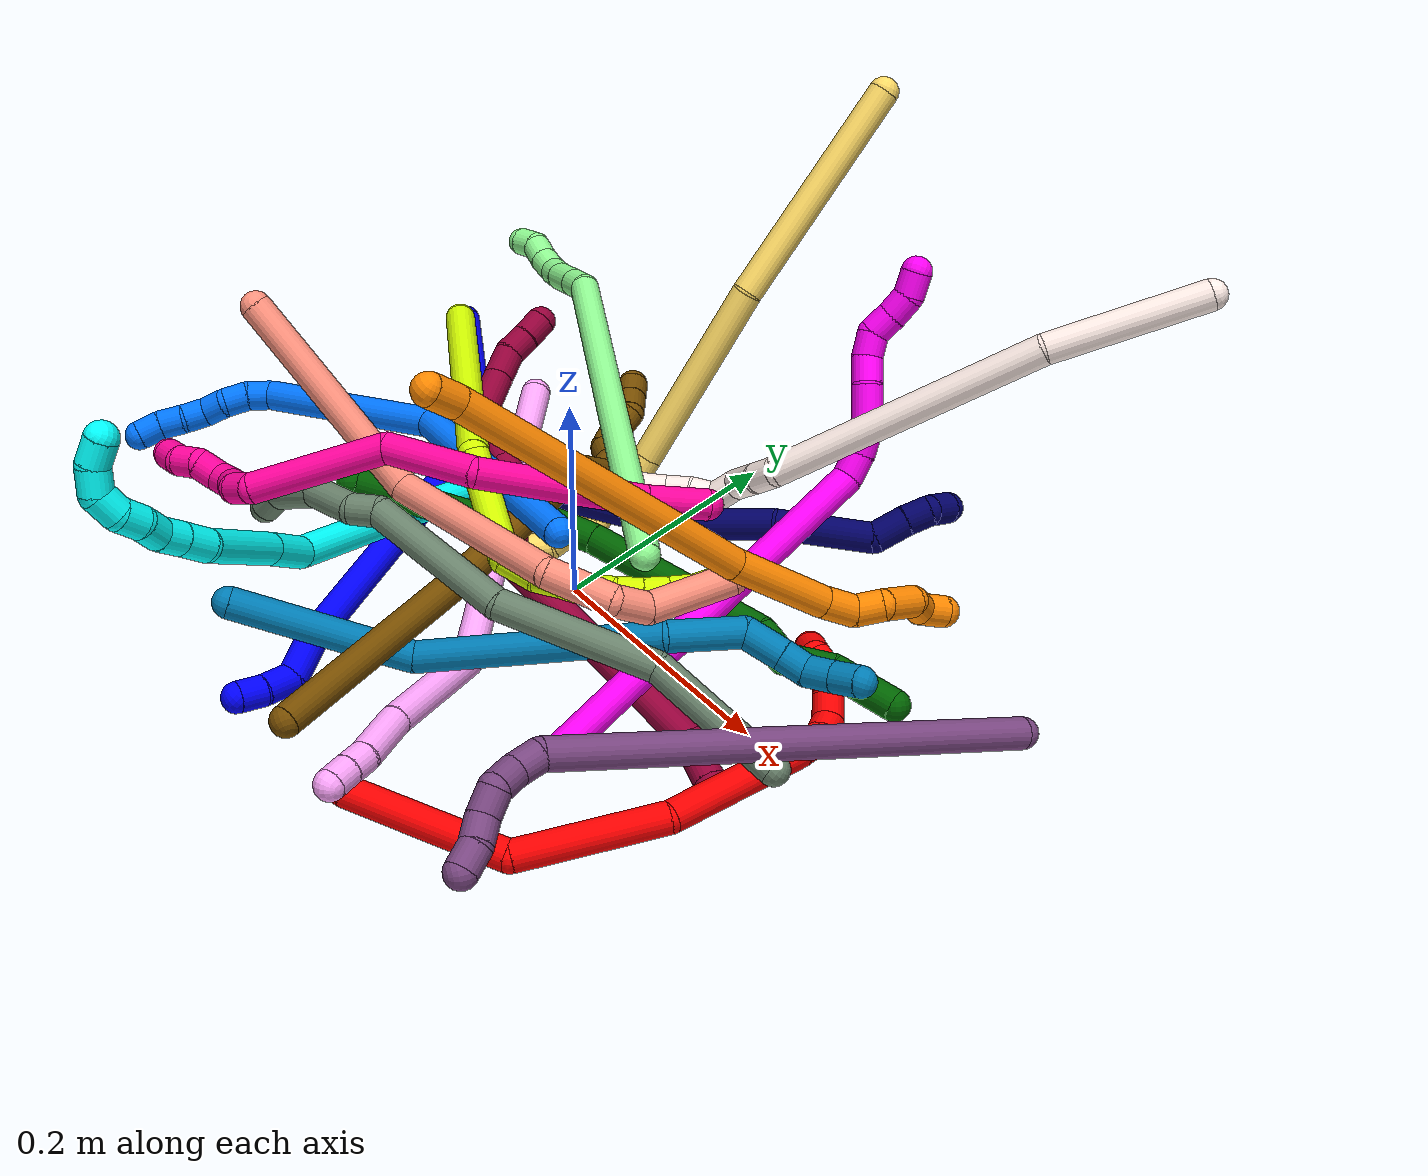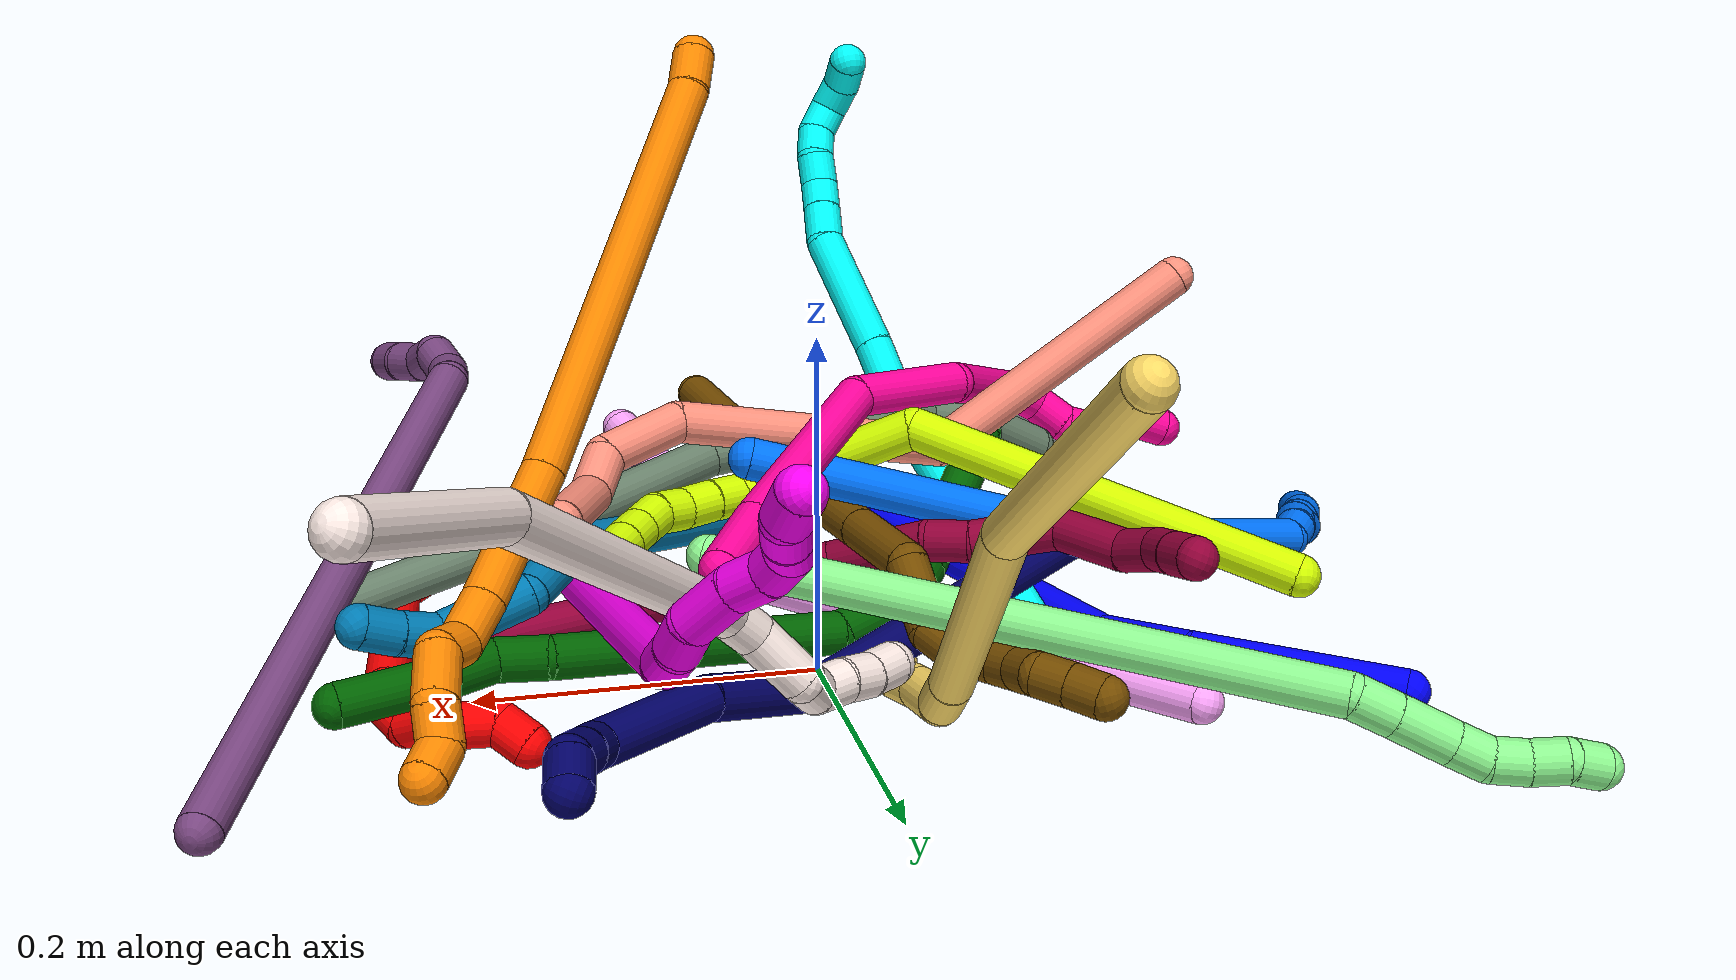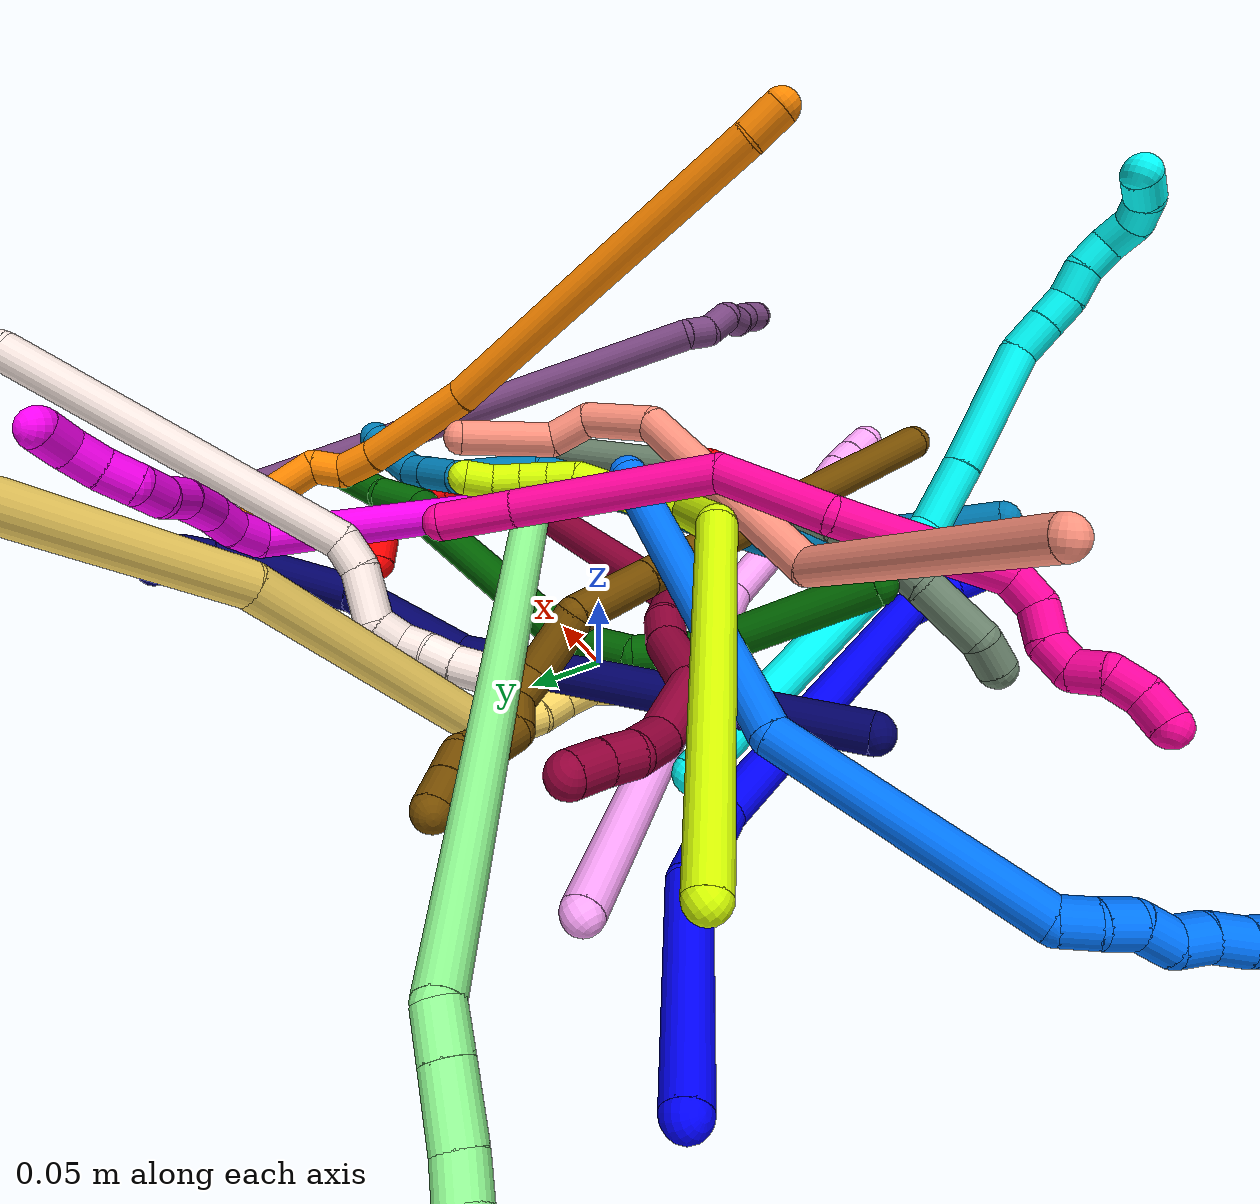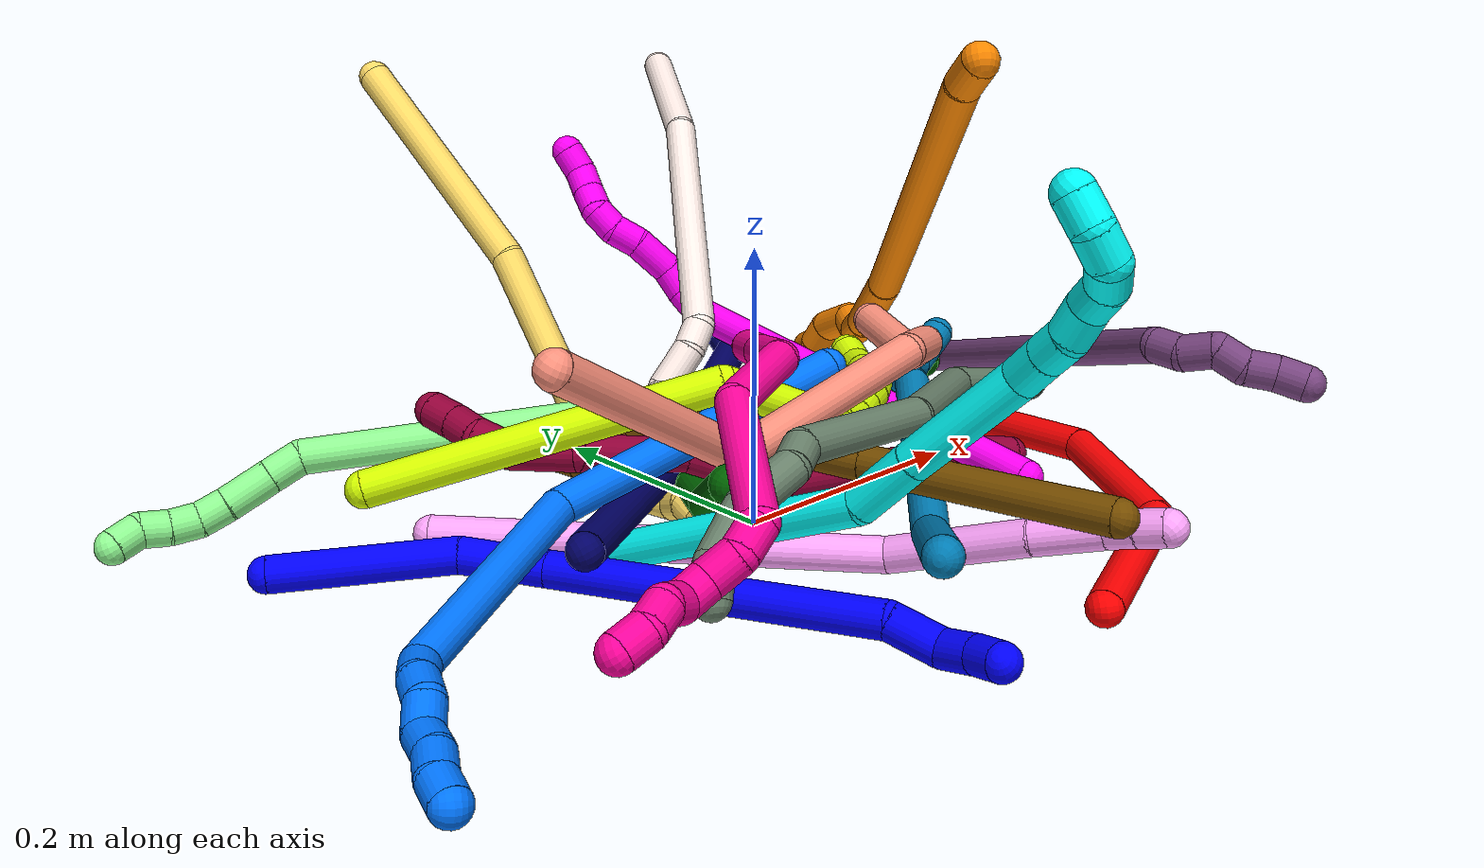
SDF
<sdf version="1.7">
 <world name="default">
  <plugin name="TubeGeneratorPlugin" filename="libtube_generator_plugin.so"/>
  <model name="photoneo_s_sensor">
   <static>1</static>
   <pose>0 0 2 1.57079 1.57079 3.14159</pose>
   <link name="link">
    <inertial><mass>0.1</mass></inertial>
    <sensor name="sensor" type="depth">
     <update_rate>30</update_rate>
     <camera>
      <horizontal_fov>1.22</horizontal_fov>
      <image><width>1920</width><height>1200</height><format>B8G8R8</format></image>
      <clip><near>0.1</near><far>4</far></clip>
      <depth_camera><output>points</output></depth_camera>
     </camera>
     <plugin name="camera_plugin" filename="libgazebo_ros_depth_camera.so">
      <baseline>0.2</baseline>
      <alwaysOn>1</alwaysOn>
      <updateRate>0.0</updateRate>
      <cameraName>camera_ir</cameraName>
      <imageTopicName>/camera/color/image_raw</imageTopicName>
      <cameraInfoTopicName>/camera/color/camera_info</cameraInfoTopicName>
      <depthImageTopicName>/camera/depth/image_raw</depthImageTopicName>
      <depthImageCameraInfoTopicName>/camera/depth/camera_info</depthImageCameraInfoTopicName>
      <pointCloudTopicName>/camera/depth/points</pointCloudTopicName>
      <frameName>fr_optical</frameName>
      <pointCloudCutoff>0.1</pointCloudCutoff>
      <pointCloudCutoffMax>2.0</pointCloudCutoffMax>
      <distortionK1>0</distortionK1>
      <distortionK2>0</distortionK2>
      <distortionK3>0</distortionK3>
      <distortionT1>0</distortionT1>
      <distortionT2>0</distortionT2>
      <CxPrime>0</CxPrime>
      <Cx>0</Cx>
      <Cy>0</Cy>
      <focalLength>0</focalLength>
      <hackBaseline>0</hackBaseline>
     </plugin>
    </sensor>
   </link>
  </model>
  <gravity>0 0 -9.8</gravity>
  <magnetic_field>6e-06 2.3e-05 -4.2e-05</magnetic_field>
  <atmosphere type="adiabatic"/>
  <physics name="default_physics" default="0" type="ode">
   <max_step_size>0.003</max_step_size>
   <real_time_factor>1</real_time_factor>
   <real_time_update_rate>1000</real_time_update_rate>
   <max_contacts>10000</max_contacts>
   <ode>
    <solver>
     <type>quick</type>
     <iters>100</iters>
     <sor>1.3</sor>
     <use_dynamic_moi_rescaling>0</use_dynamic_moi_rescaling>
    </solver>
    <constraints>
     <contact_max_correcting_vel>0</contact_max_correcting_vel>
     <contact_surface_layer>0.001</contact_surface_layer>
     <cfm>0</cfm>
     <erp>0.2</erp>
    </constraints>
   </ode>
  </physics>
  <scene><ambient>0.4 0.4 0.4 1</ambient><background>0.7 0.7 0.7 1</background><shadows>0</shadows></scene>
  <audio><device>default</device></audio>
  <spherical_coordinates>
   <surface_model>EARTH_WGS84</surface_model>
   <latitude_deg>0</latitude_deg>
   <longitude_deg>0</longitude_deg>
   <elevation>0</elevation>
   <heading_deg>0</heading_deg>
  </spherical_coordinates>
  <model name="bin">
   <static>1</static>
   <link name="bottom">
    <collision name="collision-bottom">
     <pose>0 0 -0.01 0 -0 0</pose>
     <geometry><box><size>0.8 0.6 0.02</size></box></geometry>
     <surface>
      <friction><ode><mu>100</mu><mu2>100</mu2></ode></friction>
      <contact><collide_bitmask>65535</collide_bitmask></contact>
     </surface>
    </collision>
   </link>
   <link name="west_wall">
    <collision name="collision-west_wall">
     <pose>-0.41 0 0.1 0 -0 0</pose>
     <geometry><box><size>0.02 0.6 0.2</size></box></geometry>
     <surface>
      <friction><ode><mu>100</mu><mu2>100</mu2></ode></friction>
      <contact><collide_bitmask>65535</collide_bitmask></contact>
     </surface>
    </collision>
   </link>
   <link name="east_wall">
    <collision name="collision-east_wall">
     <pose>0.41 0 0.1 0 -0 0</pose>
     <geometry><box><size>0.02 0.6 0.2</size></box></geometry>
     <surface>
      <friction><ode><mu>100</mu><mu2>100</mu2></ode></friction>
      <contact><collide_bitmask>65535</collide_bitmask></contact>
     </surface>
    </collision>
   </link>
   <link name="south_wall">
    <collision name="collision-south_wall">
     <pose>0 -0.31 0.1 0 -0 0</pose>
     <geometry><box><size>0.8 0.02 0.2</size></box></geometry>
     <surface>
      <friction><ode><mu>100</mu><mu2>100</mu2></ode></friction>
      <contact><collide_bitmask>65535</collide_bitmask></contact>
     </surface>
    </collision>
   </link>
   <link name="north_wall">
    <collision name="collision-north_wall">
     <pose>0 0.31 0.1 0 -0 0</pose>
     <geometry><box><size>0.8 0.02 0.2</size></box></geometry>
     <surface>
      <friction><ode><mu>100</mu><mu2>100</mu2></ode></friction>
      <contact><collide_bitmask>65535</collide_bitmask></contact>
     </surface>
    </collision>
   </link>
  </model>
  <model name="1">
   <static>0</static>
   <link name="1">
    <collision name="collision-cylinder-e_1_1_4">
     <pose>0.043649 -0.03724 -0.02259 2.11607 0.786469 1.27007</pose>
     <geometry><cylinder><radius>0.0125</radius><length>0.123327</length></cylinder></geometry>
     <surface>
      <friction><ode><mu>1.16</mu><mu2>1.16</mu2><slip1>0</slip1><slip2>0</slip2></ode></friction>
      <contact><ode><kp>1e+06</kp><kd>1</kd><max_vel>0</max_vel><min_depth>0.001</min_depth></ode></contact>
     </surface>
    </collision>
    <visual name="visual-cylinder-e_1_1_4">
     <pose>0.043649 -0.03724 -0.02259 2.11607 0.786469 1.27007</pose>
     <geometry><cylinder><radius>0.0125</radius><length>0.123327</length></cylinder></geometry>
     <material><ambient>0 0 1 1</ambient></material>
    </visual>
    <collision name="collision-cylinder-e_2_4_5">
     <pose>0.102055 -0.099795 -0.052172 1.84024 0.511912 0.662215</pose>
     <geometry><cylinder><radius>0.0125</radius><length>0.060252</length></cylinder></geometry>
     <surface>
      <friction><ode><mu>1.16</mu><mu2>1.16</mu2><slip1>0</slip1><slip2>0</slip2></ode></friction>
      <contact><ode><kp>1e+06</kp><kd>1</kd><max_vel>0</max_vel><min_depth>0.001</min_depth></ode></contact>
     </surface>
    </collision>
    <visual name="visual-cylinder-e_2_4_5">
     <pose>0.102055 -0.099795 -0.052172 1.84024 0.511912 0.662215</pose>
     <geometry><cylinder><radius>0.0125</radius><length>0.060252</length></cylinder></geometry>
     <material><ambient>0 0 1 1</ambient></material>
    </visual>
    <collision name="collision-cylinder-e_3_5_6">
     <pose>0.167911 -0.229491 -0.053424 1.51586 0.454658 0.43111</pose>
     <geometry><cylinder><radius>0.0125</radius><length>0.232714</length></cylinder></geometry>
     <surface>
      <friction><ode><mu>1.16</mu><mu2>1.16</mu2><slip1>0</slip1><slip2>0</slip2></ode></friction>
      <contact><ode><kp>1e+06</kp><kd>1</kd><max_vel>0</max_vel><min_depth>0.001</min_depth></ode></contact>
     </surface>
    </collision>
    <visual name="visual-cylinder-e_3_5_6">
     <pose>0.167911 -0.229491 -0.053424 1.51586 0.454658 0.43111</pose>
     <geometry><cylinder><radius>0.0125</radius><length>0.232714</length></cylinder></geometry>
     <material><ambient>0 0 1 1</ambient></material>
    </visual>
    <collision name="collision-cylinder-e_4_6_7">
     <pose>0.222172 -0.350883 -0.051691 1.80211 0.178945 0.225632</pose>
     <geometry><cylinder><radius>0.0125</radius><length>0.035525</length></cylinder></geometry>
     <surface>
      <friction><ode><mu>1.16</mu><mu2>1.16</mu2><slip1>0</slip1><slip2>0</slip2></ode></friction>
      <contact><ode><kp>1e+06</kp><kd>1</kd><max_vel>0</max_vel><min_depth>0.001</min_depth></ode></contact>
     </surface>
    </collision>
    <visual name="visual-cylinder-e_4_6_7">
     <pose>0.222172 -0.350883 -0.051691 1.80211 0.178945 0.225632</pose>
     <geometry><cylinder><radius>0.0125</radius><length>0.035525</length></cylinder></geometry>
     <material><ambient>0 0 1 1</ambient></material>
    </visual>
    <collision name="collision-cylinder-e_5_7_8">
     <pose>0.229015 -0.379238 -0.049874 1.0964 0.28113 0.172378</pose>
     <geometry><cylinder><radius>0.0125</radius><length>0.026541</length></cylinder></geometry>
     <surface>
      <friction><ode><mu>1.16</mu><mu2>1.16</mu2><slip1>0</slip1><slip2>0</slip2></ode></friction>
      <contact><ode><kp>1e+06</kp><kd>1</kd><max_vel>0</max_vel><min_depth>0.001</min_depth></ode></contact>
     </surface>
    </collision>
    <visual name="visual-cylinder-e_5_7_8">
     <pose>0.229015 -0.379238 -0.049874 1.0964 0.28113 0.172378</pose>
     <geometry><cylinder><radius>0.0125</radius><length>0.026541</length></cylinder></geometry>
     <material><ambient>0 0 1 1</ambient></material>
    </visual>
    <collision name="collision-cylinder-e_6_8_2">
     <pose>0.234254 -0.399417 -0.038004 0.97073 0.144396 0.076257</pose>
     <geometry><cylinder><radius>0.0125</radius><length>0.021642</length></cylinder></geometry>
     <surface>
      <friction><ode><mu>1.16</mu><mu2>1.16</mu2><slip1>0</slip1><slip2>0</slip2></ode></friction>
      <contact><ode><kp>1e+06</kp><kd>1</kd><max_vel>0</max_vel><min_depth>0.001</min_depth></ode></contact>
     </surface>
    </collision>
    <visual name="visual-cylinder-e_6_8_2">
     <pose>0.234254 -0.399417 -0.038004 0.97073 0.144396 0.076257</pose>
     <geometry><cylinder><radius>0.0125</radius><length>0.021642</length></cylinder></geometry>
     <material><ambient>0 0 1 1</ambient></material>
    </visual>
    <collision name="collision-sphere-2">
     <pose>0.235811 -0.408254 -0.031957 0 -0 0</pose>
     <geometry><sphere><radius>0.0125</radius></sphere></geometry>
     <surface>
      <friction><ode><mu>1.16</mu><mu2>1.16</mu2><slip1>0</slip1><slip2>0</slip2></ode></friction>
      <contact><ode><kp>1e+06</kp><kd>1</kd><max_vel>0</max_vel><min_depth>0.001</min_depth></ode></contact>
     </surface>
    </collision>
    <visual name="visual-sphere-2">
     <pose>0.235811 -0.408254 -0.031957 0 -0 0</pose>
     <geometry><sphere><radius>0.0125</radius></sphere></geometry>
     <material><ambient>0 0 1 1</ambient></material>
    </visual>
    <collision name="collision-sphere-4">
     <pose>0.087298 -0.074479 -0.045181 0 -0 0</pose>
     <geometry><sphere><radius>0.0125</radius></sphere></geometry>
     <surface>
      <friction><ode><mu>1.16</mu><mu2>1.16</mu2><slip1>0</slip1><slip2>0</slip2></ode></friction>
      <contact><ode><kp>1e+06</kp><kd>1</kd><max_vel>0</max_vel><min_depth>0.001</min_depth></ode></contact>
     </surface>
    </collision>
    <visual name="visual-sphere-4">
     <pose>0.087298 -0.074479 -0.045181 0 -0 0</pose>
     <geometry><sphere><radius>0.0125</radius></sphere></geometry>
     <material><ambient>0 0 1 1</ambient></material>
    </visual>
    <collision name="collision-sphere-1">
     <geometry><sphere><radius>0.0125</radius></sphere></geometry>
     <surface>
      <friction><ode><mu>1.16</mu><mu2>1.16</mu2><slip1>0</slip1><slip2>0</slip2></ode></friction>
      <contact><ode><kp>1e+06</kp><kd>1</kd><max_vel>0</max_vel><min_depth>0.001</min_depth></ode></contact>
     </surface>
    </collision>
    <visual name="visual-sphere-1">
     <geometry><sphere><radius>0.0125</radius></sphere></geometry>
     <material><ambient>0 0 1 1</ambient></material>
    </visual>
    <collision name="collision-sphere-8">
     <pose>0.232697 -0.390579 -0.044051 0 -0 0</pose>
     <geometry><sphere><radius>0.0125</radius></sphere></geometry>
     <surface>
      <friction><ode><mu>1.16</mu><mu2>1.16</mu2><slip1>0</slip1><slip2>0</slip2></ode></friction>
      <contact><ode><kp>1e+06</kp><kd>1</kd><max_vel>0</max_vel><min_depth>0.001</min_depth></ode></contact>
     </surface>
    </collision>
    <visual name="visual-sphere-8">
     <pose>0.232697 -0.390579 -0.044051 0 -0 0</pose>
     <geometry><sphere><radius>0.0125</radius></sphere></geometry>
     <material><ambient>0 0 1 1</ambient></material>
    </visual>
    <collision name="collision-sphere-5">
     <pose>0.116812 -0.125112 -0.059164 0 -0 0</pose>
     <geometry><sphere><radius>0.0125</radius></sphere></geometry>
     <surface>
      <friction><ode><mu>1.16</mu><mu2>1.16</mu2><slip1>0</slip1><slip2>0</slip2></ode></friction>
      <contact><ode><kp>1e+06</kp><kd>1</kd><max_vel>0</max_vel><min_depth>0.001</min_depth></ode></contact>
     </surface>
    </collision>
    <visual name="visual-sphere-5">
     <pose>0.116812 -0.125112 -0.059164 0 -0 0</pose>
     <geometry><sphere><radius>0.0125</radius></sphere></geometry>
     <material><ambient>0 0 1 1</ambient></material>
    </visual>
    <collision name="collision-sphere-6">
     <pose>0.21901 -0.33387 -0.047684 0 -0 0</pose>
     <geometry><sphere><radius>0.0125</radius></sphere></geometry>
     <surface>
      <friction><ode><mu>1.16</mu><mu2>1.16</mu2><slip1>0</slip1><slip2>0</slip2></ode></friction>
      <contact><ode><kp>1e+06</kp><kd>1</kd><max_vel>0</max_vel><min_depth>0.001</min_depth></ode></contact>
     </surface>
    </collision>
    <visual name="visual-sphere-6">
     <pose>0.21901 -0.33387 -0.047684 0 -0 0</pose>
     <geometry><sphere><radius>0.0125</radius></sphere></geometry>
     <material><ambient>0 0 1 1</ambient></material>
    </visual>
    <collision name="collision-sphere-7">
     <pose>0.225333 -0.367896 -0.055698 0 -0 0</pose>
     <geometry><sphere><radius>0.0125</radius></sphere></geometry>
     <surface>
      <friction><ode><mu>1.16</mu><mu2>1.16</mu2><slip1>0</slip1><slip2>0</slip2></ode></friction>
      <contact><ode><kp>1e+06</kp><kd>1</kd><max_vel>0</max_vel><min_depth>0.001</min_depth></ode></contact>
     </surface>
    </collision>
    <visual name="visual-sphere-7">
     <pose>0.225333 -0.367896 -0.055698 0 -0 0</pose>
     <geometry><sphere><radius>0.0125</radius></sphere></geometry>
     <material><ambient>0 0 1 1</ambient></material>
    </visual>
    <inertial>
     <pose>0.139296 -0.190371 -0.044689 0 -0 0</pose>
     <mass>0.5</mass>
     <inertia>
      <ixx>0.001459</ixx>
      <ixy>0</ixy>
      <ixz>0</ixz>
      <iyy>0.000806</iyy>
      <iyz>0</iyz>
      <izz>0.00048</izz>
     </inertia>
    </inertial>
   </link>
   <pose>-0.307117 0.134175 0.012484 0.434431 -0.736942 -0.192555</pose>
  </model>
  <model name="2">
   <static>0</static>
   <link name="2">
    <collision name="collision-cylinder-e_1_1_4">
     <pose>0.028242 0.057731 0.027329 -1.12868 0.416312 -0.265826</pose>
     <geometry><cylinder><radius>0.0125</radius><length>0.139677</length></cylinder></geometry>
     <surface>
      <friction><ode><mu>1.16</mu><mu2>1.16</mu2><slip1>0</slip1><slip2>0</slip2></ode></friction>
      <contact><ode><kp>1e+06</kp><kd>1</kd><max_vel>0</max_vel><min_depth>0.001</min_depth></ode></contact>
     </surface>
    </collision>
    <visual name="visual-cylinder-e_1_1_4">
     <pose>0.028242 0.057731 0.027329 -1.12868 0.416312 -0.265826</pose>
     <geometry><cylinder><radius>0.0125</radius><length>0.139677</length></cylinder></geometry>
     <material><ambient>1 0 0 1</ambient></material>
    </visual>
    <collision name="collision-cylinder-e_2_4_5">
     <pose>0.074362 0.168877 0.03733 -1.88448 0.308224 -0.421077</pose>
     <geometry><cylinder><radius>0.0125</radius><length>0.117863</length></cylinder></geometry>
     <surface>
      <friction><ode><mu>1.16</mu><mu2>1.16</mu2><slip1>0</slip1><slip2>0</slip2></ode></friction>
      <contact><ode><kp>1e+06</kp><kd>1</kd><max_vel>0</max_vel><min_depth>0.001</min_depth></ode></contact>
     </surface>
    </collision>
    <visual name="visual-cylinder-e_2_4_5">
     <pose>0.074362 0.168877 0.03733 -1.88448 0.308224 -0.421077</pose>
     <geometry><cylinder><radius>0.0125</radius><length>0.117863</length></cylinder></geometry>
     <material><ambient>1 0 0 1</ambient></material>
    </visual>
    <collision name="collision-cylinder-e_3_5_6">
     <pose>0.111744 0.263834 -0.017931 -2.31082 0.333737 -0.729604</pose>
     <geometry><cylinder><radius>0.0125</radius><length>0.119084</length></cylinder></geometry>
     <surface>
      <friction><ode><mu>1.16</mu><mu2>1.16</mu2><slip1>0</slip1><slip2>0</slip2></ode></friction>
      <contact><ode><kp>1e+06</kp><kd>1</kd><max_vel>0</max_vel><min_depth>0.001</min_depth></ode></contact>
     </surface>
    </collision>
    <visual name="visual-cylinder-e_3_5_6">
     <pose>0.111744 0.263834 -0.017931 -2.31082 0.333737 -0.729604</pose>
     <geometry><cylinder><radius>0.0125</radius><length>0.119084</length></cylinder></geometry>
     <material><ambient>1 0 0 1</ambient></material>
    </visual>
    <collision name="collision-cylinder-e_4_6_7">
     <pose>0.133722 0.31286 -0.063733 -2.38123 0.223981 -0.548643</pose>
     <geometry><cylinder><radius>0.0125</radius><length>0.022271</length></cylinder></geometry>
     <surface>
      <friction><ode><mu>1.16</mu><mu2>1.16</mu2><slip1>0</slip1><slip2>0</slip2></ode></friction>
      <contact><ode><kp>1e+06</kp><kd>1</kd><max_vel>0</max_vel><min_depth>0.001</min_depth></ode></contact>
     </surface>
    </collision>
    <visual name="visual-cylinder-e_4_6_7">
     <pose>0.133722 0.31286 -0.063733 -2.38123 0.223981 -0.548643</pose>
     <geometry><cylinder><radius>0.0125</radius><length>0.022271</length></cylinder></geometry>
     <material><ambient>1 0 0 1</ambient></material>
    </visual>
    <collision name="collision-cylinder-e_5_7_8">
     <pose>0.138631 0.322052 -0.081587 -2.97212 0.235929 -1.89789</pose>
     <geometry><cylinder><radius>0.0125</radius><length>0.020842</length></cylinder></geometry>
     <surface>
      <friction><ode><mu>1.16</mu><mu2>1.16</mu2><slip1>0</slip1><slip2>0</slip2></ode></friction>
      <contact><ode><kp>1e+06</kp><kd>1</kd><max_vel>0</max_vel><min_depth>0.001</min_depth></ode></contact>
     </surface>
    </collision>
    <visual name="visual-cylinder-e_5_7_8">
     <pose>0.138631 0.322052 -0.081587 -2.97212 0.235929 -1.89789</pose>
     <geometry><cylinder><radius>0.0125</radius><length>0.020842</length></cylinder></geometry>
     <material><ambient>1 0 0 1</ambient></material>
    </visual>
    <collision name="collision-cylinder-e_6_8_9">
     <pose>0.136167 0.32581 -0.100075 -2.90504 -0.51074 2.2873</pose>
     <geometry><cylinder><radius>0.0125</radius><length>0.020048</length></cylinder></geometry>
     <surface>
      <friction><ode><mu>1.16</mu><mu2>1.16</mu2><slip1>0</slip1><slip2>0</slip2></ode></friction>
      <contact><ode><kp>1e+06</kp><kd>1</kd><max_vel>0</max_vel><min_depth>0.001</min_depth></ode></contact>
     </surface>
    </collision>
    <visual name="visual-cylinder-e_6_8_9">
     <pose>0.136167 0.32581 -0.100075 -2.90504 -0.51074 2.2873</pose>
     <geometry><cylinder><radius>0.0125</radius><length>0.020048</length></cylinder></geometry>
     <material><ambient>1 0 0 1</ambient></material>
    </visual>
    <collision name="collision-cylinder-e_7_9_10">
     <pose>0.129329 0.328977 -0.118327 -3.02747 -0.194934 2.08412</pose>
     <geometry><cylinder><radius>0.0125</radius><length>0.020009</length></cylinder></geometry>
     <surface>
      <friction><ode><mu>1.16</mu><mu2>1.16</mu2><slip1>0</slip1><slip2>0</slip2></ode></friction>
      <contact><ode><kp>1e+06</kp><kd>1</kd><max_vel>0</max_vel><min_depth>0.001</min_depth></ode></contact>
     </surface>
    </collision>
    <visual name="visual-cylinder-e_7_9_10">
     <pose>0.129329 0.328977 -0.118327 -3.02747 -0.194934 2.08412</pose>
     <geometry><cylinder><radius>0.0125</radius><length>0.020009</length></cylinder></geometry>
     <material><ambient>1 0 0 1</ambient></material>
    </visual>
    <collision name="collision-cylinder-e_8_10_11">
     <pose>0.123284 0.325975 -0.136242 2.6742 -0.422147 -1.46574</pose>
     <geometry><cylinder><radius>0.0125</radius><length>0.020049</length></cylinder></geometry>
     <surface>
      <friction><ode><mu>1.16</mu><mu2>1.16</mu2><slip1>0</slip1><slip2>0</slip2></ode></friction>
      <contact><ode><kp>1e+06</kp><kd>1</kd><max_vel>0</max_vel><min_depth>0.001</min_depth></ode></contact>
     </surface>
    </collision>
    <visual name="visual-cylinder-e_8_10_11">
     <pose>0.123284 0.325975 -0.136242 2.6742 -0.422147 -1.46574</pose>
     <geometry><cylinder><radius>0.0125</radius><length>0.020049</length></cylinder></geometry>
     <material><ambient>1 0 0 1</ambient></material>
    </visual>
    <collision name="collision-cylinder-e_9_11_2">
     <pose>0.121621 0.318603 -0.153627 2.80261 0.244942 1.24705</pose>
     <geometry><cylinder><radius>0.0125</radius><length>0.020158</length></cylinder></geometry>
     <surface>
      <friction><ode><mu>1.16</mu><mu2>1.16</mu2><slip1>0</slip1><slip2>0</slip2></ode></friction>
      <contact><ode><kp>1e+06</kp><kd>1</kd><max_vel>0</max_vel><min_depth>0.001</min_depth></ode></contact>
     </surface>
    </collision>
    <visual name="visual-cylinder-e_9_11_2">
     <pose>0.121621 0.318603 -0.153627 2.80261 0.244942 1.24705</pose>
     <geometry><cylinder><radius>0.0125</radius><length>0.020158</length></cylinder></geometry>
     <material><ambient>1 0 0 1</ambient></material>
    </visual>
    <collision name="collision-sphere-2">
     <pose>0.124065 0.315351 -0.162849 0 -0 0</pose>
     <geometry><sphere><radius>0.0125</radius></sphere></geometry>
     <surface>
      <friction><ode><mu>1.16</mu><mu2>1.16</mu2><slip1>0</slip1><slip2>0</slip2></ode></friction>
      <contact><ode><kp>1e+06</kp><kd>1</kd><max_vel>0</max_vel><min_depth>0.001</min_depth></ode></contact>
     </surface>
    </collision>
    <visual name="visual-sphere-2">
     <pose>0.124065 0.315351 -0.162849 0 -0 0</pose>
     <geometry><sphere><radius>0.0125</radius></sphere></geometry>
     <material><ambient>1 0 0 1</ambient></material>
    </visual>
    <collision name="collision-sphere-11">
     <pose>0.119177 0.321855 -0.144406 0 -0 0</pose>
     <geometry><sphere><radius>0.0125</radius></sphere></geometry>
     <surface>
      <friction><ode><mu>1.16</mu><mu2>1.16</mu2><slip1>0</slip1><slip2>0</slip2></ode></friction>
      <contact><ode><kp>1e+06</kp><kd>1</kd><max_vel>0</max_vel><min_depth>0.001</min_depth></ode></contact>
     </surface>
    </collision>
    <visual name="visual-sphere-11">
     <pose>0.119177 0.321855 -0.144406 0 -0 0</pose>
     <geometry><sphere><radius>0.0125</radius></sphere></geometry>
     <material><ambient>1 0 0 1</ambient></material>
    </visual>
    <collision name="collision-sphere-10">
     <pose>0.127391 0.330095 -0.128079 0 -0 0</pose>
     <geometry><sphere><radius>0.0125</radius></sphere></geometry>
     <surface>
      <friction><ode><mu>1.16</mu><mu2>1.16</mu2><slip1>0</slip1><slip2>0</slip2></ode></friction>
      <contact><ode><kp>1e+06</kp><kd>1</kd><max_vel>0</max_vel><min_depth>0.001</min_depth></ode></contact>
     </surface>
    </collision>
    <visual name="visual-sphere-10">
     <pose>0.127391 0.330095 -0.128079 0 -0 0</pose>
     <geometry><sphere><radius>0.0125</radius></sphere></geometry>
     <material><ambient>1 0 0 1</ambient></material>
    </visual>
    <collision name="collision-sphere-9">
     <pose>0.131267 0.327859 -0.108576 0 -0 0</pose>
     <geometry><sphere><radius>0.0125</radius></sphere></geometry>
     <surface>
      <friction><ode><mu>1.16</mu><mu2>1.16</mu2><slip1>0</slip1><slip2>0</slip2></ode></friction>
      <contact><ode><kp>1e+06</kp><kd>1</kd><max_vel>0</max_vel><min_depth>0.001</min_depth></ode></contact>
     </surface>
    </collision>
    <visual name="visual-sphere-9">
     <pose>0.131267 0.327859 -0.108576 0 -0 0</pose>
     <geometry><sphere><radius>0.0125</radius></sphere></geometry>
     <material><ambient>1 0 0 1</ambient></material>
    </visual>
    <collision name="collision-sphere-4">
     <pose>0.056484 0.115463 0.054657 0 -0 0</pose>
     <geometry><sphere><radius>0.0125</radius></sphere></geometry>
     <surface>
      <friction><ode><mu>1.16</mu><mu2>1.16</mu2><slip1>0</slip1><slip2>0</slip2></ode></friction>
      <contact><ode><kp>1e+06</kp><kd>1</kd><max_vel>0</max_vel><min_depth>0.001</min_depth></ode></contact>
     </surface>
    </collision>
    <visual name="visual-sphere-4">
     <pose>0.056484 0.115463 0.054657 0 -0 0</pose>
     <geometry><sphere><radius>0.0125</radius></sphere></geometry>
     <material><ambient>1 0 0 1</ambient></material>
    </visual>
    <collision name="collision-sphere-1">
     <geometry><sphere><radius>0.0125</radius></sphere></geometry>
     <surface>
      <friction><ode><mu>1.16</mu><mu2>1.16</mu2><slip1>0</slip1><slip2>0</slip2></ode></friction>
      <contact><ode><kp>1e+06</kp><kd>1</kd><max_vel>0</max_vel><min_depth>0.001</min_depth></ode></contact>
     </surface>
    </collision>
    <visual name="visual-sphere-1">
     <geometry><sphere><radius>0.0125</radius></sphere></geometry>
     <material><ambient>1 0 0 1</ambient></material>
    </visual>
    <collision name="collision-sphere-8">
     <pose>0.141067 0.323761 -0.091574 0 -0 0</pose>
     <geometry><sphere><radius>0.0125</radius></sphere></geometry>
     <surface>
      <friction><ode><mu>1.16</mu><mu2>1.16</mu2><slip1>0</slip1><slip2>0</slip2></ode></friction>
      <contact><ode><kp>1e+06</kp><kd>1</kd><max_vel>0</max_vel><min_depth>0.001</min_depth></ode></contact>
     </surface>
    </collision>
    <visual name="visual-sphere-8">
     <pose>0.141067 0.323761 -0.091574 0 -0 0</pose>
     <geometry><sphere><radius>0.0125</radius></sphere></geometry>
     <material><ambient>1 0 0 1</ambient></material>
    </visual>
    <collision name="collision-sphere-5">
     <pose>0.09224 0.222292 0.020003 0 -0 0</pose>
     <geometry><sphere><radius>0.0125</radius></sphere></geometry>
     <surface>
      <friction><ode><mu>1.16</mu><mu2>1.16</mu2><slip1>0</slip1><slip2>0</slip2></ode></friction>
      <contact><ode><kp>1e+06</kp><kd>1</kd><max_vel>0</max_vel><min_depth>0.001</min_depth></ode></contact>
     </surface>
    </collision>
    <visual name="visual-sphere-5">
     <pose>0.09224 0.222292 0.020003 0 -0 0</pose>
     <geometry><sphere><radius>0.0125</radius></sphere></geometry>
     <material><ambient>1 0 0 1</ambient></material>
    </visual>
    <collision name="collision-sphere-6">
     <pose>0.131249 0.305377 -0.055866 0 -0 0</pose>
     <geometry><sphere><radius>0.0125</radius></sphere></geometry>
     <surface>
      <friction><ode><mu>1.16</mu><mu2>1.16</mu2><slip1>0</slip1><slip2>0</slip2></ode></friction>
      <contact><ode><kp>1e+06</kp><kd>1</kd><max_vel>0</max_vel><min_depth>0.001</min_depth></ode></contact>
     </surface>
    </collision>
    <visual name="visual-sphere-6">
     <pose>0.131249 0.305377 -0.055866 0 -0 0</pose>
     <geometry><sphere><radius>0.0125</radius></sphere></geometry>
     <material><ambient>1 0 0 1</ambient></material>
    </visual>
    <collision name="collision-sphere-7">
     <pose>0.136195 0.320343 -0.0716 0 -0 0</pose>
     <geometry><sphere><radius>0.0125</radius></sphere></geometry>
     <surface>
      <friction><ode><mu>1.16</mu><mu2>1.16</mu2><slip1>0</slip1><slip2>0</slip2></ode></friction>
      <contact><ode><kp>1e+06</kp><kd>1</kd><max_vel>0</max_vel><min_depth>0.001</min_depth></ode></contact>
     </surface>
    </collision>
    <visual name="visual-sphere-7">
     <pose>0.136195 0.320343 -0.0716 0 -0 0</pose>
     <geometry><sphere><radius>0.0125</radius></sphere></geometry>
     <material><ambient>1 0 0 1</ambient></material>
    </visual>
    <inertial>
     <pose>0.084249 0.198277 -0.014481 0 -0 0</pose>
     <mass>0.5</mass>
     <inertia>
      <ixx>0.000238</ixx>
      <ixy>0</ixy>
      <ixz>0</ixz>
      <iyy>-0.000131</iyy>
      <iyz>0</iyz>
      <izz>-0.000619</izz>
     </inertia>
    </inertial>
   </link>
   <pose>0.047116 -0.263269 0.012125 1.2337 1.09924 0.462341</pose>
  </model>
  <model name="3">
   <static>0</static>
   <link name="3">
    <collision name="collision-cylinder-e_1_1_4">
     <pose>0.014718 -0.060624 0.092018 0.582556 0.132777 0.039861</pose>
     <geometry><cylinder><radius>0.0125</radius><length>0.222343</length></cylinder></geometry>
     <surface>
      <friction><ode><mu>1.16</mu><mu2>1.16</mu2><slip1>0</slip1><slip2>0</slip2></ode></friction>
      <contact><ode><kp>1e+06</kp><kd>1</kd><max_vel>0</max_vel><min_depth>0.001</min_depth></ode></contact>
     </surface>
    </collision>
    <visual name="visual-cylinder-e_1_1_4">
     <pose>0.014718 -0.060624 0.092018 0.582556 0.132777 0.039861</pose>
     <geometry><cylinder><radius>0.0125</radius><length>0.222343</length></cylinder></geometry>
     <material><ambient>0.003922 1 0.996078 1</ambient></material>
    </visual>
    <collision name="collision-cylinder-e_2_4_5">
     <pose>0.032044 -0.125366 0.206474 0.181527 0.113849 0.010373</pose>
     <geometry><cylinder><radius>0.0125</radius><length>0.045924</length></cylinder></geometry>
     <surface>
      <friction><ode><mu>1.16</mu><mu2>1.16</mu2><slip1>0</slip1><slip2>0</slip2></ode></friction>
      <contact><ode><kp>1e+06</kp><kd>1</kd><max_vel>0</max_vel><min_depth>0.001</min_depth></ode></contact>
     </surface>
    </collision>
    <visual name="visual-cylinder-e_2_4_5">
     <pose>0.032044 -0.125366 0.206474 0.181527 0.113849 0.010373</pose>
     <geometry><cylinder><radius>0.0125</radius><length>0.045924</length></cylinder></geometry>
     <material><ambient>0.003922 1 0.996078 1</ambient></material>
    </visual>
    <collision name="collision-cylinder-e_3_5_6">
     <pose>0.041416 -0.137377 0.270074 0.189453 0.159989 0.015233</pose>
     <geometry><cylinder><radius>0.0125</radius><length>0.084908</length></cylinder></geometry>
     <surface>
      <friction><ode><mu>1.16</mu><mu2>1.16</mu2><slip1>0</slip1><slip2>0</slip2></ode></friction>
      <contact><ode><kp>1e+06</kp><kd>1</kd><max_vel>0</max_vel><min_depth>0.001</min_depth></ode></contact>
     </surface>
    </collision>
    <visual name="visual-cylinder-e_3_5_6">
     <pose>0.041416 -0.137377 0.270074 0.189453 0.159989 0.015233</pose>
     <geometry><cylinder><radius>0.0125</radius><length>0.084908</length></cylinder></geometry>
     <material><ambient>0.003922 1 0.996078 1</ambient></material>
    </visual>
    <collision name="collision-cylinder-e_4_6_7">
     <pose>0.046261 -0.148255 0.323265 0.243235 -0.1535 -0.018797</pose>
     <geometry><cylinder><radius>0.0125</radius><length>0.025082</length></cylinder></geometry>
     <surface>
      <friction><ode><mu>1.16</mu><mu2>1.16</mu2><slip1>0</slip1><slip2>0</slip2></ode></friction>
      <contact><ode><kp>1e+06</kp><kd>1</kd><max_vel>0</max_vel><min_depth>0.001</min_depth></ode></contact>
     </surface>
    </collision>
    <visual name="visual-cylinder-e_4_6_7">
     <pose>0.046261 -0.148255 0.323265 0.243235 -0.1535 -0.018797</pose>
     <geometry><cylinder><radius>0.0125</radius><length>0.025082</length></cylinder></geometry>
     <material><ambient>0.003922 1 0.996078 1</ambient></material>
    </visual>
    <collision name="collision-cylinder-e_5_7_8">
     <pose>0.042843 -0.153864 0.344989 0.264262 -0.148367 -0.019754</pose>
     <geometry><cylinder><radius>0.0125</radius><length>0.02031</length></cylinder></geometry>
     <surface>
      <friction><ode><mu>1.16</mu><mu2>1.16</mu2><slip1>0</slip1><slip2>0</slip2></ode></friction>
      <contact><ode><kp>1e+06</kp><kd>1</kd><max_vel>0</max_vel><min_depth>0.001</min_depth></ode></contact>
     </surface>
    </collision>
    <visual name="visual-cylinder-e_5_7_8">
     <pose>0.042843 -0.153864 0.344989 0.264262 -0.148367 -0.019754</pose>
     <geometry><cylinder><radius>0.0125</radius><length>0.02031</length></cylinder></geometry>
     <material><ambient>0.003922 1 0.996078 1</ambient></material>
    </visual>
    <collision name="collision-cylinder-e_6_8_9">
     <pose>0.040499 -0.156159 0.365258 -0.030997 -0.079497 0.001233</pose>
     <geometry><cylinder><radius>0.0125</radius><length>0.021225</length></cylinder></geometry>
     <surface>
      <friction><ode><mu>1.16</mu><mu2>1.16</mu2><slip1>0</slip1><slip2>0</slip2></ode></friction>
      <contact><ode><kp>1e+06</kp><kd>1</kd><max_vel>0</max_vel><min_depth>0.001</min_depth></ode></contact>
     </surface>
    </collision>
    <visual name="visual-cylinder-e_6_8_9">
     <pose>0.040499 -0.156159 0.365258 -0.030997 -0.079497 0.001233</pose>
     <geometry><cylinder><radius>0.0125</radius><length>0.021225</length></cylinder></geometry>
     <material><ambient>0.003922 1 0.996078 1</ambient></material>
    </visual>
    <collision name="collision-cylinder-e_7_9_10">
     <pose>0.037077 -0.157752 0.385343 0.199289 -0.259781 -0.026117</pose>
     <geometry><cylinder><radius>0.0125</radius><length>0.02008</length></cylinder></geometry>
     <surface>
      <friction><ode><mu>1.16</mu><mu2>1.16</mu2><slip1>0</slip1><slip2>0</slip2></ode></friction>
      <contact><ode><kp>1e+06</kp><kd>1</kd><max_vel>0</max_vel><min_depth>0.001</min_depth></ode></contact>
     </surface>
    </collision>
    <visual name="visual-cylinder-e_7_9_10">
     <pose>0.037077 -0.157752 0.385343 0.199289 -0.259781 -0.026117</pose>
     <geometry><cylinder><radius>0.0125</radius><length>0.02008</length></cylinder></geometry>
     <material><ambient>0.003922 1 0.996078 1</ambient></material>
    </visual>
    <collision name="collision-cylinder-e_8_10_11">
     <pose>0.028382 -0.159153 0.402818 -0.06525 -0.653887 0.022134</pose>
     <geometry><cylinder><radius>0.0125</radius><length>0.02011</length></cylinder></geometry>
     <surface>
      <friction><ode><mu>1.16</mu><mu2>1.16</mu2><slip1>0</slip1><slip2>0</slip2></ode></friction>
      <contact><ode><kp>1e+06</kp><kd>1</kd><max_vel>0</max_vel><min_depth>0.001</min_depth></ode></contact>
     </surface>
    </collision>
    <visual name="visual-cylinder-e_8_10_11">
     <pose>0.028382 -0.159153 0.402818 -0.06525 -0.653887 0.022134</pose>
     <geometry><cylinder><radius>0.0125</radius><length>0.02011</length></cylinder></geometry>
     <material><ambient>0.003922 1 0.996078 1</ambient></material>
    </visual>
    <collision name="collision-cylinder-e_9_11_12">
     <pose>0.017167 -0.152018 0.416292 -0.876229 -0.534691 0.25524</pose>
     <geometry><cylinder><radius>0.0125</radius><length>0.020011</length></cylinder></geometry>
     <surface>
      <friction><ode><mu>1.16</mu><mu2>1.16</mu2><slip1>0</slip1><slip2>0</slip2></ode></friction>
      <contact><ode><kp>1e+06</kp><kd>1</kd><max_vel>0</max_vel><min_depth>0.001</min_depth></ode></contact>
     </surface>
    </collision>
    <visual name="visual-cylinder-e_9_11_12">
     <pose>0.017167 -0.152018 0.416292 -0.876229 -0.534691 0.25524</pose>
     <geometry><cylinder><radius>0.0125</radius><length>0.020011</length></cylinder></geometry>
     <material><ambient>0.003922 1 0.996078 1</ambient></material>
    </visual>
    <collision name="collision-cylinder-e_10_12_2">
     <pose>0.009944 -0.136413 0.42564 -1.16736 -0.214004 0.141642</pose>
     <geometry><cylinder><radius>0.0125</radius><length>0.020006</length></cylinder></geometry>
     <surface>
      <friction><ode><mu>1.16</mu><mu2>1.16</mu2><slip1>0</slip1><slip2>0</slip2></ode></friction>
      <contact><ode><kp>1e+06</kp><kd>1</kd><max_vel>0</max_vel><min_depth>0.001</min_depth></ode></contact>
     </surface>
    </collision>
    <visual name="visual-cylinder-e_10_12_2">
     <pose>0.009944 -0.136413 0.42564 -1.16736 -0.214004 0.141642</pose>
     <geometry><cylinder><radius>0.0125</radius><length>0.020006</length></cylinder></geometry>
     <material><ambient>0.003922 1 0.996078 1</ambient></material>
    </visual>
    <collision name="collision-sphere-2">
     <pose>0.00782 -0.127423 0.429477 0 -0 0</pose>
     <geometry><sphere><radius>0.0125</radius></sphere></geometry>
     <surface>
      <friction><ode><mu>1.16</mu><mu2>1.16</mu2><slip1>0</slip1><slip2>0</slip2></ode></friction>
      <contact><ode><kp>1e+06</kp><kd>1</kd><max_vel>0</max_vel><min_depth>0.001</min_depth></ode></contact>
     </surface>
    </collision>
    <visual name="visual-sphere-2">
     <pose>0.00782 -0.127423 0.429477 0 -0 0</pose>
     <geometry><sphere><radius>0.0125</radius></sphere></geometry>
     <material><ambient>0.003922 1 0.996078 1</ambient></material>
    </visual>
    <collision name="collision-sphere-12">
     <pose>0.012068 -0.145403 0.421802 0 -0 0</pose>
     <geometry><sphere><radius>0.0125</radius></sphere></geometry>
     <surface>
      <friction><ode><mu>1.16</mu><mu2>1.16</mu2><slip1>0</slip1><slip2>0</slip2></ode></friction>
      <contact><ode><kp>1e+06</kp><kd>1</kd><max_vel>0</max_vel><min_depth>0.001</min_depth></ode></contact>
     </surface>
    </collision>
    <visual name="visual-sphere-12">
     <pose>0.012068 -0.145403 0.421802 0 -0 0</pose>
     <geometry><sphere><radius>0.0125</radius></sphere></geometry>
     <material><ambient>0.003922 1 0.996078 1</ambient></material>
    </visual>
    <collision name="collision-sphere-11">
     <pose>0.022266 -0.158632 0.410782 0 -0 0</pose>
     <geometry><sphere><radius>0.0125</radius></sphere></geometry>
     <surface>
      <friction><ode><mu>1.16</mu><mu2>1.16</mu2><slip1>0</slip1><slip2>0</slip2></ode></friction>
      <contact><ode><kp>1e+06</kp><kd>1</kd><max_vel>0</max_vel><min_depth>0.001</min_depth></ode></contact>
     </surface>
    </collision>
    <visual name="visual-sphere-11">
     <pose>0.022266 -0.158632 0.410782 0 -0 0</pose>
     <geometry><sphere><radius>0.0125</radius></sphere></geometry>
     <material><ambient>0.003922 1 0.996078 1</ambient></material>
    </visual>
    <collision name="collision-sphere-10">
     <pose>0.034498 -0.159673 0.394854 0 -0 0</pose>
     <geometry><sphere><radius>0.0125</radius></sphere></geometry>
     <surface>
      <friction><ode><mu>1.16</mu><mu2>1.16</mu2><slip1>0</slip1><slip2>0</slip2></ode></friction>
      <contact><ode><kp>1e+06</kp><kd>1</kd><max_vel>0</max_vel><min_depth>0.001</min_depth></ode></contact>
     </surface>
    </collision>
    <visual name="visual-sphere-10">
     <pose>0.034498 -0.159673 0.394854 0 -0 0</pose>
     <geometry><sphere><radius>0.0125</radius></sphere></geometry>
     <material><ambient>0.003922 1 0.996078 1</ambient></material>
    </visual>
    <collision name="collision-sphere-9">
     <pose>0.039656 -0.155831 0.375832 0 -0 0</pose>
     <geometry><sphere><radius>0.0125</radius></sphere></geometry>
     <surface>
      <friction><ode><mu>1.16</mu><mu2>1.16</mu2><slip1>0</slip1><slip2>0</slip2></ode></friction>
      <contact><ode><kp>1e+06</kp><kd>1</kd><max_vel>0</max_vel><min_depth>0.001</min_depth></ode></contact>
     </surface>
    </collision>
    <visual name="visual-sphere-9">
     <pose>0.039656 -0.155831 0.375832 0 -0 0</pose>
     <geometry><sphere><radius>0.0125</radius></sphere></geometry>
     <material><ambient>0.003922 1 0.996078 1</ambient></material>
    </visual>
    <collision name="collision-sphere-4">
     <pose>0.029435 -0.121248 0.184035 0 -0 0</pose>
     <geometry><sphere><radius>0.0125</radius></sphere></geometry>
     <surface>
      <friction><ode><mu>1.16</mu><mu2>1.16</mu2><slip1>0</slip1><slip2>0</slip2></ode></friction>
      <contact><ode><kp>1e+06</kp><kd>1</kd><max_vel>0</max_vel><min_depth>0.001</min_depth></ode></contact>
     </surface>
    </collision>
    <visual name="visual-sphere-4">
     <pose>0.029435 -0.121248 0.184035 0 -0 0</pose>
     <geometry><sphere><radius>0.0125</radius></sphere></geometry>
     <material><ambient>0.003922 1 0.996078 1</ambient></material>
    </visual>
    <collision name="collision-sphere-1">
     <geometry><sphere><radius>0.0125</radius></sphere></geometry>
     <surface>
      <friction><ode><mu>1.16</mu><mu2>1.16</mu2><slip1>0</slip1><slip2>0</slip2></ode></friction>
      <contact><ode><kp>1e+06</kp><kd>1</kd><max_vel>0</max_vel><min_depth>0.001</min_depth></ode></contact>
     </surface>
    </collision>
    <visual name="visual-sphere-1">
     <geometry><sphere><radius>0.0125</radius></sphere></geometry>
     <material><ambient>0.003922 1 0.996078 1</ambient></material>
    </visual>
    <collision name="collision-sphere-8">
     <pose>0.041342 -0.156487 0.354684 0 -0 0</pose>
     <geometry><sphere><radius>0.0125</radius></sphere></geometry>
     <surface>
      <friction><ode><mu>1.16</mu><mu2>1.16</mu2><slip1>0</slip1><slip2>0</slip2></ode></friction>
      <contact><ode><kp>1e+06</kp><kd>1</kd><max_vel>0</max_vel><min_depth>0.001</min_depth></ode></contact>
     </surface>
    </collision>
    <visual name="visual-sphere-8">
     <pose>0.041342 -0.156487 0.354684 0 -0 0</pose>
     <geometry><sphere><radius>0.0125</radius></sphere></geometry>
     <material><ambient>0.003922 1 0.996078 1</ambient></material>
    </visual>
    <collision name="collision-sphere-5">
     <pose>0.034652 -0.129485 0.228912 0 -0 0</pose>
     <geometry><sphere><radius>0.0125</radius></sphere></geometry>
     <surface>
      <friction><ode><mu>1.16</mu><mu2>1.16</mu2><slip1>0</slip1><slip2>0</slip2></ode></friction>
      <contact><ode><kp>1e+06</kp><kd>1</kd><max_vel>0</max_vel><min_depth>0.001</min_depth></ode></contact>
     </surface>
    </collision>
    <visual name="visual-sphere-5">
     <pose>0.034652 -0.129485 0.228912 0 -0 0</pose>
     <geometry><sphere><radius>0.0125</radius></sphere></geometry>
     <material><ambient>0.003922 1 0.996078 1</ambient></material>
    </visual>
    <collision name="collision-sphere-6">
     <pose>0.048179 -0.14527 0.311236 0 -0 0</pose>
     <geometry><sphere><radius>0.0125</radius></sphere></geometry>
     <surface>
      <friction><ode><mu>1.16</mu><mu2>1.16</mu2><slip1>0</slip1><slip2>0</slip2></ode></friction>
      <contact><ode><kp>1e+06</kp><kd>1</kd><max_vel>0</max_vel><min_depth>0.001</min_depth></ode></contact>
     </surface>
    </collision>
    <visual name="visual-sphere-6">
     <pose>0.048179 -0.14527 0.311236 0 -0 0</pose>
     <geometry><sphere><radius>0.0125</radius></sphere></geometry>
     <material><ambient>0.003922 1 0.996078 1</ambient></material>
    </visual>
    <collision name="collision-sphere-7">
     <pose>0.044344 -0.15124 0.335294 0 -0 0</pose>
     <geometry><sphere><radius>0.0125</radius></sphere></geometry>
     <surface>
      <friction><ode><mu>1.16</mu><mu2>1.16</mu2><slip1>0</slip1><slip2>0</slip2></ode></friction>
      <contact><ode><kp>1e+06</kp><kd>1</kd><max_vel>0</max_vel><min_depth>0.001</min_depth></ode></contact>
     </surface>
    </collision>
    <visual name="visual-sphere-7">
     <pose>0.044344 -0.15124 0.335294 0 -0 0</pose>
     <geometry><sphere><radius>0.0125</radius></sphere></geometry>
     <material><ambient>0.003922 1 0.996078 1</ambient></material>
    </visual>
    <inertial>
     <pose>0.026017 -0.106397 0.21685 0 -0 0</pose>
     <mass>0.5</mass>
     <inertia>
      <ixx>0.001028</ixx>
      <ixy>0</ixy>
      <ixz>0</ixz>
      <iyy>0.000875</iyy>
      <iyz>0</iyz>
      <izz>0.000419</izz>
     </inertia>
    </inertial>
   </link>
   <pose>-0.132877 0.013563 0.011481 0.553759 0.131329 -0.028507</pose>
  </model>
  <model name="4">
   <static>0</static>
   <link name="4">
    <collision name="collision-cylinder-e_1_1_4">
     <pose>0.084355 -0.097272 0.08599 0.846884 0.576186 0.265551</pose>
     <geometry><cylinder><radius>0.0125</radius><length>0.309657</length></cylinder></geometry>
     <surface>
      <friction><ode><mu>1.16</mu><mu2>1.16</mu2><slip1>0</slip1><slip2>0</slip2></ode></friction>
      <contact><ode><kp>1e+06</kp><kd>1</kd><max_vel>0</max_vel><min_depth>0.001</min_depth></ode></contact>
     </surface>
    </collision>
    <visual name="visual-cylinder-e_1_1_4">
     <pose>0.084355 -0.097272 0.08599 0.846884 0.576186 0.265551</pose>
     <geometry><cylinder><radius>0.0125</radius><length>0.309657</length></cylinder></geometry>
     <material><ambient>1 0.65098 0.996078 1</ambient></material>
    </visual>
    <collision name="collision-cylinder-e_2_4_5">
     <pose>0.179948 -0.241264 0.189677 1.2087 0.221252 0.153111</pose>
     <geometry><cylinder><radius>0.0125</radius><length>0.102415</length></cylinder></geometry>
     <surface>
      <friction><ode><mu>1.16</mu><mu2>1.16</mu2><slip1>0</slip1><slip2>0</slip2></ode></friction>
      <contact><ode><kp>1e+06</kp><kd>1</kd><max_vel>0</max_vel><min_depth>0.001</min_depth></ode></contact>
     </surface>
    </collision>
    <visual name="visual-cylinder-e_2_4_5">
     <pose>0.179948 -0.241264 0.189677 1.2087 0.221252 0.153111</pose>
     <geometry><cylinder><radius>0.0125</radius><length>0.102415</length></cylinder></geometry>
     <material><ambient>1 0.65098 0.996078 1</ambient></material>
    </visual>
    <collision name="collision-cylinder-e_3_5_6">
     <pose>0.19826 -0.308393 0.217631 1.10509 0.300354 0.186068</pose>
     <geometry><cylinder><radius>0.0125</radius><length>0.047824</length></cylinder></geometry>
     <surface>
      <friction><ode><mu>1.16</mu><mu2>1.16</mu2><slip1>0</slip1><slip2>0</slip2></ode></friction>
      <contact><ode><kp>1e+06</kp><kd>1</kd><max_vel>0</max_vel><min_depth>0.001</min_depth></ode></contact>
     </surface>
    </collision>
    <visual name="visual-cylinder-e_3_5_6">
     <pose>0.19826 -0.308393 0.217631 1.10509 0.300354 0.186068</pose>
     <geometry><cylinder><radius>0.0125</radius><length>0.047824</length></cylinder></geometry>
     <material><ambient>1 0.65098 0.996078 1</ambient></material>
    </visual>
    <collision name="collision-cylinder-e_4_6_7">
     <pose>0.207996 -0.338042 0.230766 1.26883 0.268368 0.198037</pose>
     <geometry><cylinder><radius>0.0125</radius><length>0.020074</length></cylinder></geometry>
     <surface>
      <friction><ode><mu>1.16</mu><mu2>1.16</mu2><slip1>0</slip1><slip2>0</slip2></ode></friction>
      <contact><ode><kp>1e+06</kp><kd>1</kd><max_vel>0</max_vel><min_depth>0.001</min_depth></ode></contact>
     </surface>
    </collision>
    <visual name="visual-cylinder-e_4_6_7">
     <pose>0.207996 -0.338042 0.230766 1.26883 0.268368 0.198037</pose>
     <geometry><cylinder><radius>0.0125</radius><length>0.020074</length></cylinder></geometry>
     <material><ambient>1 0.65098 0.996078 1</ambient></material>
    </visual>
    <collision name="collision-cylinder-e_5_7_2">
     <pose>0.213602 -0.356434 0.236448 1.27348 0.298399 0.221406</pose>
     <geometry><cylinder><radius>0.0125</radius><length>0.02003</length></cylinder></geometry>
     <surface>
      <friction><ode><mu>1.16</mu><mu2>1.16</mu2><slip1>0</slip1><slip2>0</slip2></ode></friction>
      <contact><ode><kp>1e+06</kp><kd>1</kd><max_vel>0</max_vel><min_depth>0.001</min_depth></ode></contact>
     </surface>
    </collision>
    <visual name="visual-cylinder-e_5_7_2">
     <pose>0.213602 -0.356434 0.236448 1.27348 0.298399 0.221406</pose>
     <geometry><cylinder><radius>0.0125</radius><length>0.02003</length></cylinder></geometry>
     <material><ambient>1 0.65098 0.996078 1</ambient></material>
    </visual>
    <collision name="collision-sphere-2">
     <pose>0.216546 -0.365586 0.239253 0 -0 0</pose>
     <geometry><sphere><radius>0.0125</radius></sphere></geometry>
     <surface>
      <friction><ode><mu>1.16</mu><mu2>1.16</mu2><slip1>0</slip1><slip2>0</slip2></ode></friction>
      <contact><ode><kp>1e+06</kp><kd>1</kd><max_vel>0</max_vel><min_depth>0.001</min_depth></ode></contact>
     </surface>
    </collision>
    <visual name="visual-sphere-2">
     <pose>0.216546 -0.365586 0.239253 0 -0 0</pose>
     <geometry><sphere><radius>0.0125</radius></sphere></geometry>
     <material><ambient>1 0.65098 0.996078 1</ambient></material>
    </visual>
    <collision name="collision-sphere-7">
     <pose>0.210658 -0.347282 0.233644 0 -0 0</pose>
     <geometry><sphere><radius>0.0125</radius></sphere></geometry>
     <surface>
      <friction><ode><mu>1.16</mu><mu2>1.16</mu2><slip1>0</slip1><slip2>0</slip2></ode></friction>
      <contact><ode><kp>1e+06</kp><kd>1</kd><max_vel>0</max_vel><min_depth>0.001</min_depth></ode></contact>
     </surface>
    </collision>
    <visual name="visual-sphere-7">
     <pose>0.210658 -0.347282 0.233644 0 -0 0</pose>
     <geometry><sphere><radius>0.0125</radius></sphere></geometry>
     <material><ambient>1 0.65098 0.996078 1</ambient></material>
    </visual>
    <collision name="collision-sphere-6">
     <pose>0.205335 -0.328802 0.227888 0 -0 0</pose>
     <geometry><sphere><radius>0.0125</radius></sphere></geometry>
     <surface>
      <friction><ode><mu>1.16</mu><mu2>1.16</mu2><slip1>0</slip1><slip2>0</slip2></ode></friction>
      <contact><ode><kp>1e+06</kp><kd>1</kd><max_vel>0</max_vel><min_depth>0.001</min_depth></ode></contact>
     </surface>
    </collision>
    <visual name="visual-sphere-6">
     <pose>0.205335 -0.328802 0.227888 0 -0 0</pose>
     <geometry><sphere><radius>0.0125</radius></sphere></geometry>
     <material><ambient>1 0.65098 0.996078 1</ambient></material>
    </visual>
    <collision name="collision-sphere-5">
     <pose>0.191186 -0.287984 0.207374 0 -0 0</pose>
     <geometry><sphere><radius>0.0125</radius></sphere></geometry>
     <surface>
      <friction><ode><mu>1.16</mu><mu2>1.16</mu2><slip1>0</slip1><slip2>0</slip2></ode></friction>
      <contact><ode><kp>1e+06</kp><kd>1</kd><max_vel>0</max_vel><min_depth>0.001</min_depth></ode></contact>
     </surface>
    </collision>
    <visual name="visual-sphere-5">
     <pose>0.191186 -0.287984 0.207374 0 -0 0</pose>
     <geometry><sphere><radius>0.0125</radius></sphere></geometry>
     <material><ambient>1 0.65098 0.996078 1</ambient></material>
    </visual>
    <collision name="collision-sphere-1">
     <geometry><sphere><radius>0.0125</radius></sphere></geometry>
     <surface>
      <friction><ode><mu>1.16</mu><mu2>1.16</mu2><slip1>0</slip1><slip2>0</slip2></ode></friction>
      <contact><ode><kp>1e+06</kp><kd>1</kd><max_vel>0</max_vel><min_depth>0.001</min_depth></ode></contact>
     </surface>
    </collision>
    <visual name="visual-sphere-1">
     <geometry><sphere><radius>0.0125</radius></sphere></geometry>
     <material><ambient>1 0.65098 0.996078 1</ambient></material>
    </visual>
    <collision name="collision-sphere-4">
     <pose>0.16871 -0.194544 0.17198 0 -0 0</pose>
     <geometry><sphere><radius>0.0125</radius></sphere></geometry>
     <surface>
      <friction><ode><mu>1.16</mu><mu2>1.16</mu2><slip1>0</slip1><slip2>0</slip2></ode></friction>
      <contact><ode><kp>1e+06</kp><kd>1</kd><max_vel>0</max_vel><min_depth>0.001</min_depth></ode></contact>
     </surface>
    </collision>
    <visual name="visual-sphere-4">
     <pose>0.16871 -0.194544 0.17198 0 -0 0</pose>
     <geometry><sphere><radius>0.0125</radius></sphere></geometry>
     <material><ambient>1 0.65098 0.996078 1</ambient></material>
    </visual>
    <inertial>
     <pose>0.124972 -0.167007 0.131659 0 -0 0</pose>
     <mass>0.5</mass>
     <inertia>
      <ixx>0.002696</ixx>
      <ixy>0</ixy>
      <ixz>0</ixz>
      <iyy>0.002433</iyy>
      <iyz>0</iyz>
      <izz>0.000299</izz>
     </inertia>
    </inertial>
   </link>
   <pose>-0.190474 0.118904 0.011491 -0.8667 0.994497 -0.885771</pose>
  </model>
  <model name="5">
   <static>0</static>
   <link name="5">
    <collision name="collision-cylinder-e_1_1_4">
     <pose>-0.004229 -0.018593 -0.096051 2.95038 -0.043198 -0.443142</pose>
     <geometry><cylinder><radius>0.0125</radius><length>0.19585</length></cylinder></geometry>
     <surface>
      <friction><ode><mu>1.16</mu><mu2>1.16</mu2><slip1>0</slip1><slip2>0</slip2></ode></friction>
      <contact><ode><kp>1e+06</kp><kd>1</kd><max_vel>0</max_vel><min_depth>0.001</min_depth></ode></contact>
     </surface>
    </collision>
    <visual name="visual-cylinder-e_1_1_4">
     <pose>-0.004229 -0.018593 -0.096051 2.95038 -0.043198 -0.443142</pose>
     <geometry><cylinder><radius>0.0125</radius><length>0.19585</length></cylinder></geometry>
     <material><ambient>1 0.858824 0.4 1</ambient></material>
    </visual>
    <collision name="collision-cylinder-e_2_4_5">
     <pose>-0.023841 -0.039337 -0.270599 3.1142 -0.193443 -2.8611</pose>
     <geometry><cylinder><radius>0.0125</radius><length>0.160038</length></cylinder></geometry>
     <surface>
      <friction><ode><mu>1.16</mu><mu2>1.16</mu2><slip1>0</slip1><slip2>0</slip2></ode></friction>
      <contact><ode><kp>1e+06</kp><kd>1</kd><max_vel>0</max_vel><min_depth>0.001</min_depth></ode></contact>
     </surface>
    </collision>
    <visual name="visual-cylinder-e_2_4_5">
     <pose>-0.023841 -0.039337 -0.270599 3.1142 -0.193443 -2.8611</pose>
     <geometry><cylinder><radius>0.0125</radius><length>0.160038</length></cylinder></geometry>
     <material><ambient>1 0.858824 0.4 1</ambient></material>
    </visual>
    <collision name="collision-cylinder-e_3_5_6">
     <pose>-0.041138 -0.042651 -0.363485 3.06088 -0.131821 -2.04355</pose>
     <geometry><cylinder><radius>0.0125</radius><length>0.029126</length></cylinder></geometry>
     <surface>
      <friction><ode><mu>1.16</mu><mu2>1.16</mu2><slip1>0</slip1><slip2>0</slip2></ode></friction>
      <contact><ode><kp>1e+06</kp><kd>1</kd><max_vel>0</max_vel><min_depth>0.001</min_depth></ode></contact>
     </surface>
    </collision>
    <visual name="visual-cylinder-e_3_5_6">
     <pose>-0.041138 -0.042651 -0.363485 3.06088 -0.131821 -2.04355</pose>
     <geometry><cylinder><radius>0.0125</radius><length>0.029126</length></cylinder></geometry>
     <material><ambient>1 0.858824 0.4 1</ambient></material>
    </visual>
    <collision name="collision-cylinder-e_4_6_7">
     <pose>-0.039413 -0.053308 -0.390351 2.4912 0.228067 0.65491</pose>
     <geometry><cylinder><radius>0.0125</radius><length>0.032187</length></cylinder></geometry>
     <surface>
      <friction><ode><mu>1.16</mu><mu2>1.16</mu2><slip1>0</slip1><slip2>0</slip2></ode></friction>
      <contact><ode><kp>1e+06</kp><kd>1</kd><max_vel>0</max_vel><min_depth>0.001</min_depth></ode></contact>
     </surface>
    </collision>
    <visual name="visual-cylinder-e_4_6_7">
     <pose>-0.039413 -0.053308 -0.390351 2.4912 0.228067 0.65491</pose>
     <geometry><cylinder><radius>0.0125</radius><length>0.032187</length></cylinder></geometry>
     <material><ambient>1 0.858824 0.4 1</ambient></material>
    </visual>
    <collision name="collision-cylinder-e_5_7_8">
     <pose>-0.030714 -0.068334 -0.411246 2.56007 0.465432 1.33973</pose>
     <geometry><cylinder><radius>0.0125</radius><length>0.022548</length></cylinder></geometry>
     <surface>
      <friction><ode><mu>1.16</mu><mu2>1.16</mu2><slip1>0</slip1><slip2>0</slip2></ode></friction>
      <contact><ode><kp>1e+06</kp><kd>1</kd><max_vel>0</max_vel><min_depth>0.001</min_depth></ode></contact>
     </surface>
    </collision>
    <visual name="visual-cylinder-e_5_7_8">
     <pose>-0.030714 -0.068334 -0.411246 2.56007 0.465432 1.33973</pose>
     <geometry><cylinder><radius>0.0125</radius><length>0.022548</length></cylinder></geometry>
     <material><ambient>1 0.858824 0.4 1</ambient></material>
    </visual>
    <collision name="collision-cylinder-e_6_8_9">
     <pose>-0.024362 -0.083262 -0.423206 1.93126 0.12807 0.184865</pose>
     <geometry><cylinder><radius>0.0125</radius><length>0.020243</length></cylinder></geometry>
     <surface>
      <friction><ode><mu>1.16</mu><mu2>1.16</mu2><slip1>0</slip1><slip2>0</slip2></ode></friction>
      <contact><ode><kp>1e+06</kp><kd>1</kd><max_vel>0</max_vel><min_depth>0.001</min_depth></ode></contact>
     </surface>
    </collision>
    <visual name="visual-cylinder-e_6_8_9">
     <pose>-0.024362 -0.083262 -0.423206 1.93126 0.12807 0.184865</pose>
     <geometry><cylinder><radius>0.0125</radius><length>0.020243</length></cylinder></geometry>
     <material><ambient>1 0.858824 0.4 1</ambient></material>
    </visual>
    <collision name="collision-cylinder-e_7_9_10">
     <pose>-0.023694 -0.098228 -0.435027 2.5492 -0.062524 -0.204233</pose>
     <geometry><cylinder><radius>0.0125</radius><length>0.020001</length></cylinder></geometry>
     <surface>
      <friction><ode><mu>1.16</mu><mu2>1.16</mu2><slip1>0</slip1><slip2>0</slip2></ode></friction>
      <contact><ode><kp>1e+06</kp><kd>1</kd><max_vel>0</max_vel><min_depth>0.001</min_depth></ode></contact>
     </surface>
    </collision>
    <visual name="visual-cylinder-e_7_9_10">
     <pose>-0.023694 -0.098228 -0.435027 2.5492 -0.062524 -0.204233</pose>
     <geometry><cylinder><radius>0.0125</radius><length>0.020001</length></cylinder></geometry>
     <material><ambient>1 0.858824 0.4 1</ambient></material>
    </visual>
    <collision name="collision-cylinder-e_8_10_2">
     <pose>-0.026797 -0.111596 -0.449066 2.20709 -0.250329 -0.488813</pose>
     <geometry><cylinder><radius>0.0125</radius><length>0.020006</length></cylinder></geometry>
     <surface>
      <friction><ode><mu>1.16</mu><mu2>1.16</mu2><slip1>0</slip1><slip2>0</slip2></ode></friction>
      <contact><ode><kp>1e+06</kp><kd>1</kd><max_vel>0</max_vel><min_depth>0.001</min_depth></ode></contact>
     </surface>
    </collision>
    <visual name="visual-cylinder-e_8_10_2">
     <pose>-0.026797 -0.111596 -0.449066 2.20709 -0.250329 -0.488813</pose>
     <geometry><cylinder><radius>0.0125</radius><length>0.020006</length></cylinder></geometry>
     <material><ambient>1 0.858824 0.4 1</ambient></material>
    </visual>
    <collision name="collision-sphere-2">
     <pose>-0.029275 -0.119391 -0.454824 0 -0 0</pose>
     <geometry><sphere><radius>0.0125</radius></sphere></geometry>
     <surface>
      <friction><ode><mu>1.16</mu><mu2>1.16</mu2><slip1>0</slip1><slip2>0</slip2></ode></friction>
      <contact><ode><kp>1e+06</kp><kd>1</kd><max_vel>0</max_vel><min_depth>0.001</min_depth></ode></contact>
     </surface>
    </collision>
    <visual name="visual-sphere-2">
     <pose>-0.029275 -0.119391 -0.454824 0 -0 0</pose>
     <geometry><sphere><radius>0.0125</radius></sphere></geometry>
     <material><ambient>1 0.858824 0.4 1</ambient></material>
    </visual>
    <collision name="collision-sphere-10">
     <pose>-0.024319 -0.103801 -0.443307 0 -0 0</pose>
     <geometry><sphere><radius>0.0125</radius></sphere></geometry>
     <surface>
      <friction><ode><mu>1.16</mu><mu2>1.16</mu2><slip1>0</slip1><slip2>0</slip2></ode></friction>
      <contact><ode><kp>1e+06</kp><kd>1</kd><max_vel>0</max_vel><min_depth>0.001</min_depth></ode></contact>
     </surface>
    </collision>
    <visual name="visual-sphere-10">
     <pose>-0.024319 -0.103801 -0.443307 0 -0 0</pose>
     <geometry><sphere><radius>0.0125</radius></sphere></geometry>
     <material><ambient>1 0.858824 0.4 1</ambient></material>
    </visual>
    <collision name="collision-sphere-9">
     <pose>-0.023069 -0.092656 -0.426747 0 -0 0</pose>
     <geometry><sphere><radius>0.0125</radius></sphere></geometry>
     <surface>
      <friction><ode><mu>1.16</mu><mu2>1.16</mu2><slip1>0</slip1><slip2>0</slip2></ode></friction>
      <contact><ode><kp>1e+06</kp><kd>1</kd><max_vel>0</max_vel><min_depth>0.001</min_depth></ode></contact>
     </surface>
    </collision>
    <visual name="visual-sphere-9">
     <pose>-0.023069 -0.092656 -0.426747 0 -0 0</pose>
     <geometry><sphere><radius>0.0125</radius></sphere></geometry>
     <material><ambient>1 0.858824 0.4 1</ambient></material>
    </visual>
    <collision name="collision-sphere-4">
     <pose>-0.008458 -0.037186 -0.192102 0 -0 0</pose>
     <geometry><sphere><radius>0.0125</radius></sphere></geometry>
     <surface>
      <friction><ode><mu>1.16</mu><mu2>1.16</mu2><slip1>0</slip1><slip2>0</slip2></ode></friction>
      <contact><ode><kp>1e+06</kp><kd>1</kd><max_vel>0</max_vel><min_depth>0.001</min_depth></ode></contact>
     </surface>
    </collision>
    <visual name="visual-sphere-4">
     <pose>-0.008458 -0.037186 -0.192102 0 -0 0</pose>
     <geometry><sphere><radius>0.0125</radius></sphere></geometry>
     <material><ambient>1 0.858824 0.4 1</ambient></material>
    </visual>
    <collision name="collision-sphere-1">
     <geometry><sphere><radius>0.0125</radius></sphere></geometry>
     <surface>
      <friction><ode><mu>1.16</mu><mu2>1.16</mu2><slip1>0</slip1><slip2>0</slip2></ode></friction>
      <contact><ode><kp>1e+06</kp><kd>1</kd><max_vel>0</max_vel><min_depth>0.001</min_depth></ode></contact>
     </surface>
    </collision>
    <visual name="visual-sphere-1">
     <geometry><sphere><radius>0.0125</radius></sphere></geometry>
     <material><ambient>1 0.858824 0.4 1</ambient></material>
    </visual>
    <collision name="collision-sphere-8">
     <pose>-0.025654 -0.073868 -0.419665 0 -0 0</pose>
     <geometry><sphere><radius>0.0125</radius></sphere></geometry>
     <surface>
      <friction><ode><mu>1.16</mu><mu2>1.16</mu2><slip1>0</slip1><slip2>0</slip2></ode></friction>
      <contact><ode><kp>1e+06</kp><kd>1</kd><max_vel>0</max_vel><min_depth>0.001</min_depth></ode></contact>
     </surface>
    </collision>
    <visual name="visual-sphere-8">
     <pose>-0.025654 -0.073868 -0.419665 0 -0 0</pose>
     <geometry><sphere><radius>0.0125</radius></sphere></geometry>
     <material><ambient>1 0.858824 0.4 1</ambient></material>
    </visual>
    <collision name="collision-sphere-5">
     <pose>-0.039223 -0.041487 -0.349096 0 -0 0</pose>
     <geometry><sphere><radius>0.0125</radius></sphere></geometry>
     <surface>
      <friction><ode><mu>1.16</mu><mu2>1.16</mu2><slip1>0</slip1><slip2>0</slip2></ode></friction>
      <contact><ode><kp>1e+06</kp><kd>1</kd><max_vel>0</max_vel><min_depth>0.001</min_depth></ode></contact>
     </surface>
    </collision>
    <visual name="visual-sphere-5">
     <pose>-0.039223 -0.041487 -0.349096 0 -0 0</pose>
     <geometry><sphere><radius>0.0125</radius></sphere></geometry>
     <material><ambient>1 0.858824 0.4 1</ambient></material>
    </visual>
    <collision name="collision-sphere-6">
     <pose>-0.043052 -0.043815 -0.377875 0 -0 0</pose>
     <geometry><sphere><radius>0.0125</radius></sphere></geometry>
     <surface>
      <friction><ode><mu>1.16</mu><mu2>1.16</mu2><slip1>0</slip1><slip2>0</slip2></ode></friction>
      <contact><ode><kp>1e+06</kp><kd>1</kd><max_vel>0</max_vel><min_depth>0.001</min_depth></ode></contact>
     </surface>
    </collision>
    <visual name="visual-sphere-6">
     <pose>-0.043052 -0.043815 -0.377875 0 -0 0</pose>
     <geometry><sphere><radius>0.0125</radius></sphere></geometry>
     <material><ambient>1 0.858824 0.4 1</ambient></material>
    </visual>
    <collision name="collision-sphere-7">
     <pose>-0.035774 -0.0628 -0.402828 0 -0 0</pose>
     <geometry><sphere><radius>0.0125</radius></sphere></geometry>
     <surface>
      <friction><ode><mu>1.16</mu><mu2>1.16</mu2><slip1>0</slip1><slip2>0</slip2></ode></friction>
      <contact><ode><kp>1e+06</kp><kd>1</kd><max_vel>0</max_vel><min_depth>0.001</min_depth></ode></contact>
     </surface>
    </collision>
    <visual name="visual-sphere-7">
     <pose>-0.035774 -0.0628 -0.402828 0 -0 0</pose>
     <geometry><sphere><radius>0.0125</radius></sphere></geometry>
     <material><ambient>1 0.858824 0.4 1</ambient></material>
    </visual>
    <inertial>
     <pose>-0.018612 -0.040637 -0.241588 0 -0 0</pose>
     <mass>0.5</mass>
     <inertia>
      <ixx>-0.000118</ixx>
      <ixy>0</ixy>
      <ixz>0</ixz>
      <iyy>-0.000603</iyy>
      <iyz>0</iyz>
      <izz>0.000194</izz>
     </inertia>
    </inertial>
   </link>
   <pose>-0.050195 0.379906 0.277432 -0.689347 -0.388061 -0.199956</pose>
  </model>
  <model name="6">
   <static>0</static>
   <link name="6">
    <collision name="collision-cylinder-e_1_1_4">
     <pose>0.016715 -0.011783 -0.054365 2.92815 0.2919 1.88202</pose>
     <geometry><cylinder><radius>0.0125</radius><length>0.116169</length></cylinder></geometry>
     <surface>
      <friction><ode><mu>1.16</mu><mu2>1.16</mu2><slip1>0</slip1><slip2>0</slip2></ode></friction>
      <contact><ode><kp>1e+06</kp><kd>1</kd><max_vel>0</max_vel><min_depth>0.001</min_depth></ode></contact>
     </surface>
    </collision>
    <visual name="visual-cylinder-e_1_1_4">
     <pose>0.016715 -0.011783 -0.054365 2.92815 0.2919 1.88202</pose>
     <geometry><cylinder><radius>0.0125</radius><length>0.116169</length></cylinder></geometry>
     <material><ambient>0 0.392157 0.003922 1</ambient></material>
    </visual>
    <collision name="collision-cylinder-e_2_4_5">
     <pose>0.033999 -0.021196 -0.129295 -3.02682 0.027453 -0.469088</pose>
     <geometry><cylinder><radius>0.0125</radius><length>0.041419</length></cylinder></geometry>
     <surface>
      <friction><ode><mu>1.16</mu><mu2>1.16</mu2><slip1>0</slip1><slip2>0</slip2></ode></friction>
      <contact><ode><kp>1e+06</kp><kd>1</kd><max_vel>0</max_vel><min_depth>0.001</min_depth></ode></contact>
     </surface>
    </collision>
    <visual name="visual-cylinder-e_2_4_5">
     <pose>0.033999 -0.021196 -0.129295 -3.02682 0.027453 -0.469088</pose>
     <geometry><cylinder><radius>0.0125</radius><length>0.041419</length></cylinder></geometry>
     <material><ambient>0 0.392157 0.003922 1</ambient></material>
    </visual>
    <collision name="collision-cylinder-e_3_5_6">
     <pose>0.048418 -0.011742 -0.169852 -2.80111 0.578518 -2.09397</pose>
     <geometry><cylinder><radius>0.0125</radius><length>0.050663</length></cylinder></geometry>
     <surface>
      <friction><ode><mu>1.16</mu><mu2>1.16</mu2><slip1>0</slip1><slip2>0</slip2></ode></friction>
      <contact><ode><kp>1e+06</kp><kd>1</kd><max_vel>0</max_vel><min_depth>0.001</min_depth></ode></contact>
     </surface>
    </collision>
    <visual name="visual-cylinder-e_3_5_6">
     <pose>0.048418 -0.011742 -0.169852 -2.80111 0.578518 -2.09397</pose>
     <geometry><cylinder><radius>0.0125</radius><length>0.050663</length></cylinder></geometry>
     <material><ambient>0 0.392157 0.003922 1</ambient></material>
    </visual>
    <collision name="collision-cylinder-e_4_6_7">
     <pose>0.117123 0.040787 -0.235051 -2.35355 0.707811 -1.453</pose>
     <geometry><cylinder><radius>0.0125</radius><length>0.168737</length></cylinder></geometry>
     <surface>
      <friction><ode><mu>1.16</mu><mu2>1.16</mu2><slip1>0</slip1><slip2>0</slip2></ode></friction>
      <contact><ode><kp>1e+06</kp><kd>1</kd><max_vel>0</max_vel><min_depth>0.001</min_depth></ode></contact>
     </surface>
    </collision>
    <visual name="visual-cylinder-e_4_6_7">
     <pose>0.117123 0.040787 -0.235051 -2.35355 0.707811 -1.453</pose>
     <geometry><cylinder><radius>0.0125</radius><length>0.168737</length></cylinder></geometry>
     <material><ambient>0 0.392157 0.003922 1</ambient></material>
    </visual>
    <collision name="collision-cylinder-e_5_7_8">
     <pose>0.18489 0.093465 -0.284009 -2.0492 1.00802 -1.47365</pose>
     <geometry><cylinder><radius>0.0125</radius><length>0.030535</length></cylinder></geometry>
     <surface>
      <friction><ode><mu>1.16</mu><mu2>1.16</mu2><slip1>0</slip1><slip2>0</slip2></ode></friction>
      <contact><ode><kp>1e+06</kp><kd>1</kd><max_vel>0</max_vel><min_depth>0.001</min_depth></ode></contact>
     </surface>
    </collision>
    <visual name="visual-cylinder-e_5_7_8">
     <pose>0.18489 0.093465 -0.284009 -2.0492 1.00802 -1.47365</pose>
     <geometry><cylinder><radius>0.0125</radius><length>0.030535</length></cylinder></geometry>
     <material><ambient>0 0.392157 0.003922 1</ambient></material>
    </visual>
    <collision name="collision-cylinder-e_6_8_9">
     <pose>0.205625 0.108206 -0.304021 -2.70901 0.411725 -1.51991</pose>
     <geometry><cylinder><radius>0.0125</radius><length>0.039091</length></cylinder></geometry>
     <surface>
      <friction><ode><mu>1.16</mu><mu2>1.16</mu2><slip1>0</slip1><slip2>0</slip2></ode></friction>
      <contact><ode><kp>1e+06</kp><kd>1</kd><max_vel>0</max_vel><min_depth>0.001</min_depth></ode></contact>
     </surface>
    </collision>
    <visual name="visual-cylinder-e_6_8_9">
     <pose>0.205625 0.108206 -0.304021 -2.70901 0.411725 -1.51991</pose>
     <geometry><cylinder><radius>0.0125</radius><length>0.039091</length></cylinder></geometry>
     <material><ambient>0 0.392157 0.003922 1</ambient></material>
    </visual>
    <collision name="collision-cylinder-e_7_9_2">
     <pose>0.231422 0.126569 -0.336763 -2.55917 0.738809 -1.82404</pose>
     <geometry><cylinder><radius>0.0125</radius><length>0.053386</length></cylinder></geometry>
     <surface>
      <friction><ode><mu>1.16</mu><mu2>1.16</mu2><slip1>0</slip1><slip2>0</slip2></ode></friction>
      <contact><ode><kp>1e+06</kp><kd>1</kd><max_vel>0</max_vel><min_depth>0.001</min_depth></ode></contact>
     </surface>
    </collision>
    <visual name="visual-cylinder-e_7_9_2">
     <pose>0.231422 0.126569 -0.336763 -2.55917 0.738809 -1.82404</pose>
     <geometry><cylinder><radius>0.0125</radius><length>0.053386</length></cylinder></geometry>
     <material><ambient>0 0.392157 0.003922 1</ambient></material>
    </visual>
    <collision name="collision-sphere-2">
     <pose>0.249398 0.137423 -0.353243 0 -0 0</pose>
     <geometry><sphere><radius>0.0125</radius></sphere></geometry>
     <surface>
      <friction><ode><mu>1.16</mu><mu2>1.16</mu2><slip1>0</slip1><slip2>0</slip2></ode></friction>
      <contact><ode><kp>1e+06</kp><kd>1</kd><max_vel>0</max_vel><min_depth>0.001</min_depth></ode></contact>
     </surface>
    </collision>
    <visual name="visual-sphere-2">
     <pose>0.249398 0.137423 -0.353243 0 -0 0</pose>
     <geometry><sphere><radius>0.0125</radius></sphere></geometry>
     <material><ambient>0 0.392157 0.003922 1</ambient></material>
    </visual>
    <collision name="collision-sphere-9">
     <pose>0.213447 0.115715 -0.320283 0 -0 0</pose>
     <geometry><sphere><radius>0.0125</radius></sphere></geometry>
     <surface>
      <friction><ode><mu>1.16</mu><mu2>1.16</mu2><slip1>0</slip1><slip2>0</slip2></ode></friction>
      <contact><ode><kp>1e+06</kp><kd>1</kd><max_vel>0</max_vel><min_depth>0.001</min_depth></ode></contact>
     </surface>
    </collision>
    <visual name="visual-sphere-9">
     <pose>0.213447 0.115715 -0.320283 0 -0 0</pose>
     <geometry><sphere><radius>0.0125</radius></sphere></geometry>
     <material><ambient>0 0.392157 0.003922 1</ambient></material>
    </visual>
    <collision name="collision-sphere-4">
     <pose>0.03343 -0.023567 -0.10873 0 -0 0</pose>
     <geometry><sphere><radius>0.0125</radius></sphere></geometry>
     <surface>
      <friction><ode><mu>1.16</mu><mu2>1.16</mu2><slip1>0</slip1><slip2>0</slip2></ode></friction>
      <contact><ode><kp>1e+06</kp><kd>1</kd><max_vel>0</max_vel><min_depth>0.001</min_depth></ode></contact>
     </surface>
    </collision>
    <visual name="visual-sphere-4">
     <pose>0.03343 -0.023567 -0.10873 0 -0 0</pose>
     <geometry><sphere><radius>0.0125</radius></sphere></geometry>
     <material><ambient>0 0.392157 0.003922 1</ambient></material>
    </visual>
    <collision name="collision-sphere-1">
     <geometry><sphere><radius>0.0125</radius></sphere></geometry>
     <surface>
      <friction><ode><mu>1.16</mu><mu2>1.16</mu2><slip1>0</slip1><slip2>0</slip2></ode></friction>
      <contact><ode><kp>1e+06</kp><kd>1</kd><max_vel>0</max_vel><min_depth>0.001</min_depth></ode></contact>
     </surface>
    </collision>
    <visual name="visual-sphere-1">
     <geometry><sphere><radius>0.0125</radius></sphere></geometry>
     <material><ambient>0 0.392157 0.003922 1</ambient></material>
    </visual>
    <collision name="collision-sphere-8">
     <pose>0.197803 0.100697 -0.287759 0 -0 0</pose>
     <geometry><sphere><radius>0.0125</radius></sphere></geometry>
     <surface>
      <friction><ode><mu>1.16</mu><mu2>1.16</mu2><slip1>0</slip1><slip2>0</slip2></ode></friction>
      <contact><ode><kp>1e+06</kp><kd>1</kd><max_vel>0</max_vel><min_depth>0.001</min_depth></ode></contact>
     </surface>
    </collision>
    <visual name="visual-sphere-8">
     <pose>0.197803 0.100697 -0.287759 0 -0 0</pose>
     <geometry><sphere><radius>0.0125</radius></sphere></geometry>
     <material><ambient>0 0.392157 0.003922 1</ambient></material>
    </visual>
    <collision name="collision-sphere-5">
     <pose>0.034567 -0.018825 -0.149861 0 -0 0</pose>
     <geometry><sphere><radius>0.0125</radius></sphere></geometry>
     <surface>
      <friction><ode><mu>1.16</mu><mu2>1.16</mu2><slip1>0</slip1><slip2>0</slip2></ode></friction>
      <contact><ode><kp>1e+06</kp><kd>1</kd><max_vel>0</max_vel><min_depth>0.001</min_depth></ode></contact>
     </surface>
    </collision>
    <visual name="visual-sphere-5">
     <pose>0.034567 -0.018825 -0.149861 0 -0 0</pose>
     <geometry><sphere><radius>0.0125</radius></sphere></geometry>
     <material><ambient>0 0.392157 0.003922 1</ambient></material>
    </visual>
    <collision name="collision-sphere-6">
     <pose>0.062269 -0.004659 -0.189844 0 -0 0</pose>
     <geometry><sphere><radius>0.0125</radius></sphere></geometry>
     <surface>
      <friction><ode><mu>1.16</mu><mu2>1.16</mu2><slip1>0</slip1><slip2>0</slip2></ode></friction>
      <contact><ode><kp>1e+06</kp><kd>1</kd><max_vel>0</max_vel><min_depth>0.001</min_depth></ode></contact>
     </surface>
    </collision>
    <visual name="visual-sphere-6">
     <pose>0.062269 -0.004659 -0.189844 0 -0 0</pose>
     <geometry><sphere><radius>0.0125</radius></sphere></geometry>
     <material><ambient>0 0.392157 0.003922 1</ambient></material>
    </visual>
    <collision name="collision-sphere-7">
     <pose>0.171977 0.086234 -0.280259 0 -0 0</pose>
     <geometry><sphere><radius>0.0125</radius></sphere></geometry>
     <surface>
      <friction><ode><mu>1.16</mu><mu2>1.16</mu2><slip1>0</slip1><slip2>0</slip2></ode></friction>
      <contact><ode><kp>1e+06</kp><kd>1</kd><max_vel>0</max_vel><min_depth>0.001</min_depth></ode></contact>
     </surface>
    </collision>
    <visual name="visual-sphere-7">
     <pose>0.171977 0.086234 -0.280259 0 -0 0</pose>
     <geometry><sphere><radius>0.0125</radius></sphere></geometry>
     <material><ambient>0 0.392157 0.003922 1</ambient></material>
    </visual>
    <inertial>
     <pose>0.103209 0.035763 -0.196946 0 -0 0</pose>
     <mass>0.5</mass>
     <inertia><ixx>-0.0002</ixx><ixy>0</ixy><ixz>0</ixz><iyy>1e-05</iyy><iyz>0</iyz><izz>-0.00056</izz></inertia>
    </inertial>
   </link>
   <pose>-0.132258 -0.113426 0.099685 1.37763 0.496044 -0.539307</pose>
  </model>
  <model name="7">
   <static>0</static>
   <link name="7">
    <collision name="collision-cylinder-e_1_1_4">
     <pose>0.092527 0.067086 0.066861 -0.787078 0.773713 -0.335119</pose>
     <geometry><cylinder><radius>0.0125</radius><length>0.264818</length></cylinder></geometry>
     <surface>
      <friction><ode><mu>1.16</mu><mu2>1.16</mu2><slip1>0</slip1><slip2>0</slip2></ode></friction>
      <contact><ode><kp>1e+06</kp><kd>1</kd><max_vel>0</max_vel><min_depth>0.001</min_depth></ode></contact>
     </surface>
    </collision>
    <visual name="visual-cylinder-e_1_1_4">
     <pose>0.092527 0.067086 0.066861 -0.787078 0.773713 -0.335119</pose>
     <geometry><cylinder><radius>0.0125</radius><length>0.264818</length></cylinder></geometry>
     <material><ambient>0.003922 0 0.403922 1</ambient></material>
    </visual>
    <collision name="collision-cylinder-e_2_4_5">
     <pose>0.202185 0.163376 0.161042 -0.818724 0.404728 -0.177569</pose>
     <geometry><cylinder><radius>0.0125</radius><length>0.087011</length></cylinder></geometry>
     <surface>
      <friction><ode><mu>1.16</mu><mu2>1.16</mu2><slip1>0</slip1><slip2>0</slip2></ode></friction>
      <contact><ode><kp>1e+06</kp><kd>1</kd><max_vel>0</max_vel><min_depth>0.001</min_depth></ode></contact>
     </surface>
    </collision>
    <visual name="visual-cylinder-e_2_4_5">
     <pose>0.202185 0.163376 0.161042 -0.818724 0.404728 -0.177569</pose>
     <geometry><cylinder><radius>0.0125</radius><length>0.087011</length></cylinder></geometry>
     <material><ambient>0.003922 0 0.403922 1</ambient></material>
    </visual>
    <collision name="collision-cylinder-e_3_5_6">
     <pose>0.24288 0.216051 0.209355 -0.841041 0.642424 -0.295429</pose>
     <geometry><cylinder><radius>0.0125</radius><length>0.078659</length></cylinder></geometry>
     <surface>
      <friction><ode><mu>1.16</mu><mu2>1.16</mu2><slip1>0</slip1><slip2>0</slip2></ode></friction>
      <contact><ode><kp>1e+06</kp><kd>1</kd><max_vel>0</max_vel><min_depth>0.001</min_depth></ode></contact>
     </surface>
    </collision>
    <visual name="visual-cylinder-e_3_5_6">
     <pose>0.24288 0.216051 0.209355 -0.841041 0.642424 -0.295429</pose>
     <geometry><cylinder><radius>0.0125</radius><length>0.078659</length></cylinder></geometry>
     <material><ambient>0.003922 0 0.403922 1</ambient></material>
    </visual>
    <collision name="collision-cylinder-e_4_6_7">
     <pose>0.270114 0.253216 0.231923 -1.45637 0.260129 -0.232213</pose>
     <geometry><cylinder><radius>0.0125</radius><length>0.028532</length></cylinder></geometry>
     <surface>
      <friction><ode><mu>1.16</mu><mu2>1.16</mu2><slip1>0</slip1><slip2>0</slip2></ode></friction>
      <contact><ode><kp>1e+06</kp><kd>1</kd><max_vel>0</max_vel><min_depth>0.001</min_depth></ode></contact>
     </surface>
    </collision>
    <visual name="visual-cylinder-e_4_6_7">
     <pose>0.270114 0.253216 0.231923 -1.45637 0.260129 -0.232213</pose>
     <geometry><cylinder><radius>0.0125</radius><length>0.028532</length></cylinder></geometry>
     <material><ambient>0.003922 0 0.403922 1</ambient></material>
    </visual>
    <collision name="collision-cylinder-e_5_7_8">
     <pose>0.277235 0.276564 0.235387 -1.3774 0.337575 -0.278726</pose>
     <geometry><cylinder><radius>0.0125</radius><length>0.020846</length></cylinder></geometry>
     <surface>
      <friction><ode><mu>1.16</mu><mu2>1.16</mu2><slip1>0</slip1><slip2>0</slip2></ode></friction>
      <contact><ode><kp>1e+06</kp><kd>1</kd><max_vel>0</max_vel><min_depth>0.001</min_depth></ode></contact>
     </surface>
    </collision>
    <visual name="visual-cylinder-e_5_7_8">
     <pose>0.277235 0.276564 0.235387 -1.3774 0.337575 -0.278726</pose>
     <geometry><cylinder><radius>0.0125</radius><length>0.020846</length></cylinder></geometry>
     <material><ambient>0.003922 0 0.403922 1</ambient></material>
    </visual>
    <collision name="collision-cylinder-e_6_8_2">
     <pose>0.288015 0.292422 0.23426 -2.02326 0.815373 -1.20816</pose>
     <geometry><cylinder><radius>0.0125</radius><length>0.020133</length></cylinder></geometry>
     <surface>
      <friction><ode><mu>1.16</mu><mu2>1.16</mu2><slip1>0</slip1><slip2>0</slip2></ode></friction>
      <contact><ode><kp>1e+06</kp><kd>1</kd><max_vel>0</max_vel><min_depth>0.001</min_depth></ode></contact>
     </surface>
    </collision>
    <visual name="visual-cylinder-e_6_8_2">
     <pose>0.288015 0.292422 0.23426 -2.02326 0.815373 -1.20816</pose>
     <geometry><cylinder><radius>0.0125</radius><length>0.020133</length></cylinder></geometry>
     <material><ambient>0.003922 0 0.403922 1</ambient></material>
    </visual>
    <collision name="collision-sphere-2">
     <pose>0.295344 0.298629 0.231243 0 -0 0</pose>
     <geometry><sphere><radius>0.0125</radius></sphere></geometry>
     <surface>
      <friction><ode><mu>1.16</mu><mu2>1.16</mu2><slip1>0</slip1><slip2>0</slip2></ode></friction>
      <contact><ode><kp>1e+06</kp><kd>1</kd><max_vel>0</max_vel><min_depth>0.001</min_depth></ode></contact>
     </surface>
    </collision>
    <visual name="visual-sphere-2">
     <pose>0.295344 0.298629 0.231243 0 -0 0</pose>
     <geometry><sphere><radius>0.0125</radius></sphere></geometry>
     <material><ambient>0.003922 0 0.403922 1</ambient></material>
    </visual>
    <collision name="collision-sphere-4">
     <pose>0.185054 0.134172 0.133722 0 -0 0</pose>
     <geometry><sphere><radius>0.0125</radius></sphere></geometry>
     <surface>
      <friction><ode><mu>1.16</mu><mu2>1.16</mu2><slip1>0</slip1><slip2>0</slip2></ode></friction>
      <contact><ode><kp>1e+06</kp><kd>1</kd><max_vel>0</max_vel><min_depth>0.001</min_depth></ode></contact>
     </surface>
    </collision>
    <visual name="visual-sphere-4">
     <pose>0.185054 0.134172 0.133722 0 -0 0</pose>
     <geometry><sphere><radius>0.0125</radius></sphere></geometry>
     <material><ambient>0.003922 0 0.403922 1</ambient></material>
    </visual>
    <collision name="collision-sphere-1">
     <geometry><sphere><radius>0.0125</radius></sphere></geometry>
     <surface>
      <friction><ode><mu>1.16</mu><mu2>1.16</mu2><slip1>0</slip1><slip2>0</slip2></ode></friction>
      <contact><ode><kp>1e+06</kp><kd>1</kd><max_vel>0</max_vel><min_depth>0.001</min_depth></ode></contact>
     </surface>
    </collision>
    <visual name="visual-sphere-1">
     <geometry><sphere><radius>0.0125</radius></sphere></geometry>
     <material><ambient>0.003922 0 0.403922 1</ambient></material>
    </visual>
    <collision name="collision-sphere-8">
     <pose>0.280687 0.286215 0.237277 0 -0 0</pose>
     <geometry><sphere><radius>0.0125</radius></sphere></geometry>
     <surface>
      <friction><ode><mu>1.16</mu><mu2>1.16</mu2><slip1>0</slip1><slip2>0</slip2></ode></friction>
      <contact><ode><kp>1e+06</kp><kd>1</kd><max_vel>0</max_vel><min_depth>0.001</min_depth></ode></contact>
     </surface>
    </collision>
    <visual name="visual-sphere-8">
     <pose>0.280687 0.286215 0.237277 0 -0 0</pose>
     <geometry><sphere><radius>0.0125</radius></sphere></geometry>
     <material><ambient>0.003922 0 0.403922 1</ambient></material>
    </visual>
    <collision name="collision-sphere-5">
     <pose>0.219317 0.192581 0.188362 0 -0 0</pose>
     <geometry><sphere><radius>0.0125</radius></sphere></geometry>
     <surface>
      <friction><ode><mu>1.16</mu><mu2>1.16</mu2><slip1>0</slip1><slip2>0</slip2></ode></friction>
      <contact><ode><kp>1e+06</kp><kd>1</kd><max_vel>0</max_vel><min_depth>0.001</min_depth></ode></contact>
     </surface>
    </collision>
    <visual name="visual-sphere-5">
     <pose>0.219317 0.192581 0.188362 0 -0 0</pose>
     <geometry><sphere><radius>0.0125</radius></sphere></geometry>
     <material><ambient>0.003922 0 0.403922 1</ambient></material>
    </visual>
    <collision name="collision-sphere-6">
     <pose>0.266444 0.239521 0.230349 0 -0 0</pose>
     <geometry><sphere><radius>0.0125</radius></sphere></geometry>
     <surface>
      <friction><ode><mu>1.16</mu><mu2>1.16</mu2><slip1>0</slip1><slip2>0</slip2></ode></friction>
      <contact><ode><kp>1e+06</kp><kd>1</kd><max_vel>0</max_vel><min_depth>0.001</min_depth></ode></contact>
     </surface>
    </collision>
    <visual name="visual-sphere-6">
     <pose>0.266444 0.239521 0.230349 0 -0 0</pose>
     <geometry><sphere><radius>0.0125</radius></sphere></geometry>
     <material><ambient>0.003922 0 0.403922 1</ambient></material>
    </visual>
    <collision name="collision-sphere-7">
     <pose>0.273783 0.266912 0.233497 0 -0 0</pose>
     <geometry><sphere><radius>0.0125</radius></sphere></geometry>
     <surface>
      <friction><ode><mu>1.16</mu><mu2>1.16</mu2><slip1>0</slip1><slip2>0</slip2></ode></friction>
      <contact><ode><kp>1e+06</kp><kd>1</kd><max_vel>0</max_vel><min_depth>0.001</min_depth></ode></contact>
     </surface>
    </collision>
    <visual name="visual-sphere-7">
     <pose>0.273783 0.266912 0.233497 0 -0 0</pose>
     <geometry><sphere><radius>0.0125</radius></sphere></geometry>
     <material><ambient>0.003922 0 0.403922 1</ambient></material>
    </visual>
    <inertial>
     <pose>0.16097 0.135706 0.128853 0 -0 0</pose>
     <mass>0.5</mass>
     <inertia>
      <ixx>0.000778</ixx>
      <ixy>0</ixy>
      <ixz>0</ixz>
      <iyy>0.001005</iyy>
      <iyz>0</iyz>
      <izz>-0.001982</izz>
     </inertia>
    </inertial>
   </link>
   <pose>-0.198551 -0.058563 0.05893 0.96217 0.906361 0.723344</pose>
  </model>
  <model name="8">
   <static>0</static>
   <link name="8">
    <collision name="collision-cylinder-e_1_1_4">
     <pose>-0.015301 0.002661 0.009946 -0.261415 -0.978482 0.139751</pose>
     <geometry><cylinder><radius>0.0125</radius><length>0.036885</length></cylinder></geometry>
     <surface>
      <friction><ode><mu>1.16</mu><mu2>1.16</mu2><slip1>0</slip1><slip2>0</slip2></ode></friction>
      <contact><ode><kp>1e+06</kp><kd>1</kd><max_vel>0</max_vel><min_depth>0.001</min_depth></ode></contact>
     </surface>
    </collision>
    <visual name="visual-cylinder-e_1_1_4">
     <pose>-0.015301 0.002661 0.009946 -0.261415 -0.978482 0.139751</pose>
     <geometry><cylinder><radius>0.0125</radius><length>0.036885</length></cylinder></geometry>
     <material><ambient>0.584314 0 0.227451 1</ambient></material>
    </visual>
    <collision name="collision-cylinder-e_2_4_5">
     <pose>-0.114293 -0.010604 0.076923 0.272317 -0.955049 -0.141556</pose>
     <geometry><cylinder><radius>0.0125</radius><length>0.205041</length></cylinder></geometry>
     <surface>
      <friction><ode><mu>1.16</mu><mu2>1.16</mu2><slip1>0</slip1><slip2>0</slip2></ode></friction>
      <contact><ode><kp>1e+06</kp><kd>1</kd><max_vel>0</max_vel><min_depth>0.001</min_depth></ode></contact>
     </surface>
    </collision>
    <visual name="visual-cylinder-e_2_4_5">
     <pose>-0.114293 -0.010604 0.076923 0.272317 -0.955049 -0.141556</pose>
     <geometry><cylinder><radius>0.0125</radius><length>0.205041</length></cylinder></geometry>
     <material><ambient>0.584314 0 0.227451 1</ambient></material>
    </visual>
    <collision name="collision-cylinder-e_3_5_6">
     <pose>-0.220315 -0.009523 0.152517 -0.741655 -0.725569 0.293062</pose>
     <geometry><cylinder><radius>0.0125</radius><length>0.067305</length></cylinder></geometry>
     <surface>
      <friction><ode><mu>1.16</mu><mu2>1.16</mu2><slip1>0</slip1><slip2>0</slip2></ode></friction>
      <contact><ode><kp>1e+06</kp><kd>1</kd><max_vel>0</max_vel><min_depth>0.001</min_depth></ode></contact>
     </surface>
    </collision>
    <visual name="visual-cylinder-e_3_5_6">
     <pose>-0.220315 -0.009523 0.152517 -0.741655 -0.725569 0.293062</pose>
     <geometry><cylinder><radius>0.0125</radius><length>0.067305</length></cylinder></geometry>
     <material><ambient>0.584314 0 0.227451 1</ambient></material>
    </visual>
    <collision name="collision-cylinder-e_4_6_7">
     <pose>-0.25367 0.011562 0.175912 -0.701112 -1.05005 0.417448</pose>
     <geometry><cylinder><radius>0.0125</radius><length>0.025418</length></cylinder></geometry>
     <surface>
      <friction><ode><mu>1.16</mu><mu2>1.16</mu2><slip1>0</slip1><slip2>0</slip2></ode></friction>
      <contact><ode><kp>1e+06</kp><kd>1</kd><max_vel>0</max_vel><min_depth>0.001</min_depth></ode></contact>
     </surface>
    </collision>
    <visual name="visual-cylinder-e_4_6_7">
     <pose>-0.25367 0.011562 0.175912 -0.701112 -1.05005 0.417448</pose>
     <geometry><cylinder><radius>0.0125</radius><length>0.025418</length></cylinder></geometry>
     <material><ambient>0.584314 0 0.227451 1</ambient></material>
    </visual>
    <collision name="collision-cylinder-e_5_7_8">
     <pose>-0.286368 0.019423 0.194446 -0.269356 -0.990325 0.146088</pose>
     <geometry><cylinder><radius>0.0125</radius><length>0.051837</length></cylinder></geometry>
     <surface>
      <friction><ode><mu>1.16</mu><mu2>1.16</mu2><slip1>0</slip1><slip2>0</slip2></ode></friction>
      <contact><ode><kp>1e+06</kp><kd>1</kd><max_vel>0</max_vel><min_depth>0.001</min_depth></ode></contact>
     </surface>
    </collision>
    <visual name="visual-cylinder-e_5_7_8">
     <pose>-0.286368 0.019423 0.194446 -0.269356 -0.990325 0.146088</pose>
     <geometry><cylinder><radius>0.0125</radius><length>0.051837</length></cylinder></geometry>
     <material><ambient>0.584314 0 0.227451 1</ambient></material>
    </visual>
    <collision name="collision-cylinder-e_6_8_9">
     <pose>-0.325107 0.03856 0.210524 -1.41723 -0.832287 0.72421</pose>
     <geometry><cylinder><radius>0.0125</radius><length>0.046159</length></cylinder></geometry>
     <surface>
      <friction><ode><mu>1.16</mu><mu2>1.16</mu2><slip1>0</slip1><slip2>0</slip2></ode></friction>
      <contact><ode><kp>1e+06</kp><kd>1</kd><max_vel>0</max_vel><min_depth>0.001</min_depth></ode></contact>
     </surface>
    </collision>
    <visual name="visual-cylinder-e_6_8_9">
     <pose>-0.325107 0.03856 0.210524 -1.41723 -0.832287 0.72421</pose>
     <geometry><cylinder><radius>0.0125</radius><length>0.046159</length></cylinder></geometry>
     <material><ambient>0.584314 0 0.227451 1</ambient></material>
    </visual>
    <collision name="collision-cylinder-e_7_9_10">
     <pose>-0.348562 0.064407 0.217479 -1.15943 -0.508934 0.337377</pose>
     <geometry><cylinder><radius>0.0125</radius><length>0.02622</length></cylinder></geometry>
     <surface>
      <friction><ode><mu>1.16</mu><mu2>1.16</mu2><slip1>0</slip1><slip2>0</slip2></ode></friction>
      <contact><ode><kp>1e+06</kp><kd>1</kd><max_vel>0</max_vel><min_depth>0.001</min_depth></ode></contact>
     </surface>
    </collision>
    <visual name="visual-cylinder-e_7_9_10">
     <pose>-0.348562 0.064407 0.217479 -1.15943 -0.508934 0.337377</pose>
     <geometry><cylinder><radius>0.0125</radius><length>0.02622</length></cylinder></geometry>
     <material><ambient>0.584314 0 0.227451 1</ambient></material>
    </visual>
    <collision name="collision-cylinder-e_8_10_11">
     <pose>-0.357583 0.084589 0.223333 -1.43978 -0.263265 0.231159</pose>
     <geometry><cylinder><radius>0.0125</radius><length>0.020242</length></cylinder></geometry>
     <surface>
      <friction><ode><mu>1.16</mu><mu2>1.16</mu2><slip1>0</slip1><slip2>0</slip2></ode></friction>
      <contact><ode><kp>1e+06</kp><kd>1</kd><max_vel>0</max_vel><min_depth>0.001</min_depth></ode></contact>
     </surface>
    </collision>
    <visual name="visual-cylinder-e_8_10_11">
     <pose>-0.357583 0.084589 0.223333 -1.43978 -0.263265 0.231159</pose>
     <geometry><cylinder><radius>0.0125</radius><length>0.020242</length></cylinder></geometry>
     <material><ambient>0.584314 0 0.227451 1</ambient></material>
    </visual>
    <collision name="collision-cylinder-e_9_11_2">
     <pose>-0.363707 0.104016 0.226064 -1.42252 -0.340587 0.294221</pose>
     <geometry><cylinder><radius>0.0125</radius><length>0.020894</length></cylinder></geometry>
     <surface>
      <friction><ode><mu>1.16</mu><mu2>1.16</mu2><slip1>0</slip1><slip2>0</slip2></ode></friction>
      <contact><ode><kp>1e+06</kp><kd>1</kd><max_vel>0</max_vel><min_depth>0.001</min_depth></ode></contact>
     </surface>
    </collision>
    <visual name="visual-cylinder-e_9_11_2">
     <pose>-0.363707 0.104016 0.226064 -1.42252 -0.340587 0.294221</pose>
     <geometry><cylinder><radius>0.0125</radius><length>0.020894</length></cylinder></geometry>
     <material><ambient>0.584314 0 0.227451 1</ambient></material>
    </visual>
    <collision name="collision-sphere-2">
     <pose>-0.367197 0.113755 0.227519 0 -0 0</pose>
     <geometry><sphere><radius>0.0125</radius></sphere></geometry>
     <surface>
      <friction><ode><mu>1.16</mu><mu2>1.16</mu2><slip1>0</slip1><slip2>0</slip2></ode></friction>
      <contact><ode><kp>1e+06</kp><kd>1</kd><max_vel>0</max_vel><min_depth>0.001</min_depth></ode></contact>
     </surface>
    </collision>
    <visual name="visual-sphere-2">
     <pose>-0.367197 0.113755 0.227519 0 -0 0</pose>
     <geometry><sphere><radius>0.0125</radius></sphere></geometry>
     <material><ambient>0.584314 0 0.227451 1</ambient></material>
    </visual>
    <collision name="collision-sphere-11">
     <pose>-0.360217 0.094277 0.22461 0 -0 0</pose>
     <geometry><sphere><radius>0.0125</radius></sphere></geometry>
     <surface>
      <friction><ode><mu>1.16</mu><mu2>1.16</mu2><slip1>0</slip1><slip2>0</slip2></ode></friction>
      <contact><ode><kp>1e+06</kp><kd>1</kd><max_vel>0</max_vel><min_depth>0.001</min_depth></ode></contact>
     </surface>
    </collision>
    <visual name="visual-sphere-11">
     <pose>-0.360217 0.094277 0.22461 0 -0 0</pose>
     <geometry><sphere><radius>0.0125</radius></sphere></geometry>
     <material><ambient>0.584314 0 0.227451 1</ambient></material>
    </visual>
    <collision name="collision-sphere-10">
     <pose>-0.35495 0.074901 0.222056 0 -0 0</pose>
     <geometry><sphere><radius>0.0125</radius></sphere></geometry>
     <surface>
      <friction><ode><mu>1.16</mu><mu2>1.16</mu2><slip1>0</slip1><slip2>0</slip2></ode></friction>
      <contact><ode><kp>1e+06</kp><kd>1</kd><max_vel>0</max_vel><min_depth>0.001</min_depth></ode></contact>
     </surface>
    </collision>
    <visual name="visual-sphere-10">
     <pose>-0.35495 0.074901 0.222056 0 -0 0</pose>
     <geometry><sphere><radius>0.0125</radius></sphere></geometry>
     <material><ambient>0.584314 0 0.227451 1</ambient></material>
    </visual>
    <collision name="collision-sphere-9">
     <pose>-0.342174 0.053914 0.212901 0 -0 0</pose>
     <geometry><sphere><radius>0.0125</radius></sphere></geometry>
     <surface>
      <friction><ode><mu>1.16</mu><mu2>1.16</mu2><slip1>0</slip1><slip2>0</slip2></ode></friction>
      <contact><ode><kp>1e+06</kp><kd>1</kd><max_vel>0</max_vel><min_depth>0.001</min_depth></ode></contact>
     </surface>
    </collision>
    <visual name="visual-sphere-9">
     <pose>-0.342174 0.053914 0.212901 0 -0 0</pose>
     <geometry><sphere><radius>0.0125</radius></sphere></geometry>
     <material><ambient>0.584314 0 0.227451 1</ambient></material>
    </visual>
    <collision name="collision-sphere-4">
     <pose>-0.030601 0.005322 0.019892 0 -0 0</pose>
     <geometry><sphere><radius>0.0125</radius></sphere></geometry>
     <surface>
      <friction><ode><mu>1.16</mu><mu2>1.16</mu2><slip1>0</slip1><slip2>0</slip2></ode></friction>
      <contact><ode><kp>1e+06</kp><kd>1</kd><max_vel>0</max_vel><min_depth>0.001</min_depth></ode></contact>
     </surface>
    </collision>
    <visual name="visual-sphere-4">
     <pose>-0.030601 0.005322 0.019892 0 -0 0</pose>
     <geometry><sphere><radius>0.0125</radius></sphere></geometry>
     <material><ambient>0.584314 0 0.227451 1</ambient></material>
    </visual>
    <collision name="collision-sphere-1">
     <geometry><sphere><radius>0.0125</radius></sphere></geometry>
     <surface>
      <friction><ode><mu>1.16</mu><mu2>1.16</mu2><slip1>0</slip1><slip2>0</slip2></ode></friction>
      <contact><ode><kp>1e+06</kp><kd>1</kd><max_vel>0</max_vel><min_depth>0.001</min_depth></ode></contact>
     </surface>
    </collision>
    <visual name="visual-sphere-1">
     <geometry><sphere><radius>0.0125</radius></sphere></geometry>
     <material><ambient>0.584314 0 0.227451 1</ambient></material>
    </visual>
    <collision name="collision-sphere-8">
     <pose>-0.308041 0.023206 0.208147 0 -0 0</pose>
     <geometry><sphere><radius>0.0125</radius></sphere></geometry>
     <surface>
      <friction><ode><mu>1.16</mu><mu2>1.16</mu2><slip1>0</slip1><slip2>0</slip2></ode></friction>
      <contact><ode><kp>1e+06</kp><kd>1</kd><max_vel>0</max_vel><min_depth>0.001</min_depth></ode></contact>
     </surface>
    </collision>
    <visual name="visual-sphere-8">
     <pose>-0.308041 0.023206 0.208147 0 -0 0</pose>
     <geometry><sphere><radius>0.0125</radius></sphere></geometry>
     <material><ambient>0.584314 0 0.227451 1</ambient></material>
    </visual>
    <collision name="collision-sphere-5">
     <pose>-0.197985 -0.02653 0.133954 0 -0 0</pose>
     <geometry><sphere><radius>0.0125</radius></sphere></geometry>
     <surface>
      <friction><ode><mu>1.16</mu><mu2>1.16</mu2><slip1>0</slip1><slip2>0</slip2></ode></friction>
      <contact><ode><kp>1e+06</kp><kd>1</kd><max_vel>0</max_vel><min_depth>0.001</min_depth></ode></contact>
     </surface>
    </collision>
    <visual name="visual-sphere-5">
     <pose>-0.197985 -0.02653 0.133954 0 -0 0</pose>
     <geometry><sphere><radius>0.0125</radius></sphere></geometry>
     <material><ambient>0.584314 0 0.227451 1</ambient></material>
    </visual>
    <collision name="collision-sphere-6">
     <pose>-0.242646 0.007483 0.171081 0 -0 0</pose>
     <geometry><sphere><radius>0.0125</radius></sphere></geometry>
     <surface>
      <friction><ode><mu>1.16</mu><mu2>1.16</mu2><slip1>0</slip1><slip2>0</slip2></ode></friction>
      <contact><ode><kp>1e+06</kp><kd>1</kd><max_vel>0</max_vel><min_depth>0.001</min_depth></ode></contact>
     </surface>
    </collision>
    <visual name="visual-sphere-6">
     <pose>-0.242646 0.007483 0.171081 0 -0 0</pose>
     <geometry><sphere><radius>0.0125</radius></sphere></geometry>
     <material><ambient>0.584314 0 0.227451 1</ambient></material>
    </visual>
    <collision name="collision-sphere-7">
     <pose>-0.264694 0.015641 0.180744 0 -0 0</pose>
     <geometry><sphere><radius>0.0125</radius></sphere></geometry>
     <surface>
      <friction><ode><mu>1.16</mu><mu2>1.16</mu2><slip1>0</slip1><slip2>0</slip2></ode></friction>
      <contact><ode><kp>1e+06</kp><kd>1</kd><max_vel>0</max_vel><min_depth>0.001</min_depth></ode></contact>
     </surface>
    </collision>
    <visual name="visual-sphere-7">
     <pose>-0.264694 0.015641 0.180744 0 -0 0</pose>
     <geometry><sphere><radius>0.0125</radius></sphere></geometry>
     <material><ambient>0.584314 0 0.227451 1</ambient></material>
    </visual>
    <inertial>
     <pose>-0.198206 0.011876 0.131238 0 -0 0</pose>
     <mass>0.5</mass>
     <inertia>
      <ixx>0.000383</ixx>
      <ixy>0</ixy>
      <ixz>0</ixz>
      <iyy>0.000731</iyy>
      <iyz>0</iyz>
      <izz>0.000741</izz>
     </inertia>
    </inertial>
   </link>
   <pose>0.218099 -0.057074 0.011473 0.24016 -0.398568 -0.290121</pose>
  </model>
  <model name="9">
   <static>0</static>
   <link name="9">
    <collision name="collision-cylinder-e_1_1_4">
     <pose>-0.017421 0.004072 -0.070111 -3.08358 -0.243157 2.67526</pose>
     <geometry><cylinder><radius>0.0125</radius><length>0.144715</length></cylinder></geometry>
     <surface>
      <friction><ode><mu>1.16</mu><mu2>1.16</mu2><slip1>0</slip1><slip2>0</slip2></ode></friction>
      <contact><ode><kp>1e+06</kp><kd>1</kd><max_vel>0</max_vel><min_depth>0.001</min_depth></ode></contact>
     </surface>
    </collision>
    <visual name="visual-cylinder-e_1_1_4">
     <pose>-0.017421 0.004072 -0.070111 -3.08358 -0.243157 2.67526</pose>
     <geometry><cylinder><radius>0.0125</radius><length>0.144715</length></cylinder></geometry>
     <material><ambient>0 0.490196 0.709804 1</ambient></material>
    </visual>
    <collision name="collision-cylinder-e_2_4_5">
     <pose>-0.025074 0.049761 -0.226993 -2.69438 0.101159 -0.438072</pose>
     <geometry><cylinder><radius>0.0125</radius><length>0.19346</length></cylinder></geometry>
     <surface>
      <friction><ode><mu>1.16</mu><mu2>1.16</mu2><slip1>0</slip1><slip2>0</slip2></ode></friction>
      <contact><ode><kp>1e+06</kp><kd>1</kd><max_vel>0</max_vel><min_depth>0.001</min_depth></ode></contact>
     </surface>
    </collision>
    <visual name="visual-cylinder-e_2_4_5">
     <pose>-0.025074 0.049761 -0.226993 -2.69438 0.101159 -0.438072</pose>
     <geometry><cylinder><radius>0.0125</radius><length>0.19346</length></cylinder></geometry>
     <material><ambient>0 0.490196 0.709804 1</ambient></material>
    </visual>
    <collision name="collision-cylinder-e_3_5_6">
     <pose>-0.023821 0.103067 -0.340692 -2.73207 -0.282326 1.20022</pose>
     <geometry><cylinder><radius>0.0125</radius><length>0.06113</length></cylinder></geometry>
     <surface>
      <friction><ode><mu>1.16</mu><mu2>1.16</mu2><slip1>0</slip1><slip2>0</slip2></ode></friction>
      <contact><ode><kp>1e+06</kp><kd>1</kd><max_vel>0</max_vel><min_depth>0.001</min_depth></ode></contact>
     </surface>
    </collision>
    <visual name="visual-cylinder-e_3_5_6">
     <pose>-0.023821 0.103067 -0.340692 -2.73207 -0.282326 1.20022</pose>
     <geometry><cylinder><radius>0.0125</radius><length>0.06113</length></cylinder></geometry>
     <material><ambient>0 0.490196 0.709804 1</ambient></material>
    </visual>
    <collision name="collision-cylinder-e_4_6_7">
     <pose>-0.030659 0.111776 -0.383862 2.96018 0.101248 1.01647</pose>
     <geometry><cylinder><radius>0.0125</radius><length>0.033197</length></cylinder></geometry>
     <surface>
      <friction><ode><mu>1.16</mu><mu2>1.16</mu2><slip1>0</slip1><slip2>0</slip2></ode></friction>
      <contact><ode><kp>1e+06</kp><kd>1</kd><max_vel>0</max_vel><min_depth>0.001</min_depth></ode></contact>
     </surface>
    </collision>
    <visual name="visual-cylinder-e_4_6_7">
     <pose>-0.030659 0.111776 -0.383862 2.96018 0.101248 1.01647</pose>
     <geometry><cylinder><radius>0.0125</radius><length>0.033197</length></cylinder></geometry>
     <material><ambient>0 0.490196 0.709804 1</ambient></material>
    </visual>
    <collision name="collision-cylinder-e_5_7_8">
     <pose>-0.028093 0.106565 -0.410459 2.92938 0.083665 0.748913</pose>
     <geometry><cylinder><radius>0.0125</radius><length>0.021258</length></cylinder></geometry>
     <surface>
      <friction><ode><mu>1.16</mu><mu2>1.16</mu2><slip1>0</slip1><slip2>0</slip2></ode></friction>
      <contact><ode><kp>1e+06</kp><kd>1</kd><max_vel>0</max_vel><min_depth>0.001</min_depth></ode></contact>
     </surface>
    </collision>
    <visual name="visual-cylinder-e_5_7_8">
     <pose>-0.028093 0.106565 -0.410459 2.92938 0.083665 0.748913</pose>
     <geometry><cylinder><radius>0.0125</radius><length>0.021258</length></cylinder></geometry>
     <material><ambient>0 0.490196 0.709804 1</ambient></material>
    </visual>
    <collision name="collision-cylinder-e_6_8_9">
     <pose>-0.021882 0.106139 -0.431165 -2.96898 0.468865 -2.44644</pose>
     <geometry><cylinder><radius>0.0125</radius><length>0.023559</length></cylinder></geometry>
     <surface>
      <friction><ode><mu>1.16</mu><mu2>1.16</mu2><slip1>0</slip1><slip2>0</slip2></ode></friction>
      <contact><ode><kp>1e+06</kp><kd>1</kd><max_vel>0</max_vel><min_depth>0.001</min_depth></ode></contact>
     </surface>
    </collision>
    <visual name="visual-cylinder-e_6_8_9">
     <pose>-0.021882 0.106139 -0.431165 -2.96898 0.468865 -2.44644</pose>
     <geometry><cylinder><radius>0.0125</radius><length>0.023559</length></cylinder></geometry>
     <material><ambient>0 0.490196 0.709804 1</ambient></material>
    </visual>
    <collision name="collision-cylinder-e_7_9_2">
     <pose>-0.010359 0.109957 -0.450798 -2.92804 0.578359 -2.45001</pose>
     <geometry><cylinder><radius>0.0125</radius><length>0.022681</length></cylinder></geometry>
     <surface>
      <friction><ode><mu>1.16</mu><mu2>1.16</mu2><slip1>0</slip1><slip2>0</slip2></ode></friction>
      <contact><ode><kp>1e+06</kp><kd>1</kd><max_vel>0</max_vel><min_depth>0.001</min_depth></ode></contact>
     </surface>
    </collision>
    <visual name="visual-cylinder-e_7_9_2">
     <pose>-0.010359 0.109957 -0.450798 -2.92804 0.578359 -2.45001</pose>
     <geometry><cylinder><radius>0.0125</radius><length>0.022681</length></cylinder></geometry>
     <material><ambient>0 0.490196 0.709804 1</ambient></material>
    </visual>
    <collision name="collision-sphere-2">
     <pose>-0.00416 0.111969 -0.460078 0 -0 0</pose>
     <geometry><sphere><radius>0.0125</radius></sphere></geometry>
     <surface>
      <friction><ode><mu>1.16</mu><mu2>1.16</mu2><slip1>0</slip1><slip2>0</slip2></ode></friction>
      <contact><ode><kp>1e+06</kp><kd>1</kd><max_vel>0</max_vel><min_depth>0.001</min_depth></ode></contact>
     </surface>
    </collision>
    <visual name="visual-sphere-2">
     <pose>-0.00416 0.111969 -0.460078 0 -0 0</pose>
     <geometry><sphere><radius>0.0125</radius></sphere></geometry>
     <material><ambient>0 0.490196 0.709804 1</ambient></material>
    </visual>
    <collision name="collision-sphere-9">
     <pose>-0.016559 0.107944 -0.441517 0 -0 0</pose>
     <geometry><sphere><radius>0.0125</radius></sphere></geometry>
     <surface>
      <friction><ode><mu>1.16</mu><mu2>1.16</mu2><slip1>0</slip1><slip2>0</slip2></ode></friction>
      <contact><ode><kp>1e+06</kp><kd>1</kd><max_vel>0</max_vel><min_depth>0.001</min_depth></ode></contact>
     </surface>
    </collision>
    <visual name="visual-sphere-9">
     <pose>-0.016559 0.107944 -0.441517 0 -0 0</pose>
     <geometry><sphere><radius>0.0125</radius></sphere></geometry>
     <material><ambient>0 0.490196 0.709804 1</ambient></material>
    </visual>
    <collision name="collision-sphere-4">
     <pose>-0.034843 0.008144 -0.140221 0 -0 0</pose>
     <geometry><sphere><radius>0.0125</radius></sphere></geometry>
     <surface>
      <friction><ode><mu>1.16</mu><mu2>1.16</mu2><slip1>0</slip1><slip2>0</slip2></ode></friction>
      <contact><ode><kp>1e+06</kp><kd>1</kd><max_vel>0</max_vel><min_depth>0.001</min_depth></ode></contact>
     </surface>
    </collision>
    <visual name="visual-sphere-4">
     <pose>-0.034843 0.008144 -0.140221 0 -0 0</pose>
     <geometry><sphere><radius>0.0125</radius></sphere></geometry>
     <material><ambient>0 0.490196 0.709804 1</ambient></material>
    </visual>
    <collision name="collision-sphere-1">
     <geometry><sphere><radius>0.0125</radius></sphere></geometry>
     <surface>
      <friction><ode><mu>1.16</mu><mu2>1.16</mu2><slip1>0</slip1><slip2>0</slip2></ode></friction>
      <contact><ode><kp>1e+06</kp><kd>1</kd><max_vel>0</max_vel><min_depth>0.001</min_depth></ode></contact>
     </surface>
    </collision>
    <visual name="visual-sphere-1">
     <geometry><sphere><radius>0.0125</radius></sphere></geometry>
     <material><ambient>0 0.490196 0.709804 1</ambient></material>
    </visual>
    <collision name="collision-sphere-8">
     <pose>-0.027204 0.104334 -0.420813 0 -0 0</pose>
     <geometry><sphere><radius>0.0125</radius></sphere></geometry>
     <surface>
      <friction><ode><mu>1.16</mu><mu2>1.16</mu2><slip1>0</slip1><slip2>0</slip2></ode></friction>
      <contact><ode><kp>1e+06</kp><kd>1</kd><max_vel>0</max_vel><min_depth>0.001</min_depth></ode></contact>
     </surface>
    </collision>
    <visual name="visual-sphere-8">
     <pose>-0.027204 0.104334 -0.420813 0 -0 0</pose>
     <geometry><sphere><radius>0.0125</radius></sphere></geometry>
     <material><ambient>0 0.490196 0.709804 1</ambient></material>
    </visual>
    <collision name="collision-sphere-5">
     <pose>-0.015306 0.091378 -0.313764 0 -0 0</pose>
     <geometry><sphere><radius>0.0125</radius></sphere></geometry>
     <surface>
      <friction><ode><mu>1.16</mu><mu2>1.16</mu2><slip1>0</slip1><slip2>0</slip2></ode></friction>
      <contact><ode><kp>1e+06</kp><kd>1</kd><max_vel>0</max_vel><min_depth>0.001</min_depth></ode></contact>
     </surface>
    </collision>
    <visual name="visual-sphere-5">
     <pose>-0.015306 0.091378 -0.313764 0 -0 0</pose>
     <geometry><sphere><radius>0.0125</radius></sphere></geometry>
     <material><ambient>0 0.490196 0.709804 1</ambient></material>
    </visual>
    <collision name="collision-sphere-6">
     <pose>-0.032336 0.114755 -0.36762 0 -0 0</pose>
     <geometry><sphere><radius>0.0125</radius></sphere></geometry>
     <surface>
      <friction><ode><mu>1.16</mu><mu2>1.16</mu2><slip1>0</slip1><slip2>0</slip2></ode></friction>
      <contact><ode><kp>1e+06</kp><kd>1</kd><max_vel>0</max_vel><min_depth>0.001</min_depth></ode></contact>
     </surface>
    </collision>
    <visual name="visual-sphere-6">
     <pose>-0.032336 0.114755 -0.36762 0 -0 0</pose>
     <geometry><sphere><radius>0.0125</radius></sphere></geometry>
     <material><ambient>0 0.490196 0.709804 1</ambient></material>
    </visual>
    <collision name="collision-sphere-7">
     <pose>-0.028981 0.108796 -0.400105 0 -0 0</pose>
     <geometry><sphere><radius>0.0125</radius></sphere></geometry>
     <surface>
      <friction><ode><mu>1.16</mu><mu2>1.16</mu2><slip1>0</slip1><slip2>0</slip2></ode></friction>
      <contact><ode><kp>1e+06</kp><kd>1</kd><max_vel>0</max_vel><min_depth>0.001</min_depth></ode></contact>
     </surface>
    </collision>
    <visual name="visual-sphere-7">
     <pose>-0.028981 0.108796 -0.400105 0 -0 0</pose>
     <geometry><sphere><radius>0.0125</radius></sphere></geometry>
     <material><ambient>0 0.490196 0.709804 1</ambient></material>
    </visual>
    <inertial>
     <pose>-0.022387 0.054974 -0.233475 0 -0 0</pose>
     <mass>0.5</mass>
     <inertia>
      <ixx>0.000211</ixx>
      <ixy>0</ixy>
      <ixz>0</ixz>
      <iyy>-0.000375</iyy>
      <iyz>0</iyz>
      <izz>-0.000317</izz>
     </inertia>
    </inertial>
   </link>
   <pose>-0.100203 -0.252939 0.089243 1.29206 -0.811917 -0.843308</pose>
  </model>
  <model name="10">
   <static>0</static>
   <link name="10">
    <collision name="collision-cylinder-e_1_1_4">
     <pose>-0.010525 0.065509 0.145848 -0.422159 -0.065737 0.01409</pose>
     <geometry><cylinder><radius>0.0125</radius><length>0.320461</length></cylinder></geometry>
     <surface>
      <friction><ode><mu>1.16</mu><mu2>1.16</mu2><slip1>0</slip1><slip2>0</slip2></ode></friction>
      <contact><ode><kp>1e+06</kp><kd>1</kd><max_vel>0</max_vel><min_depth>0.001</min_depth></ode></contact>
     </surface>
    </collision>
    <visual name="visual-cylinder-e_1_1_4">
     <pose>-0.010525 0.065509 0.145848 -0.422159 -0.065737 0.01409</pose>
     <geometry><cylinder><radius>0.0125</radius><length>0.320461</length></cylinder></geometry>
     <material><ambient>1 0 0.964706 1</ambient></material>
    </visual>
    <collision name="collision-cylinder-e_2_4_5">
     <pose>-0.017525 0.131438 0.302179 -0.03997 0.324155 -0.006536</pose>
     <geometry><cylinder><radius>0.0125</radius><length>0.022138</length></cylinder></geometry>
     <surface>
      <friction><ode><mu>1.16</mu><mu2>1.16</mu2><slip1>0</slip1><slip2>0</slip2></ode></friction>
      <contact><ode><kp>1e+06</kp><kd>1</kd><max_vel>0</max_vel><min_depth>0.001</min_depth></ode></contact>
     </surface>
    </collision>
    <visual name="visual-cylinder-e_2_4_5">
     <pose>-0.017525 0.131438 0.302179 -0.03997 0.324155 -0.006536</pose>
     <geometry><cylinder><radius>0.0125</radius><length>0.022138</length></cylinder></geometry>
     <material><ambient>1 0 0.964706 1</ambient></material>
    </visual>
    <collision name="collision-cylinder-e_3_5_6">
     <pose>-0.009051 0.129919 0.322328 0.197951 0.465321 0.04705</pose>
     <geometry><cylinder><radius>0.0125</radius><length>0.02206</length></cylinder></geometry>
     <surface>
      <friction><ode><mu>1.16</mu><mu2>1.16</mu2><slip1>0</slip1><slip2>0</slip2></ode></friction>
      <contact><ode><kp>1e+06</kp><kd>1</kd><max_vel>0</max_vel><min_depth>0.001</min_depth></ode></contact>
     </surface>
    </collision>
    <visual name="visual-cylinder-e_3_5_6">
     <pose>-0.009051 0.129919 0.322328 0.197951 0.465321 0.04705</pose>
     <geometry><cylinder><radius>0.0125</radius><length>0.02206</length></cylinder></geometry>
     <material><ambient>1 0 0.964706 1</ambient></material>
    </visual>
    <collision name="collision-cylinder-e_4_6_7">
     <pose>-0.000963 0.121292 0.346653 0.42802 0.192364 0.041931</pose>
     <geometry><cylinder><radius>0.0125</radius><length>0.032834</length></cylinder></geometry>
     <surface>
      <friction><ode><mu>1.16</mu><mu2>1.16</mu2><slip1>0</slip1><slip2>0</slip2></ode></friction>
      <contact><ode><kp>1e+06</kp><kd>1</kd><max_vel>0</max_vel><min_depth>0.001</min_depth></ode></contact>
     </surface>
    </collision>
    <visual name="visual-cylinder-e_4_6_7">
     <pose>-0.000963 0.121292 0.346653 0.42802 0.192364 0.041931</pose>
     <geometry><cylinder><radius>0.0125</radius><length>0.032834</length></cylinder></geometry>
     <material><ambient>1 0 0.964706 1</ambient></material>
    </visual>
    <collision name="collision-cylinder-e_5_7_8">
     <pose>0.00197 0.110656 0.371832 0.359021 -0.018333 -0.003327</pose>
     <geometry><cylinder><radius>0.0125</radius><length>0.022474</length></cylinder></geometry>
     <surface>
      <friction><ode><mu>1.16</mu><mu2>1.16</mu2><slip1>0</slip1><slip2>0</slip2></ode></friction>
      <contact><ode><kp>1e+06</kp><kd>1</kd><max_vel>0</max_vel><min_depth>0.001</min_depth></ode></contact>
     </surface>
    </collision>
    <visual name="visual-cylinder-e_5_7_8">
     <pose>0.00197 0.110656 0.371832 0.359021 -0.018333 -0.003327</pose>
     <geometry><cylinder><radius>0.0125</radius><length>0.022474</length></cylinder></geometry>
     <material><ambient>1 0 0.964706 1</ambient></material>
    </visual>
    <collision name="collision-cylinder-e_6_8_9">
     <pose>0.004734 0.104736 0.391711 0.207698 0.30106 0.031614</pose>
     <geometry><cylinder><radius>0.0125</radius><length>0.020031</length></cylinder></geometry>
     <surface>
      <friction><ode><mu>1.16</mu><mu2>1.16</mu2><slip1>0</slip1><slip2>0</slip2></ode></friction>
      <contact><ode><kp>1e+06</kp><kd>1</kd><max_vel>0</max_vel><min_depth>0.001</min_depth></ode></contact>
     </surface>
    </collision>
    <visual name="visual-cylinder-e_6_8_9">
     <pose>0.004734 0.104736 0.391711 0.207698 0.30106 0.031614</pose>
     <geometry><cylinder><radius>0.0125</radius><length>0.020031</length></cylinder></geometry>
     <material><ambient>1 0 0.964706 1</ambient></material>
    </visual>
    <collision name="collision-cylinder-e_7_9_10">
     <pose>0.012473 0.106345 0.409099 -0.419611 0.497043 -0.107969</pose>
     <geometry><cylinder><radius>0.0125</radius><length>0.020002</length></cylinder></geometry>
     <surface>
      <friction><ode><mu>1.16</mu><mu2>1.16</mu2><slip1>0</slip1><slip2>0</slip2></ode></friction>
      <contact><ode><kp>1e+06</kp><kd>1</kd><max_vel>0</max_vel><min_depth>0.001</min_depth></ode></contact>
     </surface>
    </collision>
    <visual name="visual-cylinder-e_7_9_10">
     <pose>0.012473 0.106345 0.409099 -0.419611 0.497043 -0.107969</pose>
     <geometry><cylinder><radius>0.0125</radius><length>0.020002</length></cylinder></geometry>
     <material><ambient>1 0 0.964706 1</ambient></material>
    </visual>
    <collision name="collision-cylinder-e_8_10_11">
     <pose>0.022769 0.112289 0.425119 -0.287467 0.585603 -0.087208</pose>
     <geometry><cylinder><radius>0.0125</radius><length>0.02</length></cylinder></geometry>
     <surface>
      <friction><ode><mu>1.16</mu><mu2>1.16</mu2><slip1>0</slip1><slip2>0</slip2></ode></friction>
      <contact><ode><kp>1e+06</kp><kd>1</kd><max_vel>0</max_vel><min_depth>0.001</min_depth></ode></contact>
     </surface>
    </collision>
    <visual name="visual-cylinder-e_8_10_11">
     <pose>0.022769 0.112289 0.425119 -0.287467 0.585603 -0.087208</pose>
     <geometry><cylinder><radius>0.0125</radius><length>0.02</length></cylinder></geometry>
     <material><ambient>1 0 0.964706 1</ambient></material>
    </visual>
    <collision name="collision-cylinder-e_9_11_2">
     <pose>0.032881 0.113204 0.441879 0.163687 0.476336 0.039823</pose>
     <geometry><cylinder><radius>0.0125</radius><length>0.02</length></cylinder></geometry>
     <surface>
      <friction><ode><mu>1.16</mu><mu2>1.16</mu2><slip1>0</slip1><slip2>0</slip2></ode></friction>
      <contact><ode><kp>1e+06</kp><kd>1</kd><max_vel>0</max_vel><min_depth>0.001</min_depth></ode></contact>
     </surface>
    </collision>
    <visual name="visual-cylinder-e_9_11_2">
     <pose>0.032881 0.113204 0.441879 0.163687 0.476336 0.039823</pose>
     <geometry><cylinder><radius>0.0125</radius><length>0.02</length></cylinder></geometry>
     <material><ambient>1 0 0.964706 1</ambient></material>
    </visual>
    <collision name="collision-sphere-2">
     <pose>0.037466 0.111756 0.450647 0 -0 0</pose>
     <geometry><sphere><radius>0.0125</radius></sphere></geometry>
     <surface>
      <friction><ode><mu>1.16</mu><mu2>1.16</mu2><slip1>0</slip1><slip2>0</slip2></ode></friction>
      <contact><ode><kp>1e+06</kp><kd>1</kd><max_vel>0</max_vel><min_depth>0.001</min_depth></ode></contact>
     </surface>
    </collision>
    <visual name="visual-sphere-2">
     <pose>0.037466 0.111756 0.450647 0 -0 0</pose>
     <geometry><sphere><radius>0.0125</radius></sphere></geometry>
     <material><ambient>1 0 0.964706 1</ambient></material>
    </visual>
    <collision name="collision-sphere-11">
     <pose>0.028296 0.114652 0.433111 0 -0 0</pose>
     <geometry><sphere><radius>0.0125</radius></sphere></geometry>
     <surface>
      <friction><ode><mu>1.16</mu><mu2>1.16</mu2><slip1>0</slip1><slip2>0</slip2></ode></friction>
      <contact><ode><kp>1e+06</kp><kd>1</kd><max_vel>0</max_vel><min_depth>0.001</min_depth></ode></contact>
     </surface>
    </collision>
    <visual name="visual-sphere-11">
     <pose>0.028296 0.114652 0.433111 0 -0 0</pose>
     <geometry><sphere><radius>0.0125</radius></sphere></geometry>
     <material><ambient>1 0 0.964706 1</ambient></material>
    </visual>
    <collision name="collision-sphere-10">
     <pose>0.017241 0.109927 0.417127 0 -0 0</pose>
     <geometry><sphere><radius>0.0125</radius></sphere></geometry>
     <surface>
      <friction><ode><mu>1.16</mu><mu2>1.16</mu2><slip1>0</slip1><slip2>0</slip2></ode></friction>
      <contact><ode><kp>1e+06</kp><kd>1</kd><max_vel>0</max_vel><min_depth>0.001</min_depth></ode></contact>
     </surface>
    </collision>
    <visual name="visual-sphere-10">
     <pose>0.017241 0.109927 0.417127 0 -0 0</pose>
     <geometry><sphere><radius>0.0125</radius></sphere></geometry>
     <material><ambient>1 0 0.964706 1</ambient></material>
    </visual>
    <collision name="collision-sphere-9">
     <pose>0.007704 0.102764 0.40107 0 -0 0</pose>
     <geometry><sphere><radius>0.0125</radius></sphere></geometry>
     <surface>
      <friction><ode><mu>1.16</mu><mu2>1.16</mu2><slip1>0</slip1><slip2>0</slip2></ode></friction>
      <contact><ode><kp>1e+06</kp><kd>1</kd><max_vel>0</max_vel><min_depth>0.001</min_depth></ode></contact>
     </surface>
    </collision>
    <visual name="visual-sphere-9">
     <pose>0.007704 0.102764 0.40107 0 -0 0</pose>
     <geometry><sphere><radius>0.0125</radius></sphere></geometry>
     <material><ambient>1 0 0.964706 1</ambient></material>
    </visual>
    <collision name="collision-sphere-4">
     <pose>-0.021051 0.131019 0.291695 0 -0 0</pose>
     <geometry><sphere><radius>0.0125</radius></sphere></geometry>
     <surface>
      <friction><ode><mu>1.16</mu><mu2>1.16</mu2><slip1>0</slip1><slip2>0</slip2></ode></friction>
      <contact><ode><kp>1e+06</kp><kd>1</kd><max_vel>0</max_vel><min_depth>0.001</min_depth></ode></contact>
     </surface>
    </collision>
    <visual name="visual-sphere-4">
     <pose>-0.021051 0.131019 0.291695 0 -0 0</pose>
     <geometry><sphere><radius>0.0125</radius></sphere></geometry>
     <material><ambient>1 0 0.964706 1</ambient></material>
    </visual>
    <collision name="collision-sphere-1">
     <geometry><sphere><radius>0.0125</radius></sphere></geometry>
     <surface>
      <friction><ode><mu>1.16</mu><mu2>1.16</mu2><slip1>0</slip1><slip2>0</slip2></ode></friction>
      <contact><ode><kp>1e+06</kp><kd>1</kd><max_vel>0</max_vel><min_depth>0.001</min_depth></ode></contact>
     </surface>
    </collision>
    <visual name="visual-sphere-1">
     <geometry><sphere><radius>0.0125</radius></sphere></geometry>
     <material><ambient>1 0 0.964706 1</ambient></material>
    </visual>
    <collision name="collision-sphere-8">
     <pose>0.001764 0.106708 0.382351 0 -0 0</pose>
     <geometry><sphere><radius>0.0125</radius></sphere></geometry>
     <surface>
      <friction><ode><mu>1.16</mu><mu2>1.16</mu2><slip1>0</slip1><slip2>0</slip2></ode></friction>
      <contact><ode><kp>1e+06</kp><kd>1</kd><max_vel>0</max_vel><min_depth>0.001</min_depth></ode></contact>
     </surface>
    </collision>
    <visual name="visual-sphere-8">
     <pose>0.001764 0.106708 0.382351 0 -0 0</pose>
     <geometry><sphere><radius>0.0125</radius></sphere></geometry>
     <material><ambient>1 0 0.964706 1</ambient></material>
    </visual>
    <collision name="collision-sphere-5">
     <pose>-0.014 0.131857 0.312663 0 -0 0</pose>
     <geometry><sphere><radius>0.0125</radius></sphere></geometry>
     <surface>
      <friction><ode><mu>1.16</mu><mu2>1.16</mu2><slip1>0</slip1><slip2>0</slip2></ode></friction>
      <contact><ode><kp>1e+06</kp><kd>1</kd><max_vel>0</max_vel><min_depth>0.001</min_depth></ode></contact>
     </surface>
    </collision>
    <visual name="visual-sphere-5">
     <pose>-0.014 0.131857 0.312663 0 -0 0</pose>
     <geometry><sphere><radius>0.0125</radius></sphere></geometry>
     <material><ambient>1 0 0.964706 1</ambient></material>
    </visual>
    <collision name="collision-sphere-6">
     <pose>-0.004101 0.12798 0.331993 0 -0 0</pose>
     <geometry><sphere><radius>0.0125</radius></sphere></geometry>
     <surface>
      <friction><ode><mu>1.16</mu><mu2>1.16</mu2><slip1>0</slip1><slip2>0</slip2></ode></friction>
      <contact><ode><kp>1e+06</kp><kd>1</kd><max_vel>0</max_vel><min_depth>0.001</min_depth></ode></contact>
     </surface>
    </collision>
    <visual name="visual-sphere-6">
     <pose>-0.004101 0.12798 0.331993 0 -0 0</pose>
     <geometry><sphere><radius>0.0125</radius></sphere></geometry>
     <material><ambient>1 0 0.964706 1</ambient></material>
    </visual>
    <collision name="collision-sphere-7">
     <pose>0.002176 0.114603 0.361314 0 -0 0</pose>
     <geometry><sphere><radius>0.0125</radius></sphere></geometry>
     <surface>
      <friction><ode><mu>1.16</mu><mu2>1.16</mu2><slip1>0</slip1><slip2>0</slip2></ode></friction>
      <contact><ode><kp>1e+06</kp><kd>1</kd><max_vel>0</max_vel><min_depth>0.001</min_depth></ode></contact>
     </surface>
    </collision>
    <visual name="visual-sphere-7">
     <pose>0.002176 0.114603 0.361314 0 -0 0</pose>
     <geometry><sphere><radius>0.0125</radius></sphere></geometry>
     <material><ambient>1 0 0.964706 1</ambient></material>
    </visual>
    <inertial>
     <pose>-0.004981 0.083947 0.227293 0 -0 0</pose>
     <mass>0.5</mass>
     <inertia>
      <ixx>0.002805</ixx>
      <ixy>0</ixy>
      <ixz>0</ixz>
      <iyy>0.002576</iyy>
      <iyz>0</iyz>
      <izz>-0.000913</izz>
     </inertia>
    </inertial>
   </link>
   <pose>0.13792 -0.131546 0.03564 -0.720556 -0.985044 -0.334154</pose>
  </model>
  <model name="11">
   <static>0</static>
   <link name="11">
    <collision name="collision-cylinder-e_1_1_4">
     <pose>0.020345 -0.00553 -0.061253 3.05155 0.319471 2.59627</pose>
     <geometry><cylinder><radius>0.0125</radius><length>0.129559</length></cylinder></geometry>
     <surface>
      <friction><ode><mu>1.16</mu><mu2>1.16</mu2><slip1>0</slip1><slip2>0</slip2></ode></friction>
      <contact><ode><kp>1e+06</kp><kd>1</kd><max_vel>0</max_vel><min_depth>0.001</min_depth></ode></contact>
     </surface>
    </collision>
    <visual name="visual-cylinder-e_1_1_4">
     <pose>0.020345 -0.00553 -0.061253 3.05155 0.319471 2.59627</pose>
     <geometry><cylinder><radius>0.0125</radius><length>0.129559</length></cylinder></geometry>
     <material><ambient>1 0.933333 0.909804 1</ambient></material>
    </visual>
    <collision name="collision-cylinder-e_2_4_5">
     <pose>0.058112 0.001906 -0.235323 -3.02716 0.152231 -1.85322</pose>
     <geometry><cylinder><radius>0.0125</radius><length>0.229778</length></cylinder></geometry>
     <surface>
      <friction><ode><mu>1.16</mu><mu2>1.16</mu2><slip1>0</slip1><slip2>0</slip2></ode></friction>
      <contact><ode><kp>1e+06</kp><kd>1</kd><max_vel>0</max_vel><min_depth>0.001</min_depth></ode></contact>
     </surface>
    </collision>
    <visual name="visual-cylinder-e_2_4_5">
     <pose>0.058112 0.001906 -0.235323 -3.02716 0.152231 -1.85322</pose>
     <geometry><cylinder><radius>0.0125</radius><length>0.229778</length></cylinder></geometry>
     <material><ambient>1 0.933333 0.909804 1</ambient></material>
    </visual>
    <collision name="collision-cylinder-e_3_5_6">
     <pose>0.072129 0.017276 -0.357948 -2.90131 -0.325262 1.87295</pose>
     <geometry><cylinder><radius>0.0125</radius><length>0.021313</length></cylinder></geometry>
     <surface>
      <friction><ode><mu>1.16</mu><mu2>1.16</mu2><slip1>0</slip1><slip2>0</slip2></ode></friction>
      <contact><ode><kp>1e+06</kp><kd>1</kd><max_vel>0</max_vel><min_depth>0.001</min_depth></ode></contact>
     </surface>
    </collision>
    <visual name="visual-cylinder-e_3_5_6">
     <pose>0.072129 0.017276 -0.357948 -2.90131 -0.325262 1.87295</pose>
     <geometry><cylinder><radius>0.0125</radius><length>0.021313</length></cylinder></geometry>
     <material><ambient>1 0.933333 0.909804 1</ambient></material>
    </visual>
    <collision name="collision-cylinder-e_4_6_7">
     <pose>0.058231 0.025316 -0.381392 -2.74963 -0.618113 2.02901</pose>
     <geometry><cylinder><radius>0.0125</radius><length>0.036211</length></cylinder></geometry>
     <surface>
      <friction><ode><mu>1.16</mu><mu2>1.16</mu2><slip1>0</slip1><slip2>0</slip2></ode></friction>
      <contact><ode><kp>1e+06</kp><kd>1</kd><max_vel>0</max_vel><min_depth>0.001</min_depth></ode></contact>
     </surface>
    </collision>
    <visual name="visual-cylinder-e_4_6_7">
     <pose>0.058231 0.025316 -0.381392 -2.74963 -0.618113 2.02901</pose>
     <geometry><cylinder><radius>0.0125</radius><length>0.036211</length></cylinder></geometry>
     <material><ambient>1 0.933333 0.909804 1</ambient></material>
    </visual>
    <collision name="collision-cylinder-e_5_7_8">
     <pose>0.049206 0.033603 -0.405597 -2.89586 0.133846 -0.994519</pose>
     <geometry><cylinder><radius>0.0125</radius><length>0.021988</length></cylinder></geometry>
     <surface>
      <friction><ode><mu>1.16</mu><mu2>1.16</mu2><slip1>0</slip1><slip2>0</slip2></ode></friction>
      <contact><ode><kp>1e+06</kp><kd>1</kd><max_vel>0</max_vel><min_depth>0.001</min_depth></ode></contact>
     </surface>
    </collision>
    <visual name="visual-cylinder-e_5_7_8">
     <pose>0.049206 0.033603 -0.405597 -2.89586 0.133846 -0.994519</pose>
     <geometry><cylinder><radius>0.0125</radius><length>0.021988</length></cylinder></geometry>
     <material><ambient>1 0.933333 0.909804 1</ambient></material>
    </visual>
    <collision name="collision-cylinder-e_6_8_9">
     <pose>0.050007 0.031433 -0.42493 2.63874 -0.066493 -0.25753</pose>
     <geometry><cylinder><radius>0.0125</radius><length>0.020049</length></cylinder></geometry>
     <surface>
      <friction><ode><mu>1.16</mu><mu2>1.16</mu2><slip1>0</slip1><slip2>0</slip2></ode></friction>
      <contact><ode><kp>1e+06</kp><kd>1</kd><max_vel>0</max_vel><min_depth>0.001</min_depth></ode></contact>
     </surface>
    </collision>
    <visual name="visual-cylinder-e_6_8_9">
     <pose>0.050007 0.031433 -0.42493 2.63874 -0.066493 -0.25753</pose>
     <geometry><cylinder><radius>0.0125</radius><length>0.020049</length></cylinder></geometry>
     <material><ambient>1 0.933333 0.909804 1</ambient></material>
    </visual>
    <collision name="collision-cylinder-e_7_9_10">
     <pose>0.048972 0.023344 -0.443273 2.81274 -0.036454 -0.218845</pose>
     <geometry><cylinder><radius>0.0125</radius><length>0.020254</length></cylinder></geometry>
     <surface>
      <friction><ode><mu>1.16</mu><mu2>1.16</mu2><slip1>0</slip1><slip2>0</slip2></ode></friction>
      <contact><ode><kp>1e+06</kp><kd>1</kd><max_vel>0</max_vel><min_depth>0.001</min_depth></ode></contact>
     </surface>
    </collision>
    <visual name="visual-cylinder-e_7_9_10">
     <pose>0.048972 0.023344 -0.443273 2.81274 -0.036454 -0.218845</pose>
     <geometry><cylinder><radius>0.0125</radius><length>0.020254</length></cylinder></geometry>
     <material><ambient>1 0.933333 0.909804 1</ambient></material>
    </visual>
    <collision name="collision-cylinder-e_8_10_2">
     <pose>0.049357 0.01568 -0.462272 2.705 0.072417 0.323732</pose>
     <geometry><cylinder><radius>0.0125</radius><length>0.020847</length></cylinder></geometry>
     <surface>
      <friction><ode><mu>1.16</mu><mu2>1.16</mu2><slip1>0</slip1><slip2>0</slip2></ode></friction>
      <contact><ode><kp>1e+06</kp><kd>1</kd><max_vel>0</max_vel><min_depth>0.001</min_depth></ode></contact>
     </surface>
    </collision>
    <visual name="visual-cylinder-e_8_10_2">
     <pose>0.049357 0.01568 -0.462272 2.705 0.072417 0.323732</pose>
     <geometry><cylinder><radius>0.0125</radius><length>0.020847</length></cylinder></geometry>
     <material><ambient>1 0.933333 0.909804 1</ambient></material>
    </visual>
    <collision name="collision-sphere-2">
     <pose>0.050111 0.011283 -0.471693 0 -0 0</pose>
     <geometry><sphere><radius>0.0125</radius></sphere></geometry>
     <surface>
      <friction><ode><mu>1.16</mu><mu2>1.16</mu2><slip1>0</slip1><slip2>0</slip2></ode></friction>
      <contact><ode><kp>1e+06</kp><kd>1</kd><max_vel>0</max_vel><min_depth>0.001</min_depth></ode></contact>
     </surface>
    </collision>
    <visual name="visual-sphere-2">
     <pose>0.050111 0.011283 -0.471693 0 -0 0</pose>
     <geometry><sphere><radius>0.0125</radius></sphere></geometry>
     <material><ambient>1 0.933333 0.909804 1</ambient></material>
    </visual>
    <collision name="collision-sphere-10">
     <pose>0.048603 0.020076 -0.452851 0 -0 0</pose>
     <geometry><sphere><radius>0.0125</radius></sphere></geometry>
     <surface>
      <friction><ode><mu>1.16</mu><mu2>1.16</mu2><slip1>0</slip1><slip2>0</slip2></ode></friction>
      <contact><ode><kp>1e+06</kp><kd>1</kd><max_vel>0</max_vel><min_depth>0.001</min_depth></ode></contact>
     </surface>
    </collision>
    <visual name="visual-sphere-10">
     <pose>0.048603 0.020076 -0.452851 0 -0 0</pose>
     <geometry><sphere><radius>0.0125</radius></sphere></geometry>
     <material><ambient>1 0.933333 0.909804 1</ambient></material>
    </visual>
    <collision name="collision-sphere-9">
     <pose>0.049341 0.026613 -0.433694 0 -0 0</pose>
     <geometry><sphere><radius>0.0125</radius></sphere></geometry>
     <surface>
      <friction><ode><mu>1.16</mu><mu2>1.16</mu2><slip1>0</slip1><slip2>0</slip2></ode></friction>
      <contact><ode><kp>1e+06</kp><kd>1</kd><max_vel>0</max_vel><min_depth>0.001</min_depth></ode></contact>
     </surface>
    </collision>
    <visual name="visual-sphere-9">
     <pose>0.049341 0.026613 -0.433694 0 -0 0</pose>
     <geometry><sphere><radius>0.0125</radius></sphere></geometry>
     <material><ambient>1 0.933333 0.909804 1</ambient></material>
    </visual>
    <collision name="collision-sphere-4">
     <pose>0.04069 -0.01106 -0.122505 0 -0 0</pose>
     <geometry><sphere><radius>0.0125</radius></sphere></geometry>
     <surface>
      <friction><ode><mu>1.16</mu><mu2>1.16</mu2><slip1>0</slip1><slip2>0</slip2></ode></friction>
      <contact><ode><kp>1e+06</kp><kd>1</kd><max_vel>0</max_vel><min_depth>0.001</min_depth></ode></contact>
     </surface>
    </collision>
    <visual name="visual-sphere-4">
     <pose>0.04069 -0.01106 -0.122505 0 -0 0</pose>
     <geometry><sphere><radius>0.0125</radius></sphere></geometry>
     <material><ambient>1 0.933333 0.909804 1</ambient></material>
    </visual>
    <collision name="collision-sphere-1">
     <geometry><sphere><radius>0.0125</radius></sphere></geometry>
     <surface>
      <friction><ode><mu>1.16</mu><mu2>1.16</mu2><slip1>0</slip1><slip2>0</slip2></ode></friction>
      <contact><ode><kp>1e+06</kp><kd>1</kd><max_vel>0</max_vel><min_depth>0.001</min_depth></ode></contact>
     </surface>
    </collision>
    <visual name="visual-sphere-1">
     <geometry><sphere><radius>0.0125</radius></sphere></geometry>
     <material><ambient>1 0.933333 0.909804 1</ambient></material>
    </visual>
    <collision name="collision-sphere-8">
     <pose>0.050673 0.036254 -0.416166 0 -0 0</pose>
     <geometry><sphere><radius>0.0125</radius></sphere></geometry>
     <surface>
      <friction><ode><mu>1.16</mu><mu2>1.16</mu2><slip1>0</slip1><slip2>0</slip2></ode></friction>
      <contact><ode><kp>1e+06</kp><kd>1</kd><max_vel>0</max_vel><min_depth>0.001</min_depth></ode></contact>
     </surface>
    </collision>
    <visual name="visual-sphere-8">
     <pose>0.050673 0.036254 -0.416166 0 -0 0</pose>
     <geometry><sphere><radius>0.0125</radius></sphere></geometry>
     <material><ambient>1 0.933333 0.909804 1</ambient></material>
    </visual>
    <collision name="collision-sphere-5">
     <pose>0.075534 0.014873 -0.34814 0 -0 0</pose>
     <geometry><sphere><radius>0.0125</radius></sphere></geometry>
     <surface>
      <friction><ode><mu>1.16</mu><mu2>1.16</mu2><slip1>0</slip1><slip2>0</slip2></ode></friction>
      <contact><ode><kp>1e+06</kp><kd>1</kd><max_vel>0</max_vel><min_depth>0.001</min_depth></ode></contact>
     </surface>
    </collision>
    <visual name="visual-sphere-5">
     <pose>0.075534 0.014873 -0.34814 0 -0 0</pose>
     <geometry><sphere><radius>0.0125</radius></sphere></geometry>
     <material><ambient>1 0.933333 0.909804 1</ambient></material>
    </visual>
    <collision name="collision-sphere-6">
     <pose>0.068723 0.019679 -0.367756 0 -0 0</pose>
     <geometry><sphere><radius>0.0125</radius></sphere></geometry>
     <surface>
      <friction><ode><mu>1.16</mu><mu2>1.16</mu2><slip1>0</slip1><slip2>0</slip2></ode></friction>
      <contact><ode><kp>1e+06</kp><kd>1</kd><max_vel>0</max_vel><min_depth>0.001</min_depth></ode></contact>
     </surface>
    </collision>
    <visual name="visual-sphere-6">
     <pose>0.068723 0.019679 -0.367756 0 -0 0</pose>
     <geometry><sphere><radius>0.0125</radius></sphere></geometry>
     <material><ambient>1 0.933333 0.909804 1</ambient></material>
    </visual>
    <collision name="collision-sphere-7">
     <pose>0.047739 0.030952 -0.395029 0 -0 0</pose>
     <geometry><sphere><radius>0.0125</radius></sphere></geometry>
     <surface>
      <friction><ode><mu>1.16</mu><mu2>1.16</mu2><slip1>0</slip1><slip2>0</slip2></ode></friction>
      <contact><ode><kp>1e+06</kp><kd>1</kd><max_vel>0</max_vel><min_depth>0.001</min_depth></ode></contact>
     </surface>
    </collision>
    <visual name="visual-sphere-7">
     <pose>0.047739 0.030952 -0.395029 0 -0 0</pose>
     <geometry><sphere><radius>0.0125</radius></sphere></geometry>
     <material><ambient>1 0.933333 0.909804 1</ambient></material>
    </visual>
    <inertial>
     <pose>0.04748 0.006351 -0.239001 0 -0 0</pose>
     <mass>0.5</mass>
     <inertia>
      <ixx>-0.001298</ixx>
      <ixy>0</ixy>
      <ixz>0</ixz>
      <iyy>-0.000412</iyy>
      <iyz>0</iyz>
      <izz>-0.000346</izz>
     </inertia>
    </inertial>
   </link>
   <pose>0.268249 0.402576 0.250632 -1.09154 -0.221321 -0.982923</pose>
  </model>
  <model name="12">
   <static>0</static>
   <link name="12">
    <collision name="collision-cylinder-e_1_1_4">
     <pose>-0.063791 0.046393 -0.039397 -2.27483 -0.808878 1.49296</pose>
     <geometry><cylinder><radius>0.0125</radius><length>0.176337</length></cylinder></geometry>
     <surface>
      <friction><ode><mu>1.16</mu><mu2>1.16</mu2><slip1>0</slip1><slip2>0</slip2></ode></friction>
      <contact><ode><kp>1e+06</kp><kd>1</kd><max_vel>0</max_vel><min_depth>0.001</min_depth></ode></contact>
     </surface>
    </collision>
    <visual name="visual-cylinder-e_1_1_4">
     <pose>-0.063791 0.046393 -0.039397 -2.27483 -0.808878 1.49296</pose>
     <geometry><cylinder><radius>0.0125</radius><length>0.176337</length></cylinder></geometry>
     <material><ambient>0.466667 0.301961 0 1</ambient></material>
    </visual>
    <collision name="collision-cylinder-e_2_4_5">
     <pose>-0.162237 0.117219 -0.103154 -2.35468 -0.787599 1.57177</pose>
     <geometry><cylinder><radius>0.0125</radius><length>0.097803</length></cylinder></geometry>
     <surface>
      <friction><ode><mu>1.16</mu><mu2>1.16</mu2><slip1>0</slip1><slip2>0</slip2></ode></friction>
      <contact><ode><kp>1e+06</kp><kd>1</kd><max_vel>0</max_vel><min_depth>0.001</min_depth></ode></contact>
     </surface>
    </collision>
    <visual name="visual-cylinder-e_2_4_5">
     <pose>-0.162237 0.117219 -0.103154 -2.35468 -0.787599 1.57177</pose>
     <geometry><cylinder><radius>0.0125</radius><length>0.097803</length></cylinder></geometry>
     <material><ambient>0.466667 0.301961 0 1</ambient></material>
    </visual>
    <collision name="collision-cylinder-e_3_5_6">
     <pose>-0.217602 0.156578 -0.142095 -2.34455 -0.781664 1.54913</pose>
     <geometry><cylinder><radius>0.0125</radius><length>0.058796</length></cylinder></geometry>
     <surface>
      <friction><ode><mu>1.16</mu><mu2>1.16</mu2><slip1>0</slip1><slip2>0</slip2></ode></friction>
      <contact><ode><kp>1e+06</kp><kd>1</kd><max_vel>0</max_vel><min_depth>0.001</min_depth></ode></contact>
     </surface>
    </collision>
    <visual name="visual-cylinder-e_3_5_6">
     <pose>-0.217602 0.156578 -0.142095 -2.34455 -0.781664 1.54913</pose>
     <geometry><cylinder><radius>0.0125</radius><length>0.058796</length></cylinder></geometry>
     <material><ambient>0.466667 0.301961 0 1</ambient></material>
    </visual>
    <collision name="collision-cylinder-e_4_6_7">
     <pose>-0.24463 0.19175 -0.159075 -1.68874 -0.300529 0.337569</pose>
     <geometry><cylinder><radius>0.0125</radius><length>0.042691</length></cylinder></geometry>
     <surface>
      <friction><ode><mu>1.16</mu><mu2>1.16</mu2><slip1>0</slip1><slip2>0</slip2></ode></friction>
      <contact><ode><kp>1e+06</kp><kd>1</kd><max_vel>0</max_vel><min_depth>0.001</min_depth></ode></contact>
     </surface>
    </collision>
    <visual name="visual-cylinder-e_4_6_7">
     <pose>-0.24463 0.19175 -0.159075 -1.68874 -0.300529 0.337569</pose>
     <geometry><cylinder><radius>0.0125</radius><length>0.042691</length></cylinder></geometry>
     <material><ambient>0.466667 0.301961 0 1</ambient></material>
    </visual>
    <collision name="collision-cylinder-e_5_7_8">
     <pose>-0.255646 0.21969 -0.168294 -2.29614 -0.428549 0.901133</pose>
     <geometry><cylinder><radius>0.0125</radius><length>0.022605</length></cylinder></geometry>
     <surface>
      <friction><ode><mu>1.16</mu><mu2>1.16</mu2><slip1>0</slip1><slip2>0</slip2></ode></friction>
      <contact><ode><kp>1e+06</kp><kd>1</kd><max_vel>0</max_vel><min_depth>0.001</min_depth></ode></contact>
     </surface>
    </collision>
    <visual name="visual-cylinder-e_5_7_8">
     <pose>-0.255646 0.21969 -0.168294 -2.29614 -0.428549 0.901133</pose>
     <geometry><cylinder><radius>0.0125</radius><length>0.022605</length></cylinder></geometry>
     <material><ambient>0.466667 0.301961 0 1</ambient></material>
    </visual>
    <collision name="collision-cylinder-e_6_8_9">
     <pose>-0.259269 0.232943 -0.184116 -2.58818 0.101164 -0.352818</pose>
     <geometry><cylinder><radius>0.0125</radius><length>0.02127</length></cylinder></geometry>
     <surface>
      <friction><ode><mu>1.16</mu><mu2>1.16</mu2><slip1>0</slip1><slip2>0</slip2></ode></friction>
      <contact><ode><kp>1e+06</kp><kd>1</kd><max_vel>0</max_vel><min_depth>0.001</min_depth></ode></contact>
     </surface>
    </collision>
    <visual name="visual-cylinder-e_6_8_9">
     <pose>-0.259269 0.232943 -0.184116 -2.58818 0.101164 -0.352818</pose>
     <geometry><cylinder><radius>0.0125</radius><length>0.02127</length></cylinder></geometry>
     <material><ambient>0.466667 0.301961 0 1</ambient></material>
    </visual>
    <collision name="collision-cylinder-e_7_9_10">
     <pose>-0.26456 0.242246 -0.200102 -2.64983 -0.676799 1.90269</pose>
     <geometry><cylinder><radius>0.0125</radius><length>0.020327</length></cylinder></geometry>
     <surface>
      <friction><ode><mu>1.16</mu><mu2>1.16</mu2><slip1>0</slip1><slip2>0</slip2></ode></friction>
      <contact><ode><kp>1e+06</kp><kd>1</kd><max_vel>0</max_vel><min_depth>0.001</min_depth></ode></contact>
     </surface>
    </collision>
    <visual name="visual-cylinder-e_7_9_10">
     <pose>-0.26456 0.242246 -0.200102 -2.64983 -0.676799 1.90269</pose>
     <geometry><cylinder><radius>0.0125</radius><length>0.020327</length></cylinder></geometry>
     <material><ambient>0.466667 0.301961 0 1</ambient></material>
    </visual>
    <collision name="collision-cylinder-e_8_10_11">
     <pose>-0.278709 0.248909 -0.212725 -2.66343 -0.886397 2.19285</pose>
     <geometry><cylinder><radius>0.0125</radius><length>0.02009</length></cylinder></geometry>
     <surface>
      <friction><ode><mu>1.16</mu><mu2>1.16</mu2><slip1>0</slip1><slip2>0</slip2></ode></friction>
      <contact><ode><kp>1e+06</kp><kd>1</kd><max_vel>0</max_vel><min_depth>0.001</min_depth></ode></contact>
     </surface>
    </collision>
    <visual name="visual-cylinder-e_8_10_11">
     <pose>-0.278709 0.248909 -0.212725 -2.66343 -0.886397 2.19285</pose>
     <geometry><cylinder><radius>0.0125</radius><length>0.02009</length></cylinder></geometry>
     <material><ambient>0.466667 0.301961 0 1</ambient></material>
    </visual>
    <collision name="collision-cylinder-e_9_11_12">
     <pose>-0.289025 0.256964 -0.226568 -2.58257 -0.255988 0.843011</pose>
     <geometry><cylinder><radius>0.0125</radius><length>0.020008</length></cylinder></geometry>
     <surface>
      <friction><ode><mu>1.16</mu><mu2>1.16</mu2><slip1>0</slip1><slip2>0</slip2></ode></friction>
      <contact><ode><kp>1e+06</kp><kd>1</kd><max_vel>0</max_vel><min_depth>0.001</min_depth></ode></contact>
     </surface>
    </collision>
    <visual name="visual-cylinder-e_9_11_12">
     <pose>-0.289025 0.256964 -0.226568 -2.58257 -0.255988 0.843011</pose>
     <geometry><cylinder><radius>0.0125</radius><length>0.020008</length></cylinder></geometry>
     <material><ambient>0.466667 0.301961 0 1</ambient></material>
    </visual>
    <collision name="collision-cylinder-e_10_12_2">
     <pose>-0.294159 0.267539 -0.242793 -2.54549 -0.262242 0.810988</pose>
     <geometry><cylinder><radius>0.0125</radius><length>0.020071</length></cylinder></geometry>
     <surface>
      <friction><ode><mu>1.16</mu><mu2>1.16</mu2><slip1>0</slip1><slip2>0</slip2></ode></friction>
      <contact><ode><kp>1e+06</kp><kd>1</kd><max_vel>0</max_vel><min_depth>0.001</min_depth></ode></contact>
     </surface>
    </collision>
    <visual name="visual-cylinder-e_10_12_2">
     <pose>-0.294159 0.267539 -0.242793 -2.54549 -0.262242 0.810988</pose>
     <geometry><cylinder><radius>0.0125</radius><length>0.020071</length></cylinder></geometry>
     <material><ambient>0.466667 0.301961 0 1</ambient></material>
    </visual>
    <collision name="collision-sphere-2">
     <pose>-0.296761 0.27298 -0.250814 0 -0 0</pose>
     <geometry><sphere><radius>0.0125</radius></sphere></geometry>
     <surface>
      <friction><ode><mu>1.16</mu><mu2>1.16</mu2><slip1>0</slip1><slip2>0</slip2></ode></friction>
      <contact><ode><kp>1e+06</kp><kd>1</kd><max_vel>0</max_vel><min_depth>0.001</min_depth></ode></contact>
     </surface>
    </collision>
    <visual name="visual-sphere-2">
     <pose>-0.296761 0.27298 -0.250814 0 -0 0</pose>
     <geometry><sphere><radius>0.0125</radius></sphere></geometry>
     <material><ambient>0.466667 0.301961 0 1</ambient></material>
    </visual>
    <collision name="collision-sphere-12">
     <pose>-0.291558 0.262097 -0.234772 0 -0 0</pose>
     <geometry><sphere><radius>0.0125</radius></sphere></geometry>
     <surface>
      <friction><ode><mu>1.16</mu><mu2>1.16</mu2><slip1>0</slip1><slip2>0</slip2></ode></friction>
      <contact><ode><kp>1e+06</kp><kd>1</kd><max_vel>0</max_vel><min_depth>0.001</min_depth></ode></contact>
     </surface>
    </collision>
    <visual name="visual-sphere-12">
     <pose>-0.291558 0.262097 -0.234772 0 -0 0</pose>
     <geometry><sphere><radius>0.0125</radius></sphere></geometry>
     <material><ambient>0.466667 0.301961 0 1</ambient></material>
    </visual>
    <collision name="collision-sphere-11">
     <pose>-0.286492 0.251832 -0.218363 0 -0 0</pose>
     <geometry><sphere><radius>0.0125</radius></sphere></geometry>
     <surface>
      <friction><ode><mu>1.16</mu><mu2>1.16</mu2><slip1>0</slip1><slip2>0</slip2></ode></friction>
      <contact><ode><kp>1e+06</kp><kd>1</kd><max_vel>0</max_vel><min_depth>0.001</min_depth></ode></contact>
     </surface>
    </collision>
    <visual name="visual-sphere-11">
     <pose>-0.286492 0.251832 -0.218363 0 -0 0</pose>
     <geometry><sphere><radius>0.0125</radius></sphere></geometry>
     <material><ambient>0.466667 0.301961 0 1</ambient></material>
    </visual>
    <collision name="collision-sphere-10">
     <pose>-0.270926 0.245987 -0.207086 0 -0 0</pose>
     <geometry><sphere><radius>0.0125</radius></sphere></geometry>
     <surface>
      <friction><ode><mu>1.16</mu><mu2>1.16</mu2><slip1>0</slip1><slip2>0</slip2></ode></friction>
      <contact><ode><kp>1e+06</kp><kd>1</kd><max_vel>0</max_vel><min_depth>0.001</min_depth></ode></contact>
     </surface>
    </collision>
    <visual name="visual-sphere-10">
     <pose>-0.270926 0.245987 -0.207086 0 -0 0</pose>
     <geometry><sphere><radius>0.0125</radius></sphere></geometry>
     <material><ambient>0.466667 0.301961 0 1</ambient></material>
    </visual>
    <collision name="collision-sphere-9">
     <pose>-0.258195 0.238505 -0.193117 0 -0 0</pose>
     <geometry><sphere><radius>0.0125</radius></sphere></geometry>
     <surface>
      <friction><ode><mu>1.16</mu><mu2>1.16</mu2><slip1>0</slip1><slip2>0</slip2></ode></friction>
      <contact><ode><kp>1e+06</kp><kd>1</kd><max_vel>0</max_vel><min_depth>0.001</min_depth></ode></contact>
     </surface>
    </collision>
    <visual name="visual-sphere-9">
     <pose>-0.258195 0.238505 -0.193117 0 -0 0</pose>
     <geometry><sphere><radius>0.0125</radius></sphere></geometry>
     <material><ambient>0.466667 0.301961 0 1</ambient></material>
    </visual>
    <collision name="collision-sphere-4">
     <pose>-0.127582 0.092786 -0.078794 0 -0 0</pose>
     <geometry><sphere><radius>0.0125</radius></sphere></geometry>
     <surface>
      <friction><ode><mu>1.16</mu><mu2>1.16</mu2><slip1>0</slip1><slip2>0</slip2></ode></friction>
      <contact><ode><kp>1e+06</kp><kd>1</kd><max_vel>0</max_vel><min_depth>0.001</min_depth></ode></contact>
     </surface>
    </collision>
    <visual name="visual-sphere-4">
     <pose>-0.127582 0.092786 -0.078794 0 -0 0</pose>
     <geometry><sphere><radius>0.0125</radius></sphere></geometry>
     <material><ambient>0.466667 0.301961 0 1</ambient></material>
    </visual>
    <collision name="collision-sphere-1">
     <geometry><sphere><radius>0.0125</radius></sphere></geometry>
     <surface>
      <friction><ode><mu>1.16</mu><mu2>1.16</mu2><slip1>0</slip1><slip2>0</slip2></ode></friction>
      <contact><ode><kp>1e+06</kp><kd>1</kd><max_vel>0</max_vel><min_depth>0.001</min_depth></ode></contact>
     </surface>
    </collision>
    <visual name="visual-sphere-1">
     <geometry><sphere><radius>0.0125</radius></sphere></geometry>
     <material><ambient>0.466667 0.301961 0 1</ambient></material>
    </visual>
    <collision name="collision-sphere-8">
     <pose>-0.260343 0.227382 -0.175114 0 -0 0</pose>
     <geometry><sphere><radius>0.0125</radius></sphere></geometry>
     <surface>
      <friction><ode><mu>1.16</mu><mu2>1.16</mu2><slip1>0</slip1><slip2>0</slip2></ode></friction>
      <contact><ode><kp>1e+06</kp><kd>1</kd><max_vel>0</max_vel><min_depth>0.001</min_depth></ode></contact>
     </surface>
    </collision>
    <visual name="visual-sphere-8">
     <pose>-0.260343 0.227382 -0.175114 0 -0 0</pose>
     <geometry><sphere><radius>0.0125</radius></sphere></geometry>
     <material><ambient>0.466667 0.301961 0 1</ambient></material>
    </visual>
    <collision name="collision-sphere-5">
     <pose>-0.196892 0.141653 -0.127514 0 -0 0</pose>
     <geometry><sphere><radius>0.0125</radius></sphere></geometry>
     <surface>
      <friction><ode><mu>1.16</mu><mu2>1.16</mu2><slip1>0</slip1><slip2>0</slip2></ode></friction>
      <contact><ode><kp>1e+06</kp><kd>1</kd><max_vel>0</max_vel><min_depth>0.001</min_depth></ode></contact>
     </surface>
    </collision>
    <visual name="visual-sphere-5">
     <pose>-0.196892 0.141653 -0.127514 0 -0 0</pose>
     <geometry><sphere><radius>0.0125</radius></sphere></geometry>
     <material><ambient>0.466667 0.301961 0 1</ambient></material>
    </visual>
    <collision name="collision-sphere-6">
     <pose>-0.238311 0.171502 -0.156676 0 -0 0</pose>
     <geometry><sphere><radius>0.0125</radius></sphere></geometry>
     <surface>
      <friction><ode><mu>1.16</mu><mu2>1.16</mu2><slip1>0</slip1><slip2>0</slip2></ode></friction>
      <contact><ode><kp>1e+06</kp><kd>1</kd><max_vel>0</max_vel><min_depth>0.001</min_depth></ode></contact>
     </surface>
    </collision>
    <visual name="visual-sphere-6">
     <pose>-0.238311 0.171502 -0.156676 0 -0 0</pose>
     <geometry><sphere><radius>0.0125</radius></sphere></geometry>
     <material><ambient>0.466667 0.301961 0 1</ambient></material>
    </visual>
    <collision name="collision-sphere-7">
     <pose>-0.250949 0.211997 -0.161474 0 -0 0</pose>
     <geometry><sphere><radius>0.0125</radius></sphere></geometry>
     <surface>
      <friction><ode><mu>1.16</mu><mu2>1.16</mu2><slip1>0</slip1><slip2>0</slip2></ode></friction>
      <contact><ode><kp>1e+06</kp><kd>1</kd><max_vel>0</max_vel><min_depth>0.001</min_depth></ode></contact>
     </surface>
    </collision>
    <visual name="visual-sphere-7">
     <pose>-0.250949 0.211997 -0.161474 0 -0 0</pose>
     <geometry><sphere><radius>0.0125</radius></sphere></geometry>
     <material><ambient>0.466667 0.301961 0 1</ambient></material>
    </visual>
    <inertial>
     <pose>-0.168623 0.134789 -0.115299 0 -0 0</pose>
     <mass>0.5</mass>
     <inertia><ixx>0.000411</ixx><ixy>0</ixy><ixz>0</ixz><iyy>0.0007</iyy><iyz>0</iyz><izz>8.6e-05</izz></inertia>
    </inertial>
   </link>
   <pose>0.019863 -0.286003 0.087571 -1.93813 0.373086 -2.05736</pose>
  </model>
  <model name="13">
   <static>0</static>
   <link name="13">
    <collision name="collision-cylinder-e_1_1_4">
     <pose>-0.074193 -0.024125 0.162203 0.147653 -0.424874 -0.031903</pose>
     <geometry><cylinder><radius>0.0125</radius><length>0.359979</length></cylinder></geometry>
     <surface>
      <friction><ode><mu>1.16</mu><mu2>1.16</mu2><slip1>0</slip1><slip2>0</slip2></ode></friction>
      <contact><ode><kp>1e+06</kp><kd>1</kd><max_vel>0</max_vel><min_depth>0.001</min_depth></ode></contact>
     </surface>
    </collision>
    <visual name="visual-cylinder-e_1_1_4">
     <pose>-0.074193 -0.024125 0.162203 0.147653 -0.424874 -0.031903</pose>
     <geometry><cylinder><radius>0.0125</radius><length>0.359979</length></cylinder></geometry>
     <material><ambient>0.564706 0.984314 0.572549 1</ambient></material>
    </visual>
    <collision name="collision-cylinder-e_2_4_5">
     <pose>-0.153227 -0.044306 0.334832 -0.361691 -0.409707 0.075941</pose>
     <geometry><cylinder><radius>0.0125</radius><length>0.024309</length></cylinder></geometry>
     <surface>
      <friction><ode><mu>1.16</mu><mu2>1.16</mu2><slip1>0</slip1><slip2>0</slip2></ode></friction>
      <contact><ode><kp>1e+06</kp><kd>1</kd><max_vel>0</max_vel><min_depth>0.001</min_depth></ode></contact>
     </surface>
    </collision>
    <visual name="visual-cylinder-e_2_4_5">
     <pose>-0.153227 -0.044306 0.334832 -0.361691 -0.409707 0.075941</pose>
     <geometry><cylinder><radius>0.0125</radius><length>0.024309</length></cylinder></geometry>
     <material><ambient>0.564706 0.984314 0.572549 1</ambient></material>
    </visual>
    <collision name="collision-cylinder-e_3_5_6">
     <pose>-0.164613 -0.034723 0.359867 -0.368338 -0.395893 0.074691</pose>
     <geometry><cylinder><radius>0.0125</radius><length>0.033941</length></cylinder></geometry>
     <surface>
      <friction><ode><mu>1.16</mu><mu2>1.16</mu2><slip1>0</slip1><slip2>0</slip2></ode></friction>
      <contact><ode><kp>1e+06</kp><kd>1</kd><max_vel>0</max_vel><min_depth>0.001</min_depth></ode></contact>
     </surface>
    </collision>
    <visual name="visual-cylinder-e_3_5_6">
     <pose>-0.164613 -0.034723 0.359867 -0.368338 -0.395893 0.074691</pose>
     <geometry><cylinder><radius>0.0125</radius><length>0.033941</length></cylinder></geometry>
     <material><ambient>0.564706 0.984314 0.572549 1</ambient></material>
    </visual>
    <collision name="collision-cylinder-e_4_6_7">
     <pose>-0.175063 -0.026414 0.383832 -0.278034 -0.381672 0.054048</pose>
     <geometry><cylinder><radius>0.0125</radius><length>0.02097</length></cylinder></geometry>
     <surface>
      <friction><ode><mu>1.16</mu><mu2>1.16</mu2><slip1>0</slip1><slip2>0</slip2></ode></friction>
      <contact><ode><kp>1e+06</kp><kd>1</kd><max_vel>0</max_vel><min_depth>0.001</min_depth></ode></contact>
     </surface>
    </collision>
    <visual name="visual-cylinder-e_4_6_7">
     <pose>-0.175063 -0.026414 0.383832 -0.278034 -0.381672 0.054048</pose>
     <geometry><cylinder><radius>0.0125</radius><length>0.02097</length></cylinder></geometry>
     <material><ambient>0.564706 0.984314 0.572549 1</ambient></material>
    </visual>
    <collision name="collision-cylinder-e_5_7_8">
     <pose>-0.185608 -0.02307 0.401108 -0.084824 -0.695921 0.030783</pose>
     <geometry><cylinder><radius>0.0125</radius><length>0.020714</length></cylinder></geometry>
     <surface>
      <friction><ode><mu>1.16</mu><mu2>1.16</mu2><slip1>0</slip1><slip2>0</slip2></ode></friction>
      <contact><ode><kp>1e+06</kp><kd>1</kd><max_vel>0</max_vel><min_depth>0.001</min_depth></ode></contact>
     </surface>
    </collision>
    <visual name="visual-cylinder-e_5_7_8">
     <pose>-0.185608 -0.02307 0.401108 -0.084824 -0.695921 0.030783</pose>
     <geometry><cylinder><radius>0.0125</radius><length>0.020714</length></cylinder></geometry>
     <material><ambient>0.564706 0.984314 0.572549 1</ambient></material>
    </visual>
    <collision name="collision-cylinder-e_6_8_9">
     <pose>-0.199041 -0.023475 0.416306 0.14702 -0.745548 -0.057581</pose>
     <geometry><cylinder><radius>0.0125</radius><length>0.020027</length></cylinder></geometry>
     <surface>
      <friction><ode><mu>1.16</mu><mu2>1.16</mu2><slip1>0</slip1><slip2>0</slip2></ode></friction>
      <contact><ode><kp>1e+06</kp><kd>1</kd><max_vel>0</max_vel><min_depth>0.001</min_depth></ode></contact>
     </surface>
    </collision>
    <visual name="visual-cylinder-e_6_8_9">
     <pose>-0.199041 -0.023475 0.416306 0.14702 -0.745548 -0.057581</pose>
     <geometry><cylinder><radius>0.0125</radius><length>0.020027</length></cylinder></geometry>
     <material><ambient>0.564706 0.984314 0.572549 1</ambient></material>
    </visual>
    <collision name="collision-cylinder-e_7_9_2">
     <pose>-0.212263 -0.02036 0.43004 -0.575842 -0.695889 0.214007</pose>
     <geometry><cylinder><radius>0.0125</radius><length>0.02006</length></cylinder></geometry>
     <surface>
      <friction><ode><mu>1.16</mu><mu2>1.16</mu2><slip1>0</slip1><slip2>0</slip2></ode></friction>
      <contact><ode><kp>1e+06</kp><kd>1</kd><max_vel>0</max_vel><min_depth>0.001</min_depth></ode></contact>
     </surface>
    </collision>
    <visual name="visual-cylinder-e_7_9_2">
     <pose>-0.212263 -0.02036 0.43004 -0.575842 -0.695889 0.214007</pose>
     <geometry><cylinder><radius>0.0125</radius><length>0.02006</length></cylinder></geometry>
     <material><ambient>0.564706 0.984314 0.572549 1</ambient></material>
    </visual>
    <collision name="collision-sphere-2">
     <pose>-0.218693 -0.016169 0.436497 0 -0 0</pose>
     <geometry><sphere><radius>0.0125</radius></sphere></geometry>
     <surface>
      <friction><ode><mu>1.16</mu><mu2>1.16</mu2><slip1>0</slip1><slip2>0</slip2></ode></friction>
      <contact><ode><kp>1e+06</kp><kd>1</kd><max_vel>0</max_vel><min_depth>0.001</min_depth></ode></contact>
     </surface>
    </collision>
    <visual name="visual-sphere-2">
     <pose>-0.218693 -0.016169 0.436497 0 -0 0</pose>
     <geometry><sphere><radius>0.0125</radius></sphere></geometry>
     <material><ambient>0.564706 0.984314 0.572549 1</ambient></material>
    </visual>
    <collision name="collision-sphere-9">
     <pose>-0.205833 -0.024552 0.423584 0 -0 0</pose>
     <geometry><sphere><radius>0.0125</radius></sphere></geometry>
     <surface>
      <friction><ode><mu>1.16</mu><mu2>1.16</mu2><slip1>0</slip1><slip2>0</slip2></ode></friction>
      <contact><ode><kp>1e+06</kp><kd>1</kd><max_vel>0</max_vel><min_depth>0.001</min_depth></ode></contact>
     </surface>
    </collision>
    <visual name="visual-sphere-9">
     <pose>-0.205833 -0.024552 0.423584 0 -0 0</pose>
     <geometry><sphere><radius>0.0125</radius></sphere></geometry>
     <material><ambient>0.564706 0.984314 0.572549 1</ambient></material>
    </visual>
    <collision name="collision-sphere-4">
     <pose>-0.148386 -0.048251 0.324405 0 -0 0</pose>
     <geometry><sphere><radius>0.0125</radius></sphere></geometry>
     <surface>
      <friction><ode><mu>1.16</mu><mu2>1.16</mu2><slip1>0</slip1><slip2>0</slip2></ode></friction>
      <contact><ode><kp>1e+06</kp><kd>1</kd><max_vel>0</max_vel><min_depth>0.001</min_depth></ode></contact>
     </surface>
    </collision>
    <visual name="visual-sphere-4">
     <pose>-0.148386 -0.048251 0.324405 0 -0 0</pose>
     <geometry><sphere><radius>0.0125</radius></sphere></geometry>
     <material><ambient>0.564706 0.984314 0.572549 1</ambient></material>
    </visual>
    <collision name="collision-sphere-1">
     <geometry><sphere><radius>0.0125</radius></sphere></geometry>
     <surface>
      <friction><ode><mu>1.16</mu><mu2>1.16</mu2><slip1>0</slip1><slip2>0</slip2></ode></friction>
      <contact><ode><kp>1e+06</kp><kd>1</kd><max_vel>0</max_vel><min_depth>0.001</min_depth></ode></contact>
     </surface>
    </collision>
    <visual name="visual-sphere-1">
     <geometry><sphere><radius>0.0125</radius></sphere></geometry>
     <material><ambient>0.564706 0.984314 0.572549 1</ambient></material>
    </visual>
    <collision name="collision-sphere-8">
     <pose>-0.192248 -0.022397 0.409028 0 -0 0</pose>
     <geometry><sphere><radius>0.0125</radius></sphere></geometry>
     <surface>
      <friction><ode><mu>1.16</mu><mu2>1.16</mu2><slip1>0</slip1><slip2>0</slip2></ode></friction>
      <contact><ode><kp>1e+06</kp><kd>1</kd><max_vel>0</max_vel><min_depth>0.001</min_depth></ode></contact>
     </surface>
    </collision>
    <visual name="visual-sphere-8">
     <pose>-0.192248 -0.022397 0.409028 0 -0 0</pose>
     <geometry><sphere><radius>0.0125</radius></sphere></geometry>
     <material><ambient>0.564706 0.984314 0.572549 1</ambient></material>
    </visual>
    <collision name="collision-sphere-5">
     <pose>-0.158069 -0.040361 0.34526 0 -0 0</pose>
     <geometry><sphere><radius>0.0125</radius></sphere></geometry>
     <surface>
      <friction><ode><mu>1.16</mu><mu2>1.16</mu2><slip1>0</slip1><slip2>0</slip2></ode></friction>
      <contact><ode><kp>1e+06</kp><kd>1</kd><max_vel>0</max_vel><min_depth>0.001</min_depth></ode></contact>
     </surface>
    </collision>
    <visual name="visual-sphere-5">
     <pose>-0.158069 -0.040361 0.34526 0 -0 0</pose>
     <geometry><sphere><radius>0.0125</radius></sphere></geometry>
     <material><ambient>0.564706 0.984314 0.572549 1</ambient></material>
    </visual>
    <collision name="collision-sphere-6">
     <pose>-0.171158 -0.029085 0.374475 0 -0 0</pose>
     <geometry><sphere><radius>0.0125</radius></sphere></geometry>
     <surface>
      <friction><ode><mu>1.16</mu><mu2>1.16</mu2><slip1>0</slip1><slip2>0</slip2></ode></friction>
      <contact><ode><kp>1e+06</kp><kd>1</kd><max_vel>0</max_vel><min_depth>0.001</min_depth></ode></contact>
     </surface>
    </collision>
    <visual name="visual-sphere-6">
     <pose>-0.171158 -0.029085 0.374475 0 -0 0</pose>
     <geometry><sphere><radius>0.0125</radius></sphere></geometry>
     <material><ambient>0.564706 0.984314 0.572549 1</ambient></material>
    </visual>
    <collision name="collision-sphere-7">
     <pose>-0.178968 -0.023744 0.393188 0 -0 0</pose>
     <geometry><sphere><radius>0.0125</radius></sphere></geometry>
     <surface>
      <friction><ode><mu>1.16</mu><mu2>1.16</mu2><slip1>0</slip1><slip2>0</slip2></ode></friction>
      <contact><ode><kp>1e+06</kp><kd>1</kd><max_vel>0</max_vel><min_depth>0.001</min_depth></ode></contact>
     </surface>
    </collision>
    <visual name="visual-sphere-7">
     <pose>-0.178968 -0.023744 0.393188 0 -0 0</pose>
     <geometry><sphere><radius>0.0125</radius></sphere></geometry>
     <material><ambient>0.564706 0.984314 0.572549 1</ambient></material>
    </visual>
    <inertial>
     <pose>-0.103559 -0.025701 0.224129 0 -0 0</pose>
     <mass>0.5</mass>
     <inertia>
      <ixx>0.003434</ixx>
      <ixy>0</ixy>
      <ixz>0</ixz>
      <iyy>0.003763</iyy>
      <iyz>0</iyz>
      <izz>0.002168</izz>
     </inertia>
    </inertial>
   </link>
   <pose>0.066394 0.0154 0.082118 -2.07155 0.488067 0.448052</pose>
  </model>
  <model name="14">
   <static>0</static>
   <link name="14">
    <collision name="collision-cylinder-e_1_1_4">
     <pose>-0.045381 0.003114 0.098575 -0.031575 -0.431259 0.006917</pose>
     <geometry><cylinder><radius>0.0125</radius><length>0.217128</length></cylinder></geometry>
     <surface>
      <friction><ode><mu>1.16</mu><mu2>1.16</mu2><slip1>0</slip1><slip2>0</slip2></ode></friction>
      <contact><ode><kp>1e+06</kp><kd>1</kd><max_vel>0</max_vel><min_depth>0.001</min_depth></ode></contact>
     </surface>
    </collision>
    <visual name="visual-cylinder-e_1_1_4">
     <pose>-0.045381 0.003114 0.098575 -0.031575 -0.431259 0.006917</pose>
     <geometry><cylinder><radius>0.0125</radius><length>0.217128</length></cylinder></geometry>
     <material><ambient>0 0.462745 1 1</ambient></material>
    </visual>
    <collision name="collision-cylinder-e_2_4_5">
     <pose>-0.14422 -0.02451 0.249858 0.527946 -0.719461 -0.202606</pose>
     <geometry><cylinder><radius>0.0125</radius><length>0.162242</length></cylinder></geometry>
     <surface>
      <friction><ode><mu>1.16</mu><mu2>1.16</mu2><slip1>0</slip1><slip2>0</slip2></ode></friction>
      <contact><ode><kp>1e+06</kp><kd>1</kd><max_vel>0</max_vel><min_depth>0.001</min_depth></ode></contact>
     </surface>
    </collision>
    <visual name="visual-cylinder-e_2_4_5">
     <pose>-0.14422 -0.02451 0.249858 0.527946 -0.719461 -0.202606</pose>
     <geometry><cylinder><radius>0.0125</radius><length>0.162242</length></cylinder></geometry>
     <material><ambient>0 0.462745 1 1</ambient></material>
    </visual>
    <collision name="collision-cylinder-e_3_5_6">
     <pose>-0.203718 -0.062922 0.304818 1.28538 -0.646928 -0.491849</pose>
     <geometry><cylinder><radius>0.0125</radius><length>0.020046</length></cylinder></geometry>
     <surface>
      <friction><ode><mu>1.16</mu><mu2>1.16</mu2><slip1>0</slip1><slip2>0</slip2></ode></friction>
      <contact><ode><kp>1e+06</kp><kd>1</kd><max_vel>0</max_vel><min_depth>0.001</min_depth></ode></contact>
     </surface>
    </collision>
    <visual name="visual-cylinder-e_3_5_6">
     <pose>-0.203718 -0.062922 0.304818 1.28538 -0.646928 -0.491849</pose>
     <geometry><cylinder><radius>0.0125</radius><length>0.020046</length></cylinder></geometry>
     <material><ambient>0 0.462745 1 1</ambient></material>
    </visual>
    <collision name="collision-cylinder-e_4_6_7">
     <pose>-0.217097 -0.077482 0.306883 1.59798 -0.816983 -0.836986</pose>
     <geometry><cylinder><radius>0.0125</radius><length>0.020126</length></cylinder></geometry>
     <surface>
      <friction><ode><mu>1.16</mu><mu2>1.16</mu2><slip1>0</slip1><slip2>0</slip2></ode></friction>
      <contact><ode><kp>1e+06</kp><kd>1</kd><max_vel>0</max_vel><min_depth>0.001</min_depth></ode></contact>
     </surface>
    </collision>
    <visual name="visual-cylinder-e_4_6_7">
     <pose>-0.217097 -0.077482 0.306883 1.59798 -0.816983 -0.836986</pose>
     <geometry><cylinder><radius>0.0125</radius><length>0.020126</length></cylinder></geometry>
     <material><ambient>0 0.462745 1 1</ambient></material>
    </visual>
    <collision name="collision-cylinder-e_5_7_8">
     <pose>-0.233901 -0.087759 0.308421 1.10016 -1.18858 -0.785727</pose>
     <geometry><cylinder><radius>0.0125</radius><length>0.020408</length></cylinder></geometry>
     <surface>
      <friction><ode><mu>1.16</mu><mu2>1.16</mu2><slip1>0</slip1><slip2>0</slip2></ode></friction>
      <contact><ode><kp>1e+06</kp><kd>1</kd><max_vel>0</max_vel><min_depth>0.001</min_depth></ode></contact>
     </surface>
    </collision>
    <visual name="visual-cylinder-e_5_7_8">
     <pose>-0.233901 -0.087759 0.308421 1.10016 -1.18858 -0.785727</pose>
     <geometry><cylinder><radius>0.0125</radius><length>0.020408</length></cylinder></geometry>
     <material><ambient>0 0.462745 1 1</ambient></material>
    </visual>
    <collision name="collision-cylinder-e_6_8_9">
     <pose>-0.249883 -0.098662 0.309007 1.72148 -0.708769 -0.812916</pose>
     <geometry><cylinder><radius>0.0125</radius><length>0.020015</length></cylinder></geometry>
     <surface>
      <friction><ode><mu>1.16</mu><mu2>1.16</mu2><slip1>0</slip1><slip2>0</slip2></ode></friction>
      <contact><ode><kp>1e+06</kp><kd>1</kd><max_vel>0</max_vel><min_depth>0.001</min_depth></ode></contact>
     </surface>
    </collision>
    <visual name="visual-cylinder-e_6_8_9">
     <pose>-0.249883 -0.098662 0.309007 1.72148 -0.708769 -0.812916</pose>
     <geometry><cylinder><radius>0.0125</radius><length>0.020015</length></cylinder></geometry>
     <material><ambient>0 0.462745 1 1</ambient></material>
    </visual>
    <collision name="collision-cylinder-e_7_9_10">
     <pose>-0.264009 -0.112588 0.308857 1.41753 -0.864711 -0.753519</pose>
     <geometry><cylinder><radius>0.0125</radius><length>0.020007</length></cylinder></geometry>
     <surface>
      <friction><ode><mu>1.16</mu><mu2>1.16</mu2><slip1>0</slip1><slip2>0</slip2></ode></friction>
      <contact><ode><kp>1e+06</kp><kd>1</kd><max_vel>0</max_vel><min_depth>0.001</min_depth></ode></contact>
     </surface>
    </collision>
    <visual name="visual-cylinder-e_7_9_10">
     <pose>-0.264009 -0.112588 0.308857 1.41753 -0.864711 -0.753519</pose>
     <geometry><cylinder><radius>0.0125</radius><length>0.020007</length></cylinder></geometry>
     <material><ambient>0 0.462745 1 1</ambient></material>
    </visual>
    <collision name="collision-cylinder-e_8_10_2">
     <pose>-0.279262 -0.125255 0.308176 1.83219 -0.868056 -1.08641</pose>
     <geometry><cylinder><radius>0.0125</radius><length>0.020026</length></cylinder></geometry>
     <surface>
      <friction><ode><mu>1.16</mu><mu2>1.16</mu2><slip1>0</slip1><slip2>0</slip2></ode></friction>
      <contact><ode><kp>1e+06</kp><kd>1</kd><max_vel>0</max_vel><min_depth>0.001</min_depth></ode></contact>
     </surface>
    </collision>
    <visual name="visual-cylinder-e_8_10_2">
     <pose>-0.279262 -0.125255 0.308176 1.83219 -0.868056 -1.08641</pose>
     <geometry><cylinder><radius>0.0125</radius><length>0.020026</length></cylinder></geometry>
     <material><ambient>0 0.462745 1 1</ambient></material>
    </visual>
    <collision name="collision-sphere-2">
     <pose>-0.286903 -0.131507 0.306503 0 -0 0</pose>
     <geometry><sphere><radius>0.0125</radius></sphere></geometry>
     <surface>
      <friction><ode><mu>1.16</mu><mu2>1.16</mu2><slip1>0</slip1><slip2>0</slip2></ode></friction>
      <contact><ode><kp>1e+06</kp><kd>1</kd><max_vel>0</max_vel><min_depth>0.001</min_depth></ode></contact>
     </surface>
    </collision>
    <visual name="visual-sphere-2">
     <pose>-0.286903 -0.131507 0.306503 0 -0 0</pose>
     <geometry><sphere><radius>0.0125</radius></sphere></geometry>
     <material><ambient>0 0.462745 1 1</ambient></material>
    </visual>
    <collision name="collision-sphere-10">
     <pose>-0.271621 -0.119003 0.309848 0 -0 0</pose>
     <geometry><sphere><radius>0.0125</radius></sphere></geometry>
     <surface>
      <friction><ode><mu>1.16</mu><mu2>1.16</mu2><slip1>0</slip1><slip2>0</slip2></ode></friction>
      <contact><ode><kp>1e+06</kp><kd>1</kd><max_vel>0</max_vel><min_depth>0.001</min_depth></ode></contact>
     </surface>
    </collision>
    <visual name="visual-sphere-10">
     <pose>-0.271621 -0.119003 0.309848 0 -0 0</pose>
     <geometry><sphere><radius>0.0125</radius></sphere></geometry>
     <material><ambient>0 0.462745 1 1</ambient></material>
    </visual>
    <collision name="collision-sphere-9">
     <pose>-0.256397 -0.106173 0.307866 0 -0 0</pose>
     <geometry><sphere><radius>0.0125</radius></sphere></geometry>
     <surface>
      <friction><ode><mu>1.16</mu><mu2>1.16</mu2><slip1>0</slip1><slip2>0</slip2></ode></friction>
      <contact><ode><kp>1e+06</kp><kd>1</kd><max_vel>0</max_vel><min_depth>0.001</min_depth></ode></contact>
     </surface>
    </collision>
    <visual name="visual-sphere-9">
     <pose>-0.256397 -0.106173 0.307866 0 -0 0</pose>
     <geometry><sphere><radius>0.0125</radius></sphere></geometry>
     <material><ambient>0 0.462745 1 1</ambient></material>
    </visual>
    <collision name="collision-sphere-4">
     <pose>-0.090763 0.006227 0.197149 0 -0 0</pose>
     <geometry><sphere><radius>0.0125</radius></sphere></geometry>
     <surface>
      <friction><ode><mu>1.16</mu><mu2>1.16</mu2><slip1>0</slip1><slip2>0</slip2></ode></friction>
      <contact><ode><kp>1e+06</kp><kd>1</kd><max_vel>0</max_vel><min_depth>0.001</min_depth></ode></contact>
     </surface>
    </collision>
    <visual name="visual-sphere-4">
     <pose>-0.090763 0.006227 0.197149 0 -0 0</pose>
     <geometry><sphere><radius>0.0125</radius></sphere></geometry>
     <material><ambient>0 0.462745 1 1</ambient></material>
    </visual>
    <collision name="collision-sphere-1">
     <geometry><sphere><radius>0.0125</radius></sphere></geometry>
     <surface>
      <friction><ode><mu>1.16</mu><mu2>1.16</mu2><slip1>0</slip1><slip2>0</slip2></ode></friction>
      <contact><ode><kp>1e+06</kp><kd>1</kd><max_vel>0</max_vel><min_depth>0.001</min_depth></ode></contact>
     </surface>
    </collision>
    <visual name="visual-sphere-1">
     <geometry><sphere><radius>0.0125</radius></sphere></geometry>
     <material><ambient>0 0.462745 1 1</ambient></material>
    </visual>
    <collision name="collision-sphere-8">
     <pose>-0.243369 -0.091151 0.310147 0 -0 0</pose>
     <geometry><sphere><radius>0.0125</radius></sphere></geometry>
     <surface>
      <friction><ode><mu>1.16</mu><mu2>1.16</mu2><slip1>0</slip1><slip2>0</slip2></ode></friction>
      <contact><ode><kp>1e+06</kp><kd>1</kd><max_vel>0</max_vel><min_depth>0.001</min_depth></ode></contact>
     </surface>
    </collision>
    <visual name="visual-sphere-8">
     <pose>-0.243369 -0.091151 0.310147 0 -0 0</pose>
     <geometry><sphere><radius>0.0125</radius></sphere></geometry>
     <material><ambient>0 0.462745 1 1</ambient></material>
    </visual>
    <collision name="collision-sphere-5">
     <pose>-0.197677 -0.055248 0.302566 0 -0 0</pose>
     <geometry><sphere><radius>0.0125</radius></sphere></geometry>
     <surface>
      <friction><ode><mu>1.16</mu><mu2>1.16</mu2><slip1>0</slip1><slip2>0</slip2></ode></friction>
      <contact><ode><kp>1e+06</kp><kd>1</kd><max_vel>0</max_vel><min_depth>0.001</min_depth></ode></contact>
     </surface>
    </collision>
    <visual name="visual-sphere-5">
     <pose>-0.197677 -0.055248 0.302566 0 -0 0</pose>
     <geometry><sphere><radius>0.0125</radius></sphere></geometry>
     <material><ambient>0 0.462745 1 1</ambient></material>
    </visual>
    <collision name="collision-sphere-6">
     <pose>-0.20976 -0.070597 0.30707 0 -0 0</pose>
     <geometry><sphere><radius>0.0125</radius></sphere></geometry>
     <surface>
      <friction><ode><mu>1.16</mu><mu2>1.16</mu2><slip1>0</slip1><slip2>0</slip2></ode></friction>
      <contact><ode><kp>1e+06</kp><kd>1</kd><max_vel>0</max_vel><min_depth>0.001</min_depth></ode></contact>
     </surface>
    </collision>
    <visual name="visual-sphere-6">
     <pose>-0.20976 -0.070597 0.30707 0 -0 0</pose>
     <geometry><sphere><radius>0.0125</radius></sphere></geometry>
     <material><ambient>0 0.462745 1 1</ambient></material>
    </visual>
    <collision name="collision-sphere-7">
     <pose>-0.224434 -0.084366 0.306695 0 -0 0</pose>
     <geometry><sphere><radius>0.0125</radius></sphere></geometry>
     <surface>
      <friction><ode><mu>1.16</mu><mu2>1.16</mu2><slip1>0</slip1><slip2>0</slip2></ode></friction>
      <contact><ode><kp>1e+06</kp><kd>1</kd><max_vel>0</max_vel><min_depth>0.001</min_depth></ode></contact>
     </surface>
    </collision>
    <visual name="visual-sphere-7">
     <pose>-0.224434 -0.084366 0.306695 0 -0 0</pose>
     <geometry><sphere><radius>0.0125</radius></sphere></geometry>
     <material><ambient>0 0.462745 1 1</ambient></material>
    </visual>
    <inertial>
     <pose>-0.12471 -0.029296 0.198116 0 -0 0</pose>
     <mass>0.5</mass>
     <inertia>
      <ixx>0.000978</ixx>
      <ixy>0</ixy>
      <ixz>0</ixz>
      <iyy>0.001133</iyy>
      <iyz>0</iyz>
      <izz>0.000747</izz>
     </inertia>
    </inertial>
   </link>
   <pose>0.031194 -0.040299 0.11929 -1.42195 -0.875111 1.03149</pose>
  </model>
  <model name="15">
   <static>0</static>
   <link name="15">
    <collision name="collision-cylinder-e_1_1_4">
     <pose>0.102198 -0.021126 0.058094 0.348792 1.02681 0.19803</pose>
     <geometry><cylinder><radius>0.0125</radius><length>0.238879</length></cylinder></geometry>
     <surface>
      <friction><ode><mu>1.16</mu><mu2>1.16</mu2><slip1>0</slip1><slip2>0</slip2></ode></friction>
      <contact><ode><kp>1e+06</kp><kd>1</kd><max_vel>0</max_vel><min_depth>0.001</min_depth></ode></contact>
     </surface>
    </collision>
    <visual name="visual-cylinder-e_1_1_4">
     <pose>0.102198 -0.021126 0.058094 0.348792 1.02681 0.19803</pose>
     <geometry><cylinder><radius>0.0125</radius><length>0.238879</length></cylinder></geometry>
     <material><ambient>0.835294 1 0 1</ambient></material>
    </visual>
    <collision name="collision-cylinder-e_2_4_5">
     <pose>0.239753 -0.069107 0.113886 1.65629 0.91945 0.989261</pose>
     <geometry><cylinder><radius>0.0125</radius><length>0.088915</length></cylinder></geometry>
     <surface>
      <friction><ode><mu>1.16</mu><mu2>1.16</mu2><slip1>0</slip1><slip2>0</slip2></ode></friction>
      <contact><ode><kp>1e+06</kp><kd>1</kd><max_vel>0</max_vel><min_depth>0.001</min_depth></ode></contact>
     </surface>
    </collision>
    <visual name="visual-cylinder-e_2_4_5">
     <pose>0.239753 -0.069107 0.113886 1.65629 0.91945 0.989261</pose>
     <geometry><cylinder><radius>0.0125</radius><length>0.088915</length></cylinder></geometry>
     <material><ambient>0.835294 1 0 1</ambient></material>
    </visual>
    <collision name="collision-cylinder-e_3_5_6">
     <pose>0.287538 -0.09633 0.10476 3.0877 1.06801 3.0505</pose>
     <geometry><cylinder><radius>0.0125</radius><length>0.028369</length></cylinder></geometry>
     <surface>
      <friction><ode><mu>1.16</mu><mu2>1.16</mu2><slip1>0</slip1><slip2>0</slip2></ode></friction>
      <contact><ode><kp>1e+06</kp><kd>1</kd><max_vel>0</max_vel><min_depth>0.001</min_depth></ode></contact>
     </surface>
    </collision>
    <visual name="visual-cylinder-e_3_5_6">
     <pose>0.287538 -0.09633 0.10476 3.0877 1.06801 3.0505</pose>
     <geometry><cylinder><radius>0.0125</radius><length>0.028369</length></cylinder></geometry>
     <material><ambient>0.835294 1 0 1</ambient></material>
    </visual>
    <collision name="collision-cylinder-e_4_6_7">
     <pose>0.308842 -0.094073 0.092867 -2.66369 0.999396 -2.30215</pose>
     <geometry><cylinder><radius>0.0125</radius><length>0.021105</length></cylinder></geometry>
     <surface>
      <friction><ode><mu>1.16</mu><mu2>1.16</mu2><slip1>0</slip1><slip2>0</slip2></ode></friction>
      <contact><ode><kp>1e+06</kp><kd>1</kd><max_vel>0</max_vel><min_depth>0.001</min_depth></ode></contact>
     </surface>
    </collision>
    <visual name="visual-cylinder-e_4_6_7">
     <pose>0.308842 -0.094073 0.092867 -2.66369 0.999396 -2.30215</pose>
     <geometry><cylinder><radius>0.0125</radius><length>0.021105</length></cylinder></geometry>
     <material><ambient>0.835294 1 0 1</ambient></material>
    </visual>
    <collision name="collision-cylinder-e_5_7_8">
     <pose>0.326787 -0.089407 0.082414 -2.77928 1.00491 -2.49809</pose>
     <geometry><cylinder><radius>0.0125</radius><length>0.021486</length></cylinder></geometry>
     <surface>
      <friction><ode><mu>1.16</mu><mu2>1.16</mu2><slip1>0</slip1><slip2>0</slip2></ode></friction>
      <contact><ode><kp>1e+06</kp><kd>1</kd><max_vel>0</max_vel><min_depth>0.001</min_depth></ode></contact>
     </surface>
    </collision>
    <visual name="visual-cylinder-e_5_7_8">
     <pose>0.326787 -0.089407 0.082414 -2.77928 1.00491 -2.49809</pose>
     <geometry><cylinder><radius>0.0125</radius><length>0.021486</length></cylinder></geometry>
     <material><ambient>0.835294 1 0 1</ambient></material>
    </visual>
    <collision name="collision-cylinder-e_6_8_9">
     <pose>0.344014 -0.083591 0.071853 -2.51139 0.905186 -1.9605</pose>
     <geometry><cylinder><radius>0.0125</radius><length>0.020746</length></cylinder></geometry>
     <surface>
      <friction><ode><mu>1.16</mu><mu2>1.16</mu2><slip1>0</slip1><slip2>0</slip2></ode></friction>
      <contact><ode><kp>1e+06</kp><kd>1</kd><max_vel>0</max_vel><min_depth>0.001</min_depth></ode></contact>
     </surface>
    </collision>
    <visual name="visual-cylinder-e_6_8_9">
     <pose>0.344014 -0.083591 0.071853 -2.51139 0.905186 -1.9605</pose>
     <geometry><cylinder><radius>0.0125</radius><length>0.020746</length></cylinder></geometry>
     <material><ambient>0.835294 1 0 1</ambient></material>
    </visual>
    <collision name="collision-cylinder-e_7_9_10">
     <pose>0.357659 -0.076778 0.058645 -2.78005 0.568531 -2.02362</pose>
     <geometry><cylinder><radius>0.0125</radius><length>0.020382</length></cylinder></geometry>
     <surface>
      <friction><ode><mu>1.16</mu><mu2>1.16</mu2><slip1>0</slip1><slip2>0</slip2></ode></friction>
      <contact><ode><kp>1e+06</kp><kd>1</kd><max_vel>0</max_vel><min_depth>0.001</min_depth></ode></contact>
     </surface>
    </collision>
    <visual name="visual-cylinder-e_7_9_10">
     <pose>0.357659 -0.076778 0.058645 -2.78005 0.568531 -2.02362</pose>
     <geometry><cylinder><radius>0.0125</radius><length>0.020382</length></cylinder></geometry>
     <material><ambient>0.835294 1 0 1</ambient></material>
    </visual>
    <collision name="collision-cylinder-e_8_10_11">
     <pose>0.367963 -0.069957 0.042671 -2.69703 0.501056 -1.69467</pose>
     <geometry><cylinder><radius>0.0125</radius><length>0.020058</length></cylinder></geometry>
     <surface>
      <friction><ode><mu>1.16</mu><mu2>1.16</mu2><slip1>0</slip1><slip2>0</slip2></ode></friction>
      <contact><ode><kp>1e+06</kp><kd>1</kd><max_vel>0</max_vel><min_depth>0.001</min_depth></ode></contact>
     </surface>
    </collision>
    <visual name="visual-cylinder-e_8_10_11">
     <pose>0.367963 -0.069957 0.042671 -2.69703 0.501056 -1.69467</pose>
     <geometry><cylinder><radius>0.0125</radius><length>0.020058</length></cylinder></geometry>
     <material><ambient>0.835294 1 0 1</ambient></material>
    </visual>
    <collision name="collision-cylinder-e_9_11_12">
     <pose>0.377227 -0.062228 0.026662 -2.68674 0.459726 -1.58182</pose>
     <geometry><cylinder><radius>0.0125</radius><length>0.020045</length></cylinder></geometry>
     <surface>
      <friction><ode><mu>1.16</mu><mu2>1.16</mu2><slip1>0</slip1><slip2>0</slip2></ode></friction>
      <contact><ode><kp>1e+06</kp><kd>1</kd><max_vel>0</max_vel><min_depth>0.001</min_depth></ode></contact>
     </surface>
    </collision>
    <visual name="visual-cylinder-e_9_11_12">
     <pose>0.377227 -0.062228 0.026662 -2.68674 0.459726 -1.58182</pose>
     <geometry><cylinder><radius>0.0125</radius><length>0.020045</length></cylinder></geometry>
     <material><ambient>0.835294 1 0 1</ambient></material>
    </visual>
    <collision name="collision-cylinder-e_10_12_2">
     <pose>0.385938 -0.052016 0.012058 -2.37717 0.440096 -1.01552</pose>
     <geometry><cylinder><radius>0.0125</radius><length>0.020017</length></cylinder></geometry>
     <surface>
      <friction><ode><mu>1.16</mu><mu2>1.16</mu2><slip1>0</slip1><slip2>0</slip2></ode></friction>
      <contact><ode><kp>1e+06</kp><kd>1</kd><max_vel>0</max_vel><min_depth>0.001</min_depth></ode></contact>
     </surface>
    </collision>
    <visual name="visual-cylinder-e_10_12_2">
     <pose>0.385938 -0.052016 0.012058 -2.37717 0.440096 -1.01552</pose>
     <geometry><cylinder><radius>0.0125</radius><length>0.020017</length></cylinder></geometry>
     <material><ambient>0.835294 1 0 1</ambient></material>
    </visual>
    <collision name="collision-sphere-2">
     <pose>0.390202 -0.045749 0.005522 0 -0 0</pose>
     <geometry><sphere><radius>0.0125</radius></sphere></geometry>
     <surface>
      <friction><ode><mu>1.16</mu><mu2>1.16</mu2><slip1>0</slip1><slip2>0</slip2></ode></friction>
      <contact><ode><kp>1e+06</kp><kd>1</kd><max_vel>0</max_vel><min_depth>0.001</min_depth></ode></contact>
     </surface>
    </collision>
    <visual name="visual-sphere-2">
     <pose>0.390202 -0.045749 0.005522 0 -0 0</pose>
     <geometry><sphere><radius>0.0125</radius></sphere></geometry>
     <material><ambient>0.835294 1 0 1</ambient></material>
    </visual>
    <collision name="collision-sphere-12">
     <pose>0.381674 -0.058282 0.018593 0 -0 0</pose>
     <geometry><sphere><radius>0.0125</radius></sphere></geometry>
     <surface>
      <friction><ode><mu>1.16</mu><mu2>1.16</mu2><slip1>0</slip1><slip2>0</slip2></ode></friction>
      <contact><ode><kp>1e+06</kp><kd>1</kd><max_vel>0</max_vel><min_depth>0.001</min_depth></ode></contact>
     </surface>
    </collision>
    <visual name="visual-sphere-12">
     <pose>0.381674 -0.058282 0.018593 0 -0 0</pose>
     <geometry><sphere><radius>0.0125</radius></sphere></geometry>
     <material><ambient>0.835294 1 0 1</ambient></material>
    </visual>
    <collision name="collision-sphere-11">
     <pose>0.372781 -0.066174 0.03473 0 -0 0</pose>
     <geometry><sphere><radius>0.0125</radius></sphere></geometry>
     <surface>
      <friction><ode><mu>1.16</mu><mu2>1.16</mu2><slip1>0</slip1><slip2>0</slip2></ode></friction>
      <contact><ode><kp>1e+06</kp><kd>1</kd><max_vel>0</max_vel><min_depth>0.001</min_depth></ode></contact>
     </surface>
    </collision>
    <visual name="visual-sphere-11">
     <pose>0.372781 -0.066174 0.03473 0 -0 0</pose>
     <geometry><sphere><radius>0.0125</radius></sphere></geometry>
     <material><ambient>0.835294 1 0 1</ambient></material>
    </visual>
    <collision name="collision-sphere-10">
     <pose>0.363146 -0.07374 0.050612 0 -0 0</pose>
     <geometry><sphere><radius>0.0125</radius></sphere></geometry>
     <surface>
      <friction><ode><mu>1.16</mu><mu2>1.16</mu2><slip1>0</slip1><slip2>0</slip2></ode></friction>
      <contact><ode><kp>1e+06</kp><kd>1</kd><max_vel>0</max_vel><min_depth>0.001</min_depth></ode></contact>
     </surface>
    </collision>
    <visual name="visual-sphere-10">
     <pose>0.363146 -0.07374 0.050612 0 -0 0</pose>
     <geometry><sphere><radius>0.0125</radius></sphere></geometry>
     <material><ambient>0.835294 1 0 1</ambient></material>
    </visual>
    <collision name="collision-sphere-9">
     <pose>0.352172 -0.079816 0.066677 0 -0 0</pose>
     <geometry><sphere><radius>0.0125</radius></sphere></geometry>
     <surface>
      <friction><ode><mu>1.16</mu><mu2>1.16</mu2><slip1>0</slip1><slip2>0</slip2></ode></friction>
      <contact><ode><kp>1e+06</kp><kd>1</kd><max_vel>0</max_vel><min_depth>0.001</min_depth></ode></contact>
     </surface>
    </collision>
    <visual name="visual-sphere-9">
     <pose>0.352172 -0.079816 0.066677 0 -0 0</pose>
     <geometry><sphere><radius>0.0125</radius></sphere></geometry>
     <material><ambient>0.835294 1 0 1</ambient></material>
    </visual>
    <collision name="collision-sphere-4">
     <pose>0.204397 -0.042253 0.116188 0 -0 0</pose>
     <geometry><sphere><radius>0.0125</radius></sphere></geometry>
     <surface>
      <friction><ode><mu>1.16</mu><mu2>1.16</mu2><slip1>0</slip1><slip2>0</slip2></ode></friction>
      <contact><ode><kp>1e+06</kp><kd>1</kd><max_vel>0</max_vel><min_depth>0.001</min_depth></ode></contact>
     </surface>
    </collision>
    <visual name="visual-sphere-4">
     <pose>0.204397 -0.042253 0.116188 0 -0 0</pose>
     <geometry><sphere><radius>0.0125</radius></sphere></geometry>
     <material><ambient>0.835294 1 0 1</ambient></material>
    </visual>
    <collision name="collision-sphere-1">
     <geometry><sphere><radius>0.0125</radius></sphere></geometry>
     <surface>
      <friction><ode><mu>1.16</mu><mu2>1.16</mu2><slip1>0</slip1><slip2>0</slip2></ode></friction>
      <contact><ode><kp>1e+06</kp><kd>1</kd><max_vel>0</max_vel><min_depth>0.001</min_depth></ode></contact>
     </surface>
    </collision>
    <visual name="visual-sphere-1">
     <geometry><sphere><radius>0.0125</radius></sphere></geometry>
     <material><ambient>0.835294 1 0 1</ambient></material>
    </visual>
    <collision name="collision-sphere-8">
     <pose>0.335855 -0.087365 0.077028 0 -0 0</pose>
     <geometry><sphere><radius>0.0125</radius></sphere></geometry>
     <surface>
      <friction><ode><mu>1.16</mu><mu2>1.16</mu2><slip1>0</slip1><slip2>0</slip2></ode></friction>
      <contact><ode><kp>1e+06</kp><kd>1</kd><max_vel>0</max_vel><min_depth>0.001</min_depth></ode></contact>
     </surface>
    </collision>
    <visual name="visual-sphere-8">
     <pose>0.335855 -0.087365 0.077028 0 -0 0</pose>
     <geometry><sphere><radius>0.0125</radius></sphere></geometry>
     <material><ambient>0.835294 1 0 1</ambient></material>
    </visual>
    <collision name="collision-sphere-5">
     <pose>0.275109 -0.095962 0.111585 0 -0 0</pose>
     <geometry><sphere><radius>0.0125</radius></sphere></geometry>
     <surface>
      <friction><ode><mu>1.16</mu><mu2>1.16</mu2><slip1>0</slip1><slip2>0</slip2></ode></friction>
      <contact><ode><kp>1e+06</kp><kd>1</kd><max_vel>0</max_vel><min_depth>0.001</min_depth></ode></contact>
     </surface>
    </collision>
    <visual name="visual-sphere-5">
     <pose>0.275109 -0.095962 0.111585 0 -0 0</pose>
     <geometry><sphere><radius>0.0125</radius></sphere></geometry>
     <material><ambient>0.835294 1 0 1</ambient></material>
    </visual>
    <collision name="collision-sphere-6">
     <pose>0.299966 -0.096698 0.097935 0 -0 0</pose>
     <geometry><sphere><radius>0.0125</radius></sphere></geometry>
     <surface>
      <friction><ode><mu>1.16</mu><mu2>1.16</mu2><slip1>0</slip1><slip2>0</slip2></ode></friction>
      <contact><ode><kp>1e+06</kp><kd>1</kd><max_vel>0</max_vel><min_depth>0.001</min_depth></ode></contact>
     </surface>
    </collision>
    <visual name="visual-sphere-6">
     <pose>0.299966 -0.096698 0.097935 0 -0 0</pose>
     <geometry><sphere><radius>0.0125</radius></sphere></geometry>
     <material><ambient>0.835294 1 0 1</ambient></material>
    </visual>
    <collision name="collision-sphere-7">
     <pose>0.317718 -0.091449 0.0878 0 -0 0</pose>
     <geometry><sphere><radius>0.0125</radius></sphere></geometry>
     <surface>
      <friction><ode><mu>1.16</mu><mu2>1.16</mu2><slip1>0</slip1><slip2>0</slip2></ode></friction>
      <contact><ode><kp>1e+06</kp><kd>1</kd><max_vel>0</max_vel><min_depth>0.001</min_depth></ode></contact>
     </surface>
    </collision>
    <visual name="visual-sphere-7">
     <pose>0.317718 -0.091449 0.0878 0 -0 0</pose>
     <geometry><sphere><radius>0.0125</radius></sphere></geometry>
     <material><ambient>0.835294 1 0 1</ambient></material>
    </visual>
    <inertial>
     <pose>0.209042 -0.049642 0.070048 0 -0 0</pose>
     <mass>0.5</mass>
     <inertia>
      <ixx>0.00077</ixx>
      <ixy>0</ixy>
      <ixz>0</ixz>
      <iyy>0.001306</iyy>
      <iyz>0</iyz>
      <izz>-0.000802</izz>
     </inertia>
    </inertial>
   </link>
   <pose>-0.256861 0.092168 0.070179 0.962294 -0.140486 -0.071917</pose>
  </model>
  <model name="16">
   <static>0</static>
   <link name="16">
    <collision name="collision-cylinder-e_1_1_4">
     <pose>0.089136 -0.008043 -0.017776 2.7167 1.3553 2.61785</pose>
     <geometry><cylinder><radius>0.0125</radius><length>0.182493</length></cylinder></geometry>
     <surface>
      <friction><ode><mu>1.16</mu><mu2>1.16</mu2><slip1>0</slip1><slip2>0</slip2></ode></friction>
      <contact><ode><kp>1e+06</kp><kd>1</kd><max_vel>0</max_vel><min_depth>0.001</min_depth></ode></contact>
     </surface>
    </collision>
    <visual name="visual-cylinder-e_1_1_4">
     <pose>0.089136 -0.008043 -0.017776 2.7167 1.3553 2.61785</pose>
     <geometry><cylinder><radius>0.0125</radius><length>0.182493</length></cylinder></geometry>
     <material><ambient>1 0.576471 0.494118 1</ambient></material>
    </visual>
    <collision name="collision-cylinder-e_2_4_5">
     <pose>0.251012 -0.010025 0.005515 -0.146535 1.05221 -0.085193</pose>
     <geometry><cylinder><radius>0.0125</radius><length>0.167505</length></cylinder></geometry>
     <surface>
      <friction><ode><mu>1.16</mu><mu2>1.16</mu2><slip1>0</slip1><slip2>0</slip2></ode></friction>
      <contact><ode><kp>1e+06</kp><kd>1</kd><max_vel>0</max_vel><min_depth>0.001</min_depth></ode></contact>
     </surface>
    </collision>
    <visual name="visual-cylinder-e_2_4_5">
     <pose>0.251012 -0.010025 0.005515 -0.146535 1.05221 -0.085193</pose>
     <geometry><cylinder><radius>0.0125</radius><length>0.167505</length></cylinder></geometry>
     <material><ambient>1 0.576471 0.494118 1</ambient></material>
    </visual>
    <collision name="collision-cylinder-e_3_5_6">
     <pose>0.348781 0.005488 0.046956 -1.53127 1.20945 -1.17273</pose>
     <geometry><cylinder><radius>0.0125</radius><length>0.053511</length></cylinder></geometry>
     <surface>
      <friction><ode><mu>1.16</mu><mu2>1.16</mu2><slip1>0</slip1><slip2>0</slip2></ode></friction>
      <contact><ode><kp>1e+06</kp><kd>1</kd><max_vel>0</max_vel><min_depth>0.001</min_depth></ode></contact>
     </surface>
    </collision>
    <visual name="visual-cylinder-e_3_5_6">
     <pose>0.348781 0.005488 0.046956 -1.53127 1.20945 -1.17273</pose>
     <geometry><cylinder><radius>0.0125</radius><length>0.053511</length></cylinder></geometry>
     <material><ambient>1 0.576471 0.494118 1</ambient></material>
    </visual>
    <collision name="collision-cylinder-e_4_6_7">
     <pose>0.383517 0.023533 0.039332 -2.3203 0.691006 -1.3816</pose>
     <geometry><cylinder><radius>0.0125</radius><length>0.030466</length></cylinder></geometry>
     <surface>
      <friction><ode><mu>1.16</mu><mu2>1.16</mu2><slip1>0</slip1><slip2>0</slip2></ode></friction>
      <contact><ode><kp>1e+06</kp><kd>1</kd><max_vel>0</max_vel><min_depth>0.001</min_depth></ode></contact>
     </surface>
    </collision>
    <visual name="visual-cylinder-e_4_6_7">
     <pose>0.383517 0.023533 0.039332 -2.3203 0.691006 -1.3816</pose>
     <geometry><cylinder><radius>0.0125</radius><length>0.030466</length></cylinder></geometry>
     <material><ambient>1 0.576471 0.494118 1</ambient></material>
    </visual>
    <collision name="collision-cylinder-e_5_7_2">
     <pose>0.407149 0.062032 0.030071 -1.61305 0.43539 -0.453563</pose>
     <geometry><cylinder><radius>0.0125</radius><length>0.066025</length></cylinder></geometry>
     <surface>
      <friction><ode><mu>1.16</mu><mu2>1.16</mu2><slip1>0</slip1><slip2>0</slip2></ode></friction>
      <contact><ode><kp>1e+06</kp><kd>1</kd><max_vel>0</max_vel><min_depth>0.001</min_depth></ode></contact>
     </surface>
    </collision>
    <visual name="visual-cylinder-e_5_7_2">
     <pose>0.407149 0.062032 0.030071 -1.61305 0.43539 -0.453563</pose>
     <geometry><cylinder><radius>0.0125</radius><length>0.066025</length></cylinder></geometry>
     <material><ambient>1 0.576471 0.494118 1</ambient></material>
    </visual>
    <collision name="collision-sphere-2">
     <pose>0.421072 0.091938 0.028806 0 -0 0</pose>
     <geometry><sphere><radius>0.0125</radius></sphere></geometry>
     <surface>
      <friction><ode><mu>1.16</mu><mu2>1.16</mu2><slip1>0</slip1><slip2>0</slip2></ode></friction>
      <contact><ode><kp>1e+06</kp><kd>1</kd><max_vel>0</max_vel><min_depth>0.001</min_depth></ode></contact>
     </surface>
    </collision>
    <visual name="visual-sphere-2">
     <pose>0.421072 0.091938 0.028806 0 -0 0</pose>
     <geometry><sphere><radius>0.0125</radius></sphere></geometry>
     <material><ambient>1 0.576471 0.494118 1</ambient></material>
    </visual>
    <collision name="collision-sphere-7">
     <pose>0.393225 0.032126 0.031335 0 -0 0</pose>
     <geometry><sphere><radius>0.0125</radius></sphere></geometry>
     <surface>
      <friction><ode><mu>1.16</mu><mu2>1.16</mu2><slip1>0</slip1><slip2>0</slip2></ode></friction>
      <contact><ode><kp>1e+06</kp><kd>1</kd><max_vel>0</max_vel><min_depth>0.001</min_depth></ode></contact>
     </surface>
    </collision>
    <visual name="visual-sphere-7">
     <pose>0.393225 0.032126 0.031335 0 -0 0</pose>
     <geometry><sphere><radius>0.0125</radius></sphere></geometry>
     <material><ambient>1 0.576471 0.494118 1</ambient></material>
    </visual>
    <collision name="collision-sphere-6">
     <pose>0.373808 0.01494 0.04733 0 -0 0</pose>
     <geometry><sphere><radius>0.0125</radius></sphere></geometry>
     <surface>
      <friction><ode><mu>1.16</mu><mu2>1.16</mu2><slip1>0</slip1><slip2>0</slip2></ode></friction>
      <contact><ode><kp>1e+06</kp><kd>1</kd><max_vel>0</max_vel><min_depth>0.001</min_depth></ode></contact>
     </surface>
    </collision>
    <visual name="visual-sphere-6">
     <pose>0.373808 0.01494 0.04733 0 -0 0</pose>
     <geometry><sphere><radius>0.0125</radius></sphere></geometry>
     <material><ambient>1 0.576471 0.494118 1</ambient></material>
    </visual>
    <collision name="collision-sphere-5">
     <pose>0.323753 -0.003963 0.046582 0 -0 0</pose>
     <geometry><sphere><radius>0.0125</radius></sphere></geometry>
     <surface>
      <friction><ode><mu>1.16</mu><mu2>1.16</mu2><slip1>0</slip1><slip2>0</slip2></ode></friction>
      <contact><ode><kp>1e+06</kp><kd>1</kd><max_vel>0</max_vel><min_depth>0.001</min_depth></ode></contact>
     </surface>
    </collision>
    <visual name="visual-sphere-5">
     <pose>0.323753 -0.003963 0.046582 0 -0 0</pose>
     <geometry><sphere><radius>0.0125</radius></sphere></geometry>
     <material><ambient>1 0.576471 0.494118 1</ambient></material>
    </visual>
    <collision name="collision-sphere-1">
     <geometry><sphere><radius>0.0125</radius></sphere></geometry>
     <surface>
      <friction><ode><mu>1.16</mu><mu2>1.16</mu2><slip1>0</slip1><slip2>0</slip2></ode></friction>
      <contact><ode><kp>1e+06</kp><kd>1</kd><max_vel>0</max_vel><min_depth>0.001</min_depth></ode></contact>
     </surface>
    </collision>
    <visual name="visual-sphere-1">
     <geometry><sphere><radius>0.0125</radius></sphere></geometry>
     <material><ambient>1 0.576471 0.494118 1</ambient></material>
    </visual>
    <collision name="collision-sphere-4">
     <pose>0.178272 -0.016086 -0.035553 0 -0 0</pose>
     <geometry><sphere><radius>0.0125</radius></sphere></geometry>
     <surface>
      <friction><ode><mu>1.16</mu><mu2>1.16</mu2><slip1>0</slip1><slip2>0</slip2></ode></friction>
      <contact><ode><kp>1e+06</kp><kd>1</kd><max_vel>0</max_vel><min_depth>0.001</min_depth></ode></contact>
     </surface>
    </collision>
    <visual name="visual-sphere-4">
     <pose>0.178272 -0.016086 -0.035553 0 -0 0</pose>
     <geometry><sphere><radius>0.0125</radius></sphere></geometry>
     <material><ambient>1 0.576471 0.494118 1</ambient></material>
    </visual>
    <inertial>
     <pose>0.231085 0.003919 0.006752 0 -0 0</pose>
     <mass>0.5</mass>
     <inertia>
      <ixx>0.000179</ixx>
      <ixy>0</ixy>
      <ixz>0</ixz>
      <iyy>0.000951</iyy>
      <iyz>0</iyz>
      <izz>-0.000888</izz>
     </inertia>
    </inertial>
   </link>
   <pose>-0.253413 -0.104824 0.197172 0.325243 0.332491 0.132361</pose>
  </model>
  <model name="17">
   <static>0</static>
   <link name="17">
    <collision name="collision-cylinder-e_1_1_4">
     <pose>-0.055205 -0.006924 0.010175 0.597539 -1.35144 -0.484093</pose>
     <geometry><cylinder><radius>0.0125</radius><length>0.113121</length></cylinder></geometry>
     <surface>
      <friction><ode><mu>1.16</mu><mu2>1.16</mu2><slip1>0</slip1><slip2>0</slip2></ode></friction>
      <contact><ode><kp>1e+06</kp><kd>1</kd><max_vel>0</max_vel><min_depth>0.001</min_depth></ode></contact>
     </surface>
    </collision>
    <visual name="visual-cylinder-e_1_1_4">
     <pose>-0.055205 -0.006924 0.010175 0.597539 -1.35144 -0.484093</pose>
     <geometry><cylinder><radius>0.0125</radius><length>0.113121</length></cylinder></geometry>
     <material><ambient>0.415686 0.509804 0.423529 1</ambient></material>
    </visual>
    <collision name="collision-cylinder-e_2_4_5">
     <pose>-0.168019 -0.00608 0.048367 -0.27049 -1.10341 0.167107</pose>
     <geometry><cylinder><radius>0.0125</radius><length>0.12906</length></cylinder></geometry>
     <surface>
      <friction><ode><mu>1.16</mu><mu2>1.16</mu2><slip1>0</slip1><slip2>0</slip2></ode></friction>
      <contact><ode><kp>1e+06</kp><kd>1</kd><max_vel>0</max_vel><min_depth>0.001</min_depth></ode></contact>
     </surface>
    </collision>
    <visual name="visual-cylinder-e_2_4_5">
     <pose>-0.168019 -0.00608 0.048367 -0.27049 -1.10341 0.167107</pose>
     <geometry><cylinder><radius>0.0125</radius><length>0.12906</length></cylinder></geometry>
     <material><ambient>0.415686 0.509804 0.423529 1</ambient></material>
    </visual>
    <collision name="collision-cylinder-e_3_5_6">
     <pose>-0.283693 -0.011562 0.09424 0.638418 -1.20507 -0.447094</pose>
     <geometry><cylinder><radius>0.0125</radius><length>0.124353</length></cylinder></geometry>
     <surface>
      <friction><ode><mu>1.16</mu><mu2>1.16</mu2><slip1>0</slip1><slip2>0</slip2></ode></friction>
      <contact><ode><kp>1e+06</kp><kd>1</kd><max_vel>0</max_vel><min_depth>0.001</min_depth></ode></contact>
     </surface>
    </collision>
    <visual name="visual-cylinder-e_3_5_6">
     <pose>-0.283693 -0.011562 0.09424 0.638418 -1.20507 -0.447094</pose>
     <geometry><cylinder><radius>0.0125</radius><length>0.124353</length></cylinder></geometry>
     <material><ambient>0.415686 0.509804 0.423529 1</ambient></material>
    </visual>
    <collision name="collision-cylinder-e_4_6_7">
     <pose>-0.350429 -0.024954 0.120373 0.01702 -0.808665 -0.007283</pose>
     <geometry><cylinder><radius>0.0125</radius><length>0.023977</length></cylinder></geometry>
     <surface>
      <friction><ode><mu>1.16</mu><mu2>1.16</mu2><slip1>0</slip1><slip2>0</slip2></ode></friction>
      <contact><ode><kp>1e+06</kp><kd>1</kd><max_vel>0</max_vel><min_depth>0.001</min_depth></ode></contact>
     </surface>
    </collision>
    <visual name="visual-cylinder-e_4_6_7">
     <pose>-0.350429 -0.024954 0.120373 0.01702 -0.808665 -0.007283</pose>
     <geometry><cylinder><radius>0.0125</radius><length>0.023977</length></cylinder></geometry>
     <material><ambient>0.415686 0.509804 0.423529 1</ambient></material>
    </visual>
    <collision name="collision-cylinder-e_5_7_8">
     <pose>-0.376082 -0.034255 0.140711 0.649543 -0.842471 -0.299456</pose>
     <geometry><cylinder><radius>0.0125</radius><length>0.045507</length></cylinder></geometry>
     <surface>
      <friction><ode><mu>1.16</mu><mu2>1.16</mu2><slip1>0</slip1><slip2>0</slip2></ode></friction>
      <contact><ode><kp>1e+06</kp><kd>1</kd><max_vel>0</max_vel><min_depth>0.001</min_depth></ode></contact>
     </surface>
    </collision>
    <visual name="visual-cylinder-e_5_7_8">
     <pose>-0.376082 -0.034255 0.140711 0.649543 -0.842471 -0.299456</pose>
     <geometry><cylinder><radius>0.0125</radius><length>0.045507</length></cylinder></geometry>
     <material><ambient>0.415686 0.509804 0.423529 1</ambient></material>
    </visual>
    <collision name="collision-cylinder-e_6_8_9">
     <pose>-0.404952 -0.050008 0.169606 0.373245 -0.58174 -0.11293</pose>
     <geometry><cylinder><radius>0.0125</radius><length>0.043276</length></cylinder></geometry>
     <surface>
      <friction><ode><mu>1.16</mu><mu2>1.16</mu2><slip1>0</slip1><slip2>0</slip2></ode></friction>
      <contact><ode><kp>1e+06</kp><kd>1</kd><max_vel>0</max_vel><min_depth>0.001</min_depth></ode></contact>
     </surface>
    </collision>
    <visual name="visual-cylinder-e_6_8_9">
     <pose>-0.404952 -0.050008 0.169606 0.373245 -0.58174 -0.11293</pose>
     <geometry><cylinder><radius>0.0125</radius><length>0.043276</length></cylinder></geometry>
     <material><ambient>0.415686 0.509804 0.423529 1</ambient></material>
    </visual>
    <collision name="collision-cylinder-e_7_9_2">
     <pose>-0.417416 -0.0596 0.196332 0.294493 -0.055487 -0.008232</pose>
     <geometry><cylinder><radius>0.0125</radius><length>0.020706</length></cylinder></geometry>
     <surface>
      <friction><ode><mu>1.16</mu><mu2>1.16</mu2><slip1>0</slip1><slip2>0</slip2></ode></friction>
      <contact><ode><kp>1e+06</kp><kd>1</kd><max_vel>0</max_vel><min_depth>0.001</min_depth></ode></contact>
     </surface>
    </collision>
    <visual name="visual-cylinder-e_7_9_2">
     <pose>-0.417416 -0.0596 0.196332 0.294493 -0.055487 -0.008232</pose>
     <geometry><cylinder><radius>0.0125</radius><length>0.020706</length></cylinder></geometry>
     <material><ambient>0.415686 0.509804 0.423529 1</ambient></material>
    </visual>
    <collision name="collision-sphere-2">
     <pose>-0.41799 -0.062601 0.206224 0 -0 0</pose>
     <geometry><sphere><radius>0.0125</radius></sphere></geometry>
     <surface>
      <friction><ode><mu>1.16</mu><mu2>1.16</mu2><slip1>0</slip1><slip2>0</slip2></ode></friction>
      <contact><ode><kp>1e+06</kp><kd>1</kd><max_vel>0</max_vel><min_depth>0.001</min_depth></ode></contact>
     </surface>
    </collision>
    <visual name="visual-sphere-2">
     <pose>-0.41799 -0.062601 0.206224 0 -0 0</pose>
     <geometry><sphere><radius>0.0125</radius></sphere></geometry>
     <material><ambient>0.415686 0.509804 0.423529 1</ambient></material>
    </visual>
    <collision name="collision-sphere-9">
     <pose>-0.416842 -0.0566 0.18644 0 -0 0</pose>
     <geometry><sphere><radius>0.0125</radius></sphere></geometry>
     <surface>
      <friction><ode><mu>1.16</mu><mu2>1.16</mu2><slip1>0</slip1><slip2>0</slip2></ode></friction>
      <contact><ode><kp>1e+06</kp><kd>1</kd><max_vel>0</max_vel><min_depth>0.001</min_depth></ode></contact>
     </surface>
    </collision>
    <visual name="visual-sphere-9">
     <pose>-0.416842 -0.0566 0.18644 0 -0 0</pose>
     <geometry><sphere><radius>0.0125</radius></sphere></geometry>
     <material><ambient>0.415686 0.509804 0.423529 1</ambient></material>
    </visual>
    <collision name="collision-sphere-4">
     <pose>-0.11041 -0.013848 0.02035 0 -0 0</pose>
     <geometry><sphere><radius>0.0125</radius></sphere></geometry>
     <surface>
      <friction><ode><mu>1.16</mu><mu2>1.16</mu2><slip1>0</slip1><slip2>0</slip2></ode></friction>
      <contact><ode><kp>1e+06</kp><kd>1</kd><max_vel>0</max_vel><min_depth>0.001</min_depth></ode></contact>
     </surface>
    </collision>
    <visual name="visual-sphere-4">
     <pose>-0.11041 -0.013848 0.02035 0 -0 0</pose>
     <geometry><sphere><radius>0.0125</radius></sphere></geometry>
     <material><ambient>0.415686 0.509804 0.423529 1</ambient></material>
    </visual>
    <collision name="collision-sphere-1">
     <geometry><sphere><radius>0.0125</radius></sphere></geometry>
     <surface>
      <friction><ode><mu>1.16</mu><mu2>1.16</mu2><slip1>0</slip1><slip2>0</slip2></ode></friction>
      <contact><ode><kp>1e+06</kp><kd>1</kd><max_vel>0</max_vel><min_depth>0.001</min_depth></ode></contact>
     </surface>
    </collision>
    <visual name="visual-sphere-1">
     <geometry><sphere><radius>0.0125</radius></sphere></geometry>
     <material><ambient>0.415686 0.509804 0.423529 1</ambient></material>
    </visual>
    <collision name="collision-sphere-8">
     <pose>-0.393063 -0.043415 0.152772 0 -0 0</pose>
     <geometry><sphere><radius>0.0125</radius></sphere></geometry>
     <surface>
      <friction><ode><mu>1.16</mu><mu2>1.16</mu2><slip1>0</slip1><slip2>0</slip2></ode></friction>
      <contact><ode><kp>1e+06</kp><kd>1</kd><max_vel>0</max_vel><min_depth>0.001</min_depth></ode></contact>
     </surface>
    </collision>
    <visual name="visual-sphere-8">
     <pose>-0.393063 -0.043415 0.152772 0 -0 0</pose>
     <geometry><sphere><radius>0.0125</radius></sphere></geometry>
     <material><ambient>0.415686 0.509804 0.423529 1</ambient></material>
    </visual>
    <collision name="collision-sphere-5">
     <pose>-0.225629 0.001689 0.076384 0 -0 0</pose>
     <geometry><sphere><radius>0.0125</radius></sphere></geometry>
     <surface>
      <friction><ode><mu>1.16</mu><mu2>1.16</mu2><slip1>0</slip1><slip2>0</slip2></ode></friction>
      <contact><ode><kp>1e+06</kp><kd>1</kd><max_vel>0</max_vel><min_depth>0.001</min_depth></ode></contact>
     </surface>
    </collision>
    <visual name="visual-sphere-5">
     <pose>-0.225629 0.001689 0.076384 0 -0 0</pose>
     <geometry><sphere><radius>0.0125</radius></sphere></geometry>
     <material><ambient>0.415686 0.509804 0.423529 1</ambient></material>
    </visual>
    <collision name="collision-sphere-6">
     <pose>-0.341757 -0.024813 0.112097 0 -0 0</pose>
     <geometry><sphere><radius>0.0125</radius></sphere></geometry>
     <surface>
      <friction><ode><mu>1.16</mu><mu2>1.16</mu2><slip1>0</slip1><slip2>0</slip2></ode></friction>
      <contact><ode><kp>1e+06</kp><kd>1</kd><max_vel>0</max_vel><min_depth>0.001</min_depth></ode></contact>
     </surface>
    </collision>
    <visual name="visual-sphere-6">
     <pose>-0.341757 -0.024813 0.112097 0 -0 0</pose>
     <geometry><sphere><radius>0.0125</radius></sphere></geometry>
     <material><ambient>0.415686 0.509804 0.423529 1</ambient></material>
    </visual>
    <collision name="collision-sphere-7">
     <pose>-0.359101 -0.025095 0.12865 0 -0 0</pose>
     <geometry><sphere><radius>0.0125</radius></sphere></geometry>
     <surface>
      <friction><ode><mu>1.16</mu><mu2>1.16</mu2><slip1>0</slip1><slip2>0</slip2></ode></friction>
      <contact><ode><kp>1e+06</kp><kd>1</kd><max_vel>0</max_vel><min_depth>0.001</min_depth></ode></contact>
     </surface>
    </collision>
    <visual name="visual-sphere-7">
     <pose>-0.359101 -0.025095 0.12865 0 -0 0</pose>
     <geometry><sphere><radius>0.0125</radius></sphere></geometry>
     <material><ambient>0.415686 0.509804 0.423529 1</ambient></material>
    </visual>
    <inertial>
     <pose>-0.229784 -0.017122 0.079614 0 -0 0</pose>
     <mass>0.5</mass>
     <inertia>
      <ixx>0.000116</ixx>
      <ixy>0</ixy>
      <ixz>0</ixz>
      <iyy>0.000453</iyy>
      <iyz>0</iyz>
      <izz>0.000505</izz>
     </inertia>
    </inertial>
   </link>
   <pose>0.263969 -0.037827 0.051678 2.53289 0.47302 0.121259</pose>
  </model>
  <model name="18">
   <static>0</static>
   <link name="18">
    <collision name="collision-cylinder-e_1_1_4">
     <pose>-0.019984 -0.010803 0.01003 0.82249 -0.935222 -0.433522</pose>
     <geometry><cylinder><radius>0.0125</radius><length>0.049665</length></cylinder></geometry>
     <surface>
      <friction><ode><mu>1.16</mu><mu2>1.16</mu2><slip1>0</slip1><slip2>0</slip2></ode></friction>
      <contact><ode><kp>1e+06</kp><kd>1</kd><max_vel>0</max_vel><min_depth>0.001</min_depth></ode></contact>
     </surface>
    </collision>
    <visual name="visual-cylinder-e_1_1_4">
     <pose>-0.019984 -0.010803 0.01003 0.82249 -0.935222 -0.433522</pose>
     <geometry><cylinder><radius>0.0125</radius><length>0.049665</length></cylinder></geometry>
     <material><ambient>1 0.007843 0.615686 1</ambient></material>
    </visual>
    <collision name="collision-cylinder-e_2_4_5">
     <pose>-0.09792 -0.046756 0.04333 0.824208 -1.03685 -0.48878</pose>
     <geometry><cylinder><radius>0.0125</radius><length>0.134648</length></cylinder></geometry>
     <surface>
      <friction><ode><mu>1.16</mu><mu2>1.16</mu2><slip1>0</slip1><slip2>0</slip2></ode></friction>
      <contact><ode><kp>1e+06</kp><kd>1</kd><max_vel>0</max_vel><min_depth>0.001</min_depth></ode></contact>
     </surface>
    </collision>
    <visual name="visual-cylinder-e_2_4_5">
     <pose>-0.09792 -0.046756 0.04333 0.824208 -1.03685 -0.48878</pose>
     <geometry><cylinder><radius>0.0125</radius><length>0.134648</length></cylinder></geometry>
     <material><ambient>1 0.007843 0.615686 1</ambient></material>
    </visual>
    <collision name="collision-cylinder-e_3_5_6">
     <pose>-0.189251 -0.088472 0.058205 2.0398 -1.06304 -1.52692</pose>
     <geometry><cylinder><radius>0.0125</radius><length>0.076394</length></cylinder></geometry>
     <surface>
      <friction><ode><mu>1.16</mu><mu2>1.16</mu2><slip1>0</slip1><slip2>0</slip2></ode></friction>
      <contact><ode><kp>1e+06</kp><kd>1</kd><max_vel>0</max_vel><min_depth>0.001</min_depth></ode></contact>
     </surface>
    </collision>
    <visual name="visual-cylinder-e_3_5_6">
     <pose>-0.189251 -0.088472 0.058205 2.0398 -1.06304 -1.52692</pose>
     <geometry><cylinder><radius>0.0125</radius><length>0.076394</length></cylinder></geometry>
     <material><ambient>1 0.007843 0.615686 1</ambient></material>
    </visual>
    <collision name="collision-cylinder-e_4_6_7">
     <pose>-0.255509 -0.150219 0.054511 1.46712 -0.62656 -0.568186</pose>
     <geometry><cylinder><radius>0.0125</radius><length>0.11215</length></cylinder></geometry>
     <surface>
      <friction><ode><mu>1.16</mu><mu2>1.16</mu2><slip1>0</slip1><slip2>0</slip2></ode></friction>
      <contact><ode><kp>1e+06</kp><kd>1</kd><max_vel>0</max_vel><min_depth>0.001</min_depth></ode></contact>
     </surface>
    </collision>
    <visual name="visual-cylinder-e_4_6_7">
     <pose>-0.255509 -0.150219 0.054511 1.46712 -0.62656 -0.568186</pose>
     <geometry><cylinder><radius>0.0125</radius><length>0.11215</length></cylinder></geometry>
     <material><ambient>1 0.007843 0.615686 1</ambient></material>
    </visual>
    <collision name="collision-cylinder-e_5_7_8">
     <pose>-0.294761 -0.202326 0.052779 2.31914 -0.593078 -1.22233</pose>
     <geometry><cylinder><radius>0.0125</radius><length>0.022802</length></cylinder></geometry>
     <surface>
      <friction><ode><mu>1.16</mu><mu2>1.16</mu2><slip1>0</slip1><slip2>0</slip2></ode></friction>
      <contact><ode><kp>1e+06</kp><kd>1</kd><max_vel>0</max_vel><min_depth>0.001</min_depth></ode></contact>
     </surface>
    </collision>
    <visual name="visual-cylinder-e_5_7_8">
     <pose>-0.294761 -0.202326 0.052779 2.31914 -0.593078 -1.22233</pose>
     <geometry><cylinder><radius>0.0125</radius><length>0.022802</length></cylinder></geometry>
     <material><ambient>1 0.007843 0.615686 1</ambient></material>
    </visual>
    <collision name="collision-cylinder-e_6_8_9">
     <pose>-0.304386 -0.212621 0.0358 2.83257 -0.285793 -1.49158</pose>
     <geometry><cylinder><radius>0.0125</radius><length>0.023075</length></cylinder></geometry>
     <surface>
      <friction><ode><mu>1.16</mu><mu2>1.16</mu2><slip1>0</slip1><slip2>0</slip2></ode></friction>
      <contact><ode><kp>1e+06</kp><kd>1</kd><max_vel>0</max_vel><min_depth>0.001</min_depth></ode></contact>
     </surface>
    </collision>
    <visual name="visual-cylinder-e_6_8_9">
     <pose>-0.304386 -0.212621 0.0358 2.83257 -0.285793 -1.49158</pose>
     <geometry><cylinder><radius>0.0125</radius><length>0.023075</length></cylinder></geometry>
     <material><ambient>1 0.007843 0.615686 1</ambient></material>
    </visual>
    <collision name="collision-cylinder-e_7_9_10">
     <pose>-0.314416 -0.219821 0.018757 2.60864 -0.731823 -1.90359</pose>
     <geometry><cylinder><radius>0.0125</radius><length>0.020282</length></cylinder></geometry>
     <surface>
      <friction><ode><mu>1.16</mu><mu2>1.16</mu2><slip1>0</slip1><slip2>0</slip2></ode></friction>
      <contact><ode><kp>1e+06</kp><kd>1</kd><max_vel>0</max_vel><min_depth>0.001</min_depth></ode></contact>
     </surface>
    </collision>
    <visual name="visual-cylinder-e_7_9_10">
     <pose>-0.314416 -0.219821 0.018757 2.60864 -0.731823 -1.90359</pose>
     <geometry><cylinder><radius>0.0125</radius><length>0.020282</length></cylinder></geometry>
     <material><ambient>1 0.007843 0.615686 1</ambient></material>
    </visual>
    <collision name="collision-cylinder-e_8_10_11">
     <pose>-0.331335 -0.224642 0.011753 2.04389 -1.46186 -1.94443</pose>
     <geometry><cylinder><radius>0.0125</radius><length>0.020407</length></cylinder></geometry>
     <surface>
      <friction><ode><mu>1.16</mu><mu2>1.16</mu2><slip1>0</slip1><slip2>0</slip2></ode></friction>
      <contact><ode><kp>1e+06</kp><kd>1</kd><max_vel>0</max_vel><min_depth>0.001</min_depth></ode></contact>
     </surface>
    </collision>
    <visual name="visual-cylinder-e_8_10_11">
     <pose>-0.331335 -0.224642 0.011753 2.04389 -1.46186 -1.94443</pose>
     <geometry><cylinder><radius>0.0125</radius><length>0.020407</length></cylinder></geometry>
     <material><ambient>1 0.007843 0.615686 1</ambient></material>
    </visual>
    <collision name="collision-cylinder-e_9_11_12">
     <pose>-0.349229 -0.231241 0.00768 2.137 -0.861691 -1.39356</pose>
     <geometry><cylinder><radius>0.0125</radius><length>0.020425</length></cylinder></geometry>
     <surface>
      <friction><ode><mu>1.16</mu><mu2>1.16</mu2><slip1>0</slip1><slip2>0</slip2></ode></friction>
      <contact><ode><kp>1e+06</kp><kd>1</kd><max_vel>0</max_vel><min_depth>0.001</min_depth></ode></contact>
     </surface>
    </collision>
    <visual name="visual-cylinder-e_9_11_12">
     <pose>-0.349229 -0.231241 0.00768 2.137 -0.861691 -1.39356</pose>
     <geometry><cylinder><radius>0.0125</radius><length>0.020425</length></cylinder></geometry>
     <material><ambient>1 0.007843 0.615686 1</ambient></material>
    </visual>
    <collision name="collision-cylinder-e_10_12_2">
     <pose>-0.363357 -0.240228 -0.00292 2.6942 -0.685309 -2.00616</pose>
     <geometry><cylinder><radius>0.0125</radius><length>0.020151</length></cylinder></geometry>
     <surface>
      <friction><ode><mu>1.16</mu><mu2>1.16</mu2><slip1>0</slip1><slip2>0</slip2></ode></friction>
      <contact><ode><kp>1e+06</kp><kd>1</kd><max_vel>0</max_vel><min_depth>0.001</min_depth></ode></contact>
     </surface>
    </collision>
    <visual name="visual-cylinder-e_10_12_2">
     <pose>-0.363357 -0.240228 -0.00292 2.6942 -0.685309 -2.00616</pose>
     <geometry><cylinder><radius>0.0125</radius><length>0.020151</length></cylinder></geometry>
     <material><ambient>1 0.007843 0.615686 1</ambient></material>
    </visual>
    <collision name="collision-sphere-2">
     <pose>-0.369734 -0.243603 -0.009953 0 -0 0</pose>
     <geometry><sphere><radius>0.0125</radius></sphere></geometry>
     <surface>
      <friction><ode><mu>1.16</mu><mu2>1.16</mu2><slip1>0</slip1><slip2>0</slip2></ode></friction>
      <contact><ode><kp>1e+06</kp><kd>1</kd><max_vel>0</max_vel><min_depth>0.001</min_depth></ode></contact>
     </surface>
    </collision>
    <visual name="visual-sphere-2">
     <pose>-0.369734 -0.243603 -0.009953 0 -0 0</pose>
     <geometry><sphere><radius>0.0125</radius></sphere></geometry>
     <material><ambient>1 0.007843 0.615686 1</ambient></material>
    </visual>
    <collision name="collision-sphere-12">
     <pose>-0.35698 -0.236854 0.004113 0 -0 0</pose>
     <geometry><sphere><radius>0.0125</radius></sphere></geometry>
     <surface>
      <friction><ode><mu>1.16</mu><mu2>1.16</mu2><slip1>0</slip1><slip2>0</slip2></ode></friction>
      <contact><ode><kp>1e+06</kp><kd>1</kd><max_vel>0</max_vel><min_depth>0.001</min_depth></ode></contact>
     </surface>
    </collision>
    <visual name="visual-sphere-12">
     <pose>-0.35698 -0.236854 0.004113 0 -0 0</pose>
     <geometry><sphere><radius>0.0125</radius></sphere></geometry>
     <material><ambient>1 0.007843 0.615686 1</ambient></material>
    </visual>
    <collision name="collision-sphere-11">
     <pose>-0.341478 -0.225629 0.011248 0 -0 0</pose>
     <geometry><sphere><radius>0.0125</radius></sphere></geometry>
     <surface>
      <friction><ode><mu>1.16</mu><mu2>1.16</mu2><slip1>0</slip1><slip2>0</slip2></ode></friction>
      <contact><ode><kp>1e+06</kp><kd>1</kd><max_vel>0</max_vel><min_depth>0.001</min_depth></ode></contact>
     </surface>
    </collision>
    <visual name="visual-sphere-11">
     <pose>-0.341478 -0.225629 0.011248 0 -0 0</pose>
     <geometry><sphere><radius>0.0125</radius></sphere></geometry>
     <material><ambient>1 0.007843 0.615686 1</ambient></material>
    </visual>
    <collision name="collision-sphere-10">
     <pose>-0.321192 -0.223654 0.012259 0 -0 0</pose>
     <geometry><sphere><radius>0.0125</radius></sphere></geometry>
     <surface>
      <friction><ode><mu>1.16</mu><mu2>1.16</mu2><slip1>0</slip1><slip2>0</slip2></ode></friction>
      <contact><ode><kp>1e+06</kp><kd>1</kd><max_vel>0</max_vel><min_depth>0.001</min_depth></ode></contact>
     </surface>
    </collision>
    <visual name="visual-sphere-10">
     <pose>-0.321192 -0.223654 0.012259 0 -0 0</pose>
     <geometry><sphere><radius>0.0125</radius></sphere></geometry>
     <material><ambient>1 0.007843 0.615686 1</ambient></material>
    </visual>
    <collision name="collision-sphere-9">
     <pose>-0.307639 -0.215988 0.025255 0 -0 0</pose>
     <geometry><sphere><radius>0.0125</radius></sphere></geometry>
     <surface>
      <friction><ode><mu>1.16</mu><mu2>1.16</mu2><slip1>0</slip1><slip2>0</slip2></ode></friction>
      <contact><ode><kp>1e+06</kp><kd>1</kd><max_vel>0</max_vel><min_depth>0.001</min_depth></ode></contact>
     </surface>
    </collision>
    <visual name="visual-sphere-9">
     <pose>-0.307639 -0.215988 0.025255 0 -0 0</pose>
     <geometry><sphere><radius>0.0125</radius></sphere></geometry>
     <material><ambient>1 0.007843 0.615686 1</ambient></material>
    </visual>
    <collision name="collision-sphere-4">
     <pose>-0.039967 -0.021607 0.02006 0 -0 0</pose>
     <geometry><sphere><radius>0.0125</radius></sphere></geometry>
     <surface>
      <friction><ode><mu>1.16</mu><mu2>1.16</mu2><slip1>0</slip1><slip2>0</slip2></ode></friction>
      <contact><ode><kp>1e+06</kp><kd>1</kd><max_vel>0</max_vel><min_depth>0.001</min_depth></ode></contact>
     </surface>
    </collision>
    <visual name="visual-sphere-4">
     <pose>-0.039967 -0.021607 0.02006 0 -0 0</pose>
     <geometry><sphere><radius>0.0125</radius></sphere></geometry>
     <material><ambient>1 0.007843 0.615686 1</ambient></material>
    </visual>
    <collision name="collision-sphere-1">
     <geometry><sphere><radius>0.0125</radius></sphere></geometry>
     <surface>
      <friction><ode><mu>1.16</mu><mu2>1.16</mu2><slip1>0</slip1><slip2>0</slip2></ode></friction>
      <contact><ode><kp>1e+06</kp><kd>1</kd><max_vel>0</max_vel><min_depth>0.001</min_depth></ode></contact>
     </surface>
    </collision>
    <visual name="visual-sphere-1">
     <geometry><sphere><radius>0.0125</radius></sphere></geometry>
     <material><ambient>1 0.007843 0.615686 1</ambient></material>
    </visual>
    <collision name="collision-sphere-8">
     <pose>-0.301134 -0.209254 0.046346 0 -0 0</pose>
     <geometry><sphere><radius>0.0125</radius></sphere></geometry>
     <surface>
      <friction><ode><mu>1.16</mu><mu2>1.16</mu2><slip1>0</slip1><slip2>0</slip2></ode></friction>
      <contact><ode><kp>1e+06</kp><kd>1</kd><max_vel>0</max_vel><min_depth>0.001</min_depth></ode></contact>
     </surface>
    </collision>
    <visual name="visual-sphere-8">
     <pose>-0.301134 -0.209254 0.046346 0 -0 0</pose>
     <geometry><sphere><radius>0.0125</radius></sphere></geometry>
     <material><ambient>1 0.007843 0.615686 1</ambient></material>
    </visual>
    <collision name="collision-sphere-5">
     <pose>-0.155873 -0.071906 0.066599 0 -0 0</pose>
     <geometry><sphere><radius>0.0125</radius></sphere></geometry>
     <surface>
      <friction><ode><mu>1.16</mu><mu2>1.16</mu2><slip1>0</slip1><slip2>0</slip2></ode></friction>
      <contact><ode><kp>1e+06</kp><kd>1</kd><max_vel>0</max_vel><min_depth>0.001</min_depth></ode></contact>
     </surface>
    </collision>
    <visual name="visual-sphere-5">
     <pose>-0.155873 -0.071906 0.066599 0 -0 0</pose>
     <geometry><sphere><radius>0.0125</radius></sphere></geometry>
     <material><ambient>1 0.007843 0.615686 1</ambient></material>
    </visual>
    <collision name="collision-sphere-6">
     <pose>-0.222629 -0.105039 0.04981 0 -0 0</pose>
     <geometry><sphere><radius>0.0125</radius></sphere></geometry>
     <surface>
      <friction><ode><mu>1.16</mu><mu2>1.16</mu2><slip1>0</slip1><slip2>0</slip2></ode></friction>
      <contact><ode><kp>1e+06</kp><kd>1</kd><max_vel>0</max_vel><min_depth>0.001</min_depth></ode></contact>
     </surface>
    </collision>
    <visual name="visual-sphere-6">
     <pose>-0.222629 -0.105039 0.04981 0 -0 0</pose>
     <geometry><sphere><radius>0.0125</radius></sphere></geometry>
     <material><ambient>1 0.007843 0.615686 1</ambient></material>
    </visual>
    <collision name="collision-sphere-7">
     <pose>-0.288389 -0.195398 0.059211 0 -0 0</pose>
     <geometry><sphere><radius>0.0125</radius></sphere></geometry>
     <surface>
      <friction><ode><mu>1.16</mu><mu2>1.16</mu2><slip1>0</slip1><slip2>0</slip2></ode></friction>
      <contact><ode><kp>1e+06</kp><kd>1</kd><max_vel>0</max_vel><min_depth>0.001</min_depth></ode></contact>
     </surface>
    </collision>
    <visual name="visual-sphere-7">
     <pose>-0.288389 -0.195398 0.059211 0 -0 0</pose>
     <geometry><sphere><radius>0.0125</radius></sphere></geometry>
     <material><ambient>1 0.007843 0.615686 1</ambient></material>
    </visual>
    <inertial>
     <pose>-0.197258 -0.117129 0.03928 0 -0 0</pose>
     <mass>0.5</mass>
     <inertia><ixx>2.3e-05</ixx><ixy>0</ixy><ixz>0</ixz><iyy>0.00013</iyy><iyz>0</iyz><izz>0.000504</izz></inertia>
    </inertial>
   </link>
   <pose>0.070071 0.077823 0.097444 0.957851 0.442588 0.344029</pose>
  </model>
  <model name="19">
   <static>0</static>
   <link name="19">
    <collision name="collision-cylinder-e_1_1_4">
     <pose>0.005126 0.011648 -0.002245 -1.76122 0.407899 -0.490898</pose>
     <geometry><cylinder><radius>0.0125</radius><length>0.025846</length></cylinder></geometry>
     <surface>
      <friction><ode><mu>1.16</mu><mu2>1.16</mu2><slip1>0</slip1><slip2>0</slip2></ode></friction>
      <contact><ode><kp>1e+06</kp><kd>1</kd><max_vel>0</max_vel><min_depth>0.001</min_depth></ode></contact>
     </surface>
    </collision>
    <visual name="visual-cylinder-e_1_1_4">
     <pose>0.005126 0.011648 -0.002245 -1.76122 0.407899 -0.490898</pose>
     <geometry><cylinder><radius>0.0125</radius><length>0.025846</length></cylinder></geometry>
     <material><ambient>0.996078 0.537255 0 1</ambient></material>
    </visual>
    <collision name="collision-cylinder-e_2_4_5">
     <pose>0.084169 0.129061 -0.027544 -1.78541 0.599116 -0.732274</pose>
     <geometry><cylinder><radius>0.0125</radius><length>0.262154</length></cylinder></geometry>
     <surface>
      <friction><ode><mu>1.16</mu><mu2>1.16</mu2><slip1>0</slip1><slip2>0</slip2></ode></friction>
      <contact><ode><kp>1e+06</kp><kd>1</kd><max_vel>0</max_vel><min_depth>0.001</min_depth></ode></contact>
     </surface>
    </collision>
    <visual name="visual-cylinder-e_2_4_5">
     <pose>0.084169 0.129061 -0.027544 -1.78541 0.599116 -0.732274</pose>
     <geometry><cylinder><radius>0.0125</radius><length>0.262154</length></cylinder></geometry>
     <material><ambient>0.996078 0.537255 0 1</ambient></material>
    </visual>
    <collision name="collision-cylinder-e_3_5_6">
     <pose>0.182205 0.269428 -0.052755 -1.63304 0.607848 -0.644333</pose>
     <geometry><cylinder><radius>0.0125</radius><length>0.08447</length></cylinder></geometry>
     <surface>
      <friction><ode><mu>1.16</mu><mu2>1.16</mu2><slip1>0</slip1><slip2>0</slip2></ode></friction>
      <contact><ode><kp>1e+06</kp><kd>1</kd><max_vel>0</max_vel><min_depth>0.001</min_depth></ode></contact>
     </surface>
    </collision>
    <visual name="visual-cylinder-e_3_5_6">
     <pose>0.182205 0.269428 -0.052755 -1.63304 0.607848 -0.644333</pose>
     <geometry><cylinder><radius>0.0125</radius><length>0.08447</length></cylinder></geometry>
     <material><ambient>0.996078 0.537255 0 1</ambient></material>
    </visual>
    <collision name="collision-cylinder-e_4_6_7">
     <pose>0.214556 0.315825 -0.053851 -1.48113 0.607364 -0.557987</pose>
     <geometry><cylinder><radius>0.0125</radius><length>0.028842</length></cylinder></geometry>
     <surface>
      <friction><ode><mu>1.16</mu><mu2>1.16</mu2><slip1>0</slip1><slip2>0</slip2></ode></friction>
      <contact><ode><kp>1e+06</kp><kd>1</kd><max_vel>0</max_vel><min_depth>0.001</min_depth></ode></contact>
     </surface>
    </collision>
    <visual name="visual-cylinder-e_4_6_7">
     <pose>0.214556 0.315825 -0.053851 -1.48113 0.607364 -0.557987</pose>
     <geometry><cylinder><radius>0.0125</radius><length>0.028842</length></cylinder></geometry>
     <material><ambient>0.996078 0.537255 0 1</ambient></material>
    </visual>
    <collision name="collision-cylinder-e_5_7_8">
     <pose>0.227515 0.334453 -0.045345 -0.742535 0.43765 -0.172729</pose>
     <geometry><cylinder><radius>0.0125</radius><length>0.022315</length></cylinder></geometry>
     <surface>
      <friction><ode><mu>1.16</mu><mu2>1.16</mu2><slip1>0</slip1><slip2>0</slip2></ode></friction>
      <contact><ode><kp>1e+06</kp><kd>1</kd><max_vel>0</max_vel><min_depth>0.001</min_depth></ode></contact>
     </surface>
    </collision>
    <visual name="visual-cylinder-e_5_7_8">
     <pose>0.227515 0.334453 -0.045345 -0.742535 0.43765 -0.172729</pose>
     <geometry><cylinder><radius>0.0125</radius><length>0.022315</length></cylinder></geometry>
     <material><ambient>0.996078 0.537255 0 1</ambient></material>
    </visual>
    <collision name="collision-cylinder-e_6_8_9">
     <pose>0.235354 0.357626 -0.036526 -1.48696 0.187466 -0.172452</pose>
     <geometry><cylinder><radius>0.0125</radius><length>0.03338</length></cylinder></geometry>
     <surface>
      <friction><ode><mu>1.16</mu><mu2>1.16</mu2><slip1>0</slip1><slip2>0</slip2></ode></friction>
      <contact><ode><kp>1e+06</kp><kd>1</kd><max_vel>0</max_vel><min_depth>0.001</min_depth></ode></contact>
     </surface>
    </collision>
    <visual name="visual-cylinder-e_6_8_9">
     <pose>0.235354 0.357626 -0.036526 -1.48696 0.187466 -0.172452</pose>
     <geometry><cylinder><radius>0.0125</radius><length>0.03338</length></cylinder></geometry>
     <material><ambient>0.996078 0.537255 0 1</ambient></material>
    </visual>
    <collision name="collision-cylinder-e_7_9_10">
     <pose>0.240272 0.383311 -0.040136 -2.06067 0.169049 -0.28054</pose>
     <geometry><cylinder><radius>0.0125</radius><length>0.021488</length></cylinder></geometry>
     <surface>
      <friction><ode><mu>1.16</mu><mu2>1.16</mu2><slip1>0</slip1><slip2>0</slip2></ode></friction>
      <contact><ode><kp>1e+06</kp><kd>1</kd><max_vel>0</max_vel><min_depth>0.001</min_depth></ode></contact>
     </surface>
    </collision>
    <visual name="visual-cylinder-e_7_9_10">
     <pose>0.240272 0.383311 -0.040136 -2.06067 0.169049 -0.28054</pose>
     <geometry><cylinder><radius>0.0125</radius><length>0.021488</length></cylinder></geometry>
     <material><ambient>0.996078 0.537255 0 1</ambient></material>
    </visual>
    <collision name="collision-cylinder-e_8_10_2">
     <pose>0.247281 0.401823 -0.042989 -1.34251 0.504928 -0.404213</pose>
     <geometry><cylinder><radius>0.0125</radius><length>0.021505</length></cylinder></geometry>
     <surface>
      <friction><ode><mu>1.16</mu><mu2>1.16</mu2><slip1>0</slip1><slip2>0</slip2></ode></friction>
      <contact><ode><kp>1e+06</kp><kd>1</kd><max_vel>0</max_vel><min_depth>0.001</min_depth></ode></contact>
     </surface>
    </collision>
    <visual name="visual-cylinder-e_8_10_2">
     <pose>0.247281 0.401823 -0.042989 -1.34251 0.504928 -0.404213</pose>
     <geometry><cylinder><radius>0.0125</radius><length>0.021505</length></cylinder></geometry>
     <material><ambient>0.996078 0.537255 0 1</ambient></material>
    </visual>
    <collision name="collision-sphere-2">
     <pose>0.252483 0.410989 -0.04086 0 -0 0</pose>
     <geometry><sphere><radius>0.0125</radius></sphere></geometry>
     <surface>
      <friction><ode><mu>1.16</mu><mu2>1.16</mu2><slip1>0</slip1><slip2>0</slip2></ode></friction>
      <contact><ode><kp>1e+06</kp><kd>1</kd><max_vel>0</max_vel><min_depth>0.001</min_depth></ode></contact>
     </surface>
    </collision>
    <visual name="visual-sphere-2">
     <pose>0.252483 0.410989 -0.04086 0 -0 0</pose>
     <geometry><sphere><radius>0.0125</radius></sphere></geometry>
     <material><ambient>0.996078 0.537255 0 1</ambient></material>
    </visual>
    <collision name="collision-sphere-10">
     <pose>0.24208 0.392656 -0.045119 0 -0 0</pose>
     <geometry><sphere><radius>0.0125</radius></sphere></geometry>
     <surface>
      <friction><ode><mu>1.16</mu><mu2>1.16</mu2><slip1>0</slip1><slip2>0</slip2></ode></friction>
      <contact><ode><kp>1e+06</kp><kd>1</kd><max_vel>0</max_vel><min_depth>0.001</min_depth></ode></contact>
     </surface>
    </collision>
    <visual name="visual-sphere-10">
     <pose>0.24208 0.392656 -0.045119 0 -0 0</pose>
     <geometry><sphere><radius>0.0125</radius></sphere></geometry>
     <material><ambient>0.996078 0.537255 0 1</ambient></material>
    </visual>
    <collision name="collision-sphere-9">
     <pose>0.238464 0.373966 -0.035153 0 -0 0</pose>
     <geometry><sphere><radius>0.0125</radius></sphere></geometry>
     <surface>
      <friction><ode><mu>1.16</mu><mu2>1.16</mu2><slip1>0</slip1><slip2>0</slip2></ode></friction>
      <contact><ode><kp>1e+06</kp><kd>1</kd><max_vel>0</max_vel><min_depth>0.001</min_depth></ode></contact>
     </surface>
    </collision>
    <visual name="visual-sphere-9">
     <pose>0.238464 0.373966 -0.035153 0 -0 0</pose>
     <geometry><sphere><radius>0.0125</radius></sphere></geometry>
     <material><ambient>0.996078 0.537255 0 1</ambient></material>
    </visual>
    <collision name="collision-sphere-4">
     <pose>0.010253 0.023296 -0.004491 0 -0 0</pose>
     <geometry><sphere><radius>0.0125</radius></sphere></geometry>
     <surface>
      <friction><ode><mu>1.16</mu><mu2>1.16</mu2><slip1>0</slip1><slip2>0</slip2></ode></friction>
      <contact><ode><kp>1e+06</kp><kd>1</kd><max_vel>0</max_vel><min_depth>0.001</min_depth></ode></contact>
     </surface>
    </collision>
    <visual name="visual-sphere-4">
     <pose>0.010253 0.023296 -0.004491 0 -0 0</pose>
     <geometry><sphere><radius>0.0125</radius></sphere></geometry>
     <material><ambient>0.996078 0.537255 0 1</ambient></material>
    </visual>
    <collision name="collision-sphere-1">
     <geometry><sphere><radius>0.0125</radius></sphere></geometry>
     <surface>
      <friction><ode><mu>1.16</mu><mu2>1.16</mu2><slip1>0</slip1><slip2>0</slip2></ode></friction>
      <contact><ode><kp>1e+06</kp><kd>1</kd><max_vel>0</max_vel><min_depth>0.001</min_depth></ode></contact>
     </surface>
    </collision>
    <visual name="visual-sphere-1">
     <geometry><sphere><radius>0.0125</radius></sphere></geometry>
     <material><ambient>0.996078 0.537255 0 1</ambient></material>
    </visual>
    <collision name="collision-sphere-8">
     <pose>0.232243 0.341286 -0.037899 0 -0 0</pose>
     <geometry><sphere><radius>0.0125</radius></sphere></geometry>
     <surface>
      <friction><ode><mu>1.16</mu><mu2>1.16</mu2><slip1>0</slip1><slip2>0</slip2></ode></friction>
      <contact><ode><kp>1e+06</kp><kd>1</kd><max_vel>0</max_vel><min_depth>0.001</min_depth></ode></contact>
     </surface>
    </collision>
    <visual name="visual-sphere-8">
     <pose>0.232243 0.341286 -0.037899 0 -0 0</pose>
     <geometry><sphere><radius>0.0125</radius></sphere></geometry>
     <material><ambient>0.996078 0.537255 0 1</ambient></material>
    </visual>
    <collision name="collision-sphere-5">
     <pose>0.158084 0.234825 -0.050598 0 -0 0</pose>
     <geometry><sphere><radius>0.0125</radius></sphere></geometry>
     <surface>
      <friction><ode><mu>1.16</mu><mu2>1.16</mu2><slip1>0</slip1><slip2>0</slip2></ode></friction>
      <contact><ode><kp>1e+06</kp><kd>1</kd><max_vel>0</max_vel><min_depth>0.001</min_depth></ode></contact>
     </surface>
    </collision>
    <visual name="visual-sphere-5">
     <pose>0.158084 0.234825 -0.050598 0 -0 0</pose>
     <geometry><sphere><radius>0.0125</radius></sphere></geometry>
     <material><ambient>0.996078 0.537255 0 1</ambient></material>
    </visual>
    <collision name="collision-sphere-6">
     <pose>0.206326 0.304031 -0.054911 0 -0 0</pose>
     <geometry><sphere><radius>0.0125</radius></sphere></geometry>
     <surface>
      <friction><ode><mu>1.16</mu><mu2>1.16</mu2><slip1>0</slip1><slip2>0</slip2></ode></friction>
      <contact><ode><kp>1e+06</kp><kd>1</kd><max_vel>0</max_vel><min_depth>0.001</min_depth></ode></contact>
     </surface>
    </collision>
    <visual name="visual-sphere-6">
     <pose>0.206326 0.304031 -0.054911 0 -0 0</pose>
     <geometry><sphere><radius>0.0125</radius></sphere></geometry>
     <material><ambient>0.996078 0.537255 0 1</ambient></material>
    </visual>
    <collision name="collision-sphere-7">
     <pose>0.222786 0.32762 -0.052791 0 -0 0</pose>
     <geometry><sphere><radius>0.0125</radius></sphere></geometry>
     <surface>
      <friction><ode><mu>1.16</mu><mu2>1.16</mu2><slip1>0</slip1><slip2>0</slip2></ode></friction>
      <contact><ode><kp>1e+06</kp><kd>1</kd><max_vel>0</max_vel><min_depth>0.001</min_depth></ode></contact>
     </surface>
    </collision>
    <visual name="visual-sphere-7">
     <pose>0.222786 0.32762 -0.052791 0 -0 0</pose>
     <geometry><sphere><radius>0.0125</radius></sphere></geometry>
     <material><ambient>0.996078 0.537255 0 1</ambient></material>
    </visual>
    <inertial>
     <pose>0.134381 0.204562 -0.034613 0 -0 0</pose>
     <mass>0.5</mass>
     <inertia>
      <ixx>0.000131</ixx>
      <ixy>0</ixy>
      <ixz>0</ixz>
      <iyy>-0.000497</iyy>
      <iyz>0</iyz>
      <izz>-0.002168</izz>
     </inertia>
    </inertial>
   </link>
   <pose>0.040633 -0.152139 0.338712 -0.506039 0.302056 -0.071263</pose>
  </model>
  <model name="20">
   <static>0</static>
   <link name="20">
    <collision name="collision-cylinder-e_1_1_4">
     <pose>-0.050075 -0.000525 -0.189965 3.13883 -0.257737 -3.12026</pose>
     <geometry><cylinder><radius>0.0125</radius><length>0.392909</length></cylinder></geometry>
     <surface>
      <friction><ode><mu>1.16</mu><mu2>1.16</mu2><slip1>0</slip1><slip2>0</slip2></ode></friction>
      <contact><ode><kp>1e+06</kp><kd>1</kd><max_vel>0</max_vel><min_depth>0.001</min_depth></ode></contact>
     </surface>
    </collision>
    <visual name="visual-cylinder-e_1_1_4">
     <pose>-0.050075 -0.000525 -0.189965 3.13883 -0.257737 -3.12026</pose>
     <geometry><cylinder><radius>0.0125</radius><length>0.392909</length></cylinder></geometry>
     <material><ambient>0.478431 0.278431 0.509804 1</ambient></material>
    </visual>
    <collision name="collision-cylinder-e_2_4_5">
     <pose>-0.098826 -0.004459 -0.39007 2.81731 0.123092 0.720572</pose>
     <geometry><cylinder><radius>0.0125</radius><length>0.021559</length></cylinder></geometry>
     <surface>
      <friction><ode><mu>1.16</mu><mu2>1.16</mu2><slip1>0</slip1><slip2>0</slip2></ode></friction>
      <contact><ode><kp>1e+06</kp><kd>1</kd><max_vel>0</max_vel><min_depth>0.001</min_depth></ode></contact>
     </surface>
    </collision>
    <visual name="visual-cylinder-e_2_4_5">
     <pose>-0.098826 -0.004459 -0.39007 2.81731 0.123092 0.720572</pose>
     <geometry><cylinder><radius>0.0125</radius><length>0.021559</length></cylinder></geometry>
     <material><ambient>0.478431 0.278431 0.509804 1</ambient></material>
    </visual>
    <collision name="collision-cylinder-e_3_5_6">
     <pose>-0.099268 -0.015178 -0.409232 2.46056 -0.150889 -0.420366</pose>
     <geometry><cylinder><radius>0.0125</radius><length>0.023489</length></cylinder></geometry>
     <surface>
      <friction><ode><mu>1.16</mu><mu2>1.16</mu2><slip1>0</slip1><slip2>0</slip2></ode></friction>
      <contact><ode><kp>1e+06</kp><kd>1</kd><max_vel>0</max_vel><min_depth>0.001</min_depth></ode></contact>
     </surface>
    </collision>
    <visual name="visual-cylinder-e_3_5_6">
     <pose>-0.099268 -0.015178 -0.409232 2.46056 -0.150889 -0.420366</pose>
     <geometry><cylinder><radius>0.0125</radius><length>0.023489</length></cylinder></geometry>
     <material><ambient>0.478431 0.278431 0.509804 1</ambient></material>
    </visual>
    <collision name="collision-cylinder-e_4_6_7">
     <pose>-0.095159 -0.028441 -0.424406 2.37279 0.601336 1.30795</pose>
     <geometry><cylinder><radius>0.0125</radius><length>0.020766</length></cylinder></geometry>
     <surface>
      <friction><ode><mu>1.16</mu><mu2>1.16</mu2><slip1>0</slip1><slip2>0</slip2></ode></friction>
      <contact><ode><kp>1e+06</kp><kd>1</kd><max_vel>0</max_vel><min_depth>0.001</min_depth></ode></contact>
     </surface>
    </collision>
    <visual name="visual-cylinder-e_4_6_7">
     <pose>-0.095159 -0.028441 -0.424406 2.37279 0.601336 1.30795</pose>
     <geometry><cylinder><radius>0.0125</radius><length>0.020766</length></cylinder></geometry>
     <material><ambient>0.478431 0.278431 0.509804 1</ambient></material>
    </visual>
    <collision name="collision-cylinder-e_5_7_8">
     <pose>-0.086482 -0.043096 -0.435611 2.09673 0.271652 0.466083</pose>
     <geometry><cylinder><radius>0.0125</radius><length>0.020891</length></cylinder></geometry>
     <surface>
      <friction><ode><mu>1.16</mu><mu2>1.16</mu2><slip1>0</slip1><slip2>0</slip2></ode></friction>
      <contact><ode><kp>1e+06</kp><kd>1</kd><max_vel>0</max_vel><min_depth>0.001</min_depth></ode></contact>
     </surface>
    </collision>
    <visual name="visual-cylinder-e_5_7_8">
     <pose>-0.086482 -0.043096 -0.435611 2.09673 0.271652 0.466083</pose>
     <geometry><cylinder><radius>0.0125</radius><length>0.020891</length></cylinder></geometry>
     <material><ambient>0.478431 0.278431 0.509804 1</ambient></material>
    </visual>
    <collision name="collision-cylinder-e_6_8_2">
     <pose>-0.080266 -0.058324 -0.447709 2.39458 0.341558 0.829105</pose>
     <geometry><cylinder><radius>0.0125</radius><length>0.020385</length></cylinder></geometry>
     <surface>
      <friction><ode><mu>1.16</mu><mu2>1.16</mu2><slip1>0</slip1><slip2>0</slip2></ode></friction>
      <contact><ode><kp>1e+06</kp><kd>1</kd><max_vel>0</max_vel><min_depth>0.001</min_depth></ode></contact>
     </surface>
    </collision>
    <visual name="visual-cylinder-e_6_8_2">
     <pose>-0.080266 -0.058324 -0.447709 2.39458 0.341558 0.829105</pose>
     <geometry><cylinder><radius>0.0125</radius><length>0.020385</length></cylinder></geometry>
     <material><ambient>0.478431 0.278431 0.509804 1</ambient></material>
    </visual>
    <collision name="collision-sphere-2">
     <pose>-0.076851 -0.06485 -0.454756 0 -0 0</pose>
     <geometry><sphere><radius>0.0125</radius></sphere></geometry>
     <surface>
      <friction><ode><mu>1.16</mu><mu2>1.16</mu2><slip1>0</slip1><slip2>0</slip2></ode></friction>
      <contact><ode><kp>1e+06</kp><kd>1</kd><max_vel>0</max_vel><min_depth>0.001</min_depth></ode></contact>
     </surface>
    </collision>
    <visual name="visual-sphere-2">
     <pose>-0.076851 -0.06485 -0.454756 0 -0 0</pose>
     <geometry><sphere><radius>0.0125</radius></sphere></geometry>
     <material><ambient>0.478431 0.278431 0.509804 1</ambient></material>
    </visual>
    <collision name="collision-sphere-4">
     <pose>-0.10015 -0.00105 -0.37993 0 -0 0</pose>
     <geometry><sphere><radius>0.0125</radius></sphere></geometry>
     <surface>
      <friction><ode><mu>1.16</mu><mu2>1.16</mu2><slip1>0</slip1><slip2>0</slip2></ode></friction>
      <contact><ode><kp>1e+06</kp><kd>1</kd><max_vel>0</max_vel><min_depth>0.001</min_depth></ode></contact>
     </surface>
    </collision>
    <visual name="visual-sphere-4">
     <pose>-0.10015 -0.00105 -0.37993 0 -0 0</pose>
     <geometry><sphere><radius>0.0125</radius></sphere></geometry>
     <material><ambient>0.478431 0.278431 0.509804 1</ambient></material>
    </visual>
    <collision name="collision-sphere-1">
     <geometry><sphere><radius>0.0125</radius></sphere></geometry>
     <surface>
      <friction><ode><mu>1.16</mu><mu2>1.16</mu2><slip1>0</slip1><slip2>0</slip2></ode></friction>
      <contact><ode><kp>1e+06</kp><kd>1</kd><max_vel>0</max_vel><min_depth>0.001</min_depth></ode></contact>
     </surface>
    </collision>
    <visual name="visual-sphere-1">
     <geometry><sphere><radius>0.0125</radius></sphere></geometry>
     <material><ambient>0.478431 0.278431 0.509804 1</ambient></material>
    </visual>
    <collision name="collision-sphere-8">
     <pose>-0.08368 -0.051799 -0.440663 0 -0 0</pose>
     <geometry><sphere><radius>0.0125</radius></sphere></geometry>
     <surface>
      <friction><ode><mu>1.16</mu><mu2>1.16</mu2><slip1>0</slip1><slip2>0</slip2></ode></friction>
      <contact><ode><kp>1e+06</kp><kd>1</kd><max_vel>0</max_vel><min_depth>0.001</min_depth></ode></contact>
     </surface>
    </collision>
    <visual name="visual-sphere-8">
     <pose>-0.08368 -0.051799 -0.440663 0 -0 0</pose>
     <geometry><sphere><radius>0.0125</radius></sphere></geometry>
     <material><ambient>0.478431 0.278431 0.509804 1</ambient></material>
    </visual>
    <collision name="collision-sphere-5">
     <pose>-0.097503 -0.007868 -0.400211 0 -0 0</pose>
     <geometry><sphere><radius>0.0125</radius></sphere></geometry>
     <surface>
      <friction><ode><mu>1.16</mu><mu2>1.16</mu2><slip1>0</slip1><slip2>0</slip2></ode></friction>
      <contact><ode><kp>1e+06</kp><kd>1</kd><max_vel>0</max_vel><min_depth>0.001</min_depth></ode></contact>
     </surface>
    </collision>
    <visual name="visual-sphere-5">
     <pose>-0.097503 -0.007868 -0.400211 0 -0 0</pose>
     <geometry><sphere><radius>0.0125</radius></sphere></geometry>
     <material><ambient>0.478431 0.278431 0.509804 1</ambient></material>
    </visual>
    <collision name="collision-sphere-6">
     <pose>-0.101034 -0.022488 -0.418252 0 -0 0</pose>
     <geometry><sphere><radius>0.0125</radius></sphere></geometry>
     <surface>
      <friction><ode><mu>1.16</mu><mu2>1.16</mu2><slip1>0</slip1><slip2>0</slip2></ode></friction>
      <contact><ode><kp>1e+06</kp><kd>1</kd><max_vel>0</max_vel><min_depth>0.001</min_depth></ode></contact>
     </surface>
    </collision>
    <visual name="visual-sphere-6">
     <pose>-0.101034 -0.022488 -0.418252 0 -0 0</pose>
     <geometry><sphere><radius>0.0125</radius></sphere></geometry>
     <material><ambient>0.478431 0.278431 0.509804 1</ambient></material>
    </visual>
    <collision name="collision-sphere-7">
     <pose>-0.089285 -0.034394 -0.43056 0 -0 0</pose>
     <geometry><sphere><radius>0.0125</radius></sphere></geometry>
     <surface>
      <friction><ode><mu>1.16</mu><mu2>1.16</mu2><slip1>0</slip1><slip2>0</slip2></ode></friction>
      <contact><ode><kp>1e+06</kp><kd>1</kd><max_vel>0</max_vel><min_depth>0.001</min_depth></ode></contact>
     </surface>
    </collision>
    <visual name="visual-sphere-7">
     <pose>-0.089285 -0.034394 -0.43056 0 -0 0</pose>
     <geometry><sphere><radius>0.0125</radius></sphere></geometry>
     <material><ambient>0.478431 0.278431 0.509804 1</ambient></material>
    </visual>
    <inertial>
     <pose>-0.059113 -0.006678 -0.239403 0 -0 0</pose>
     <mass>0.5</mass>
     <inertia>
      <ixx>-0.005003</ixx>
      <ixy>0</ixy>
      <ixz>0</ixz>
      <iyy>0.004959</iyy>
      <iyz>0</iyz>
      <izz>0.001274</izz>
     </inertia>
    </inertial>
   </link>
   <pose>0.34323 0.148118 0.011706 -2.09866 1.44714 -0.913405</pose>
  </model>
 </world>
</sdf>
